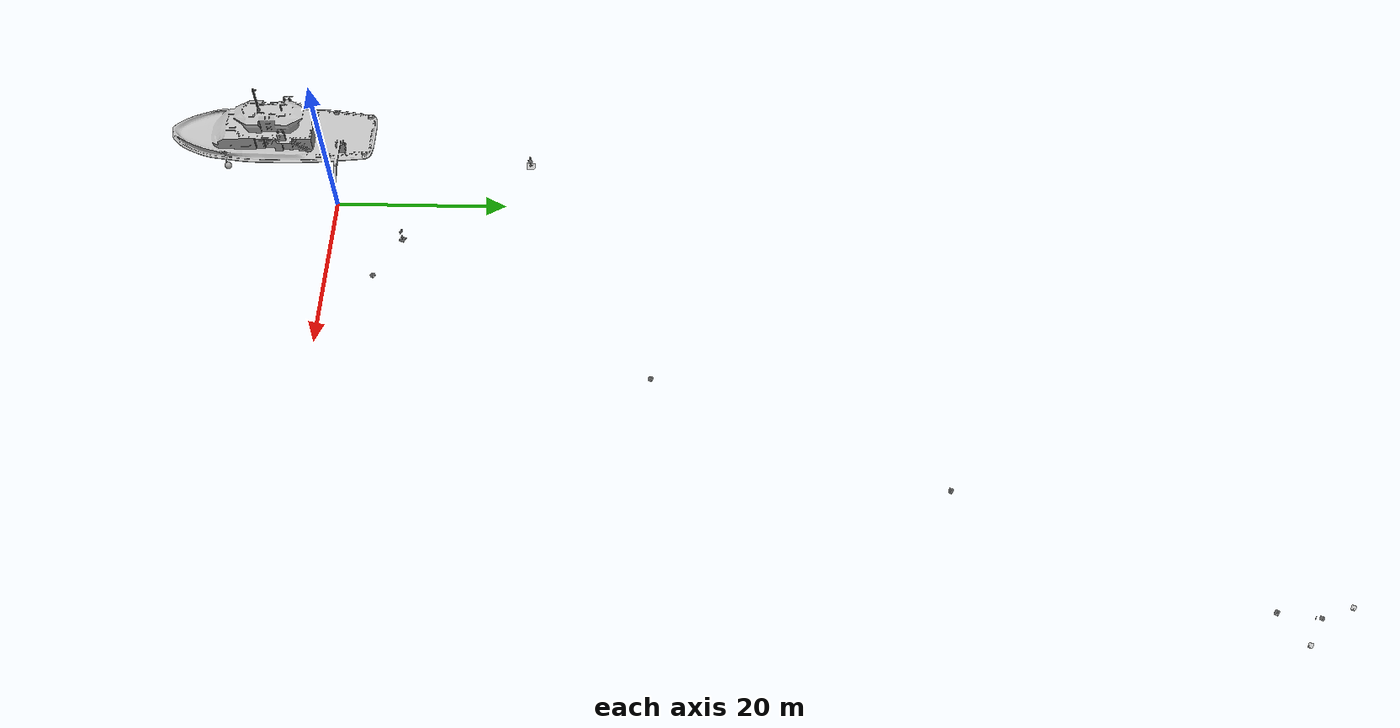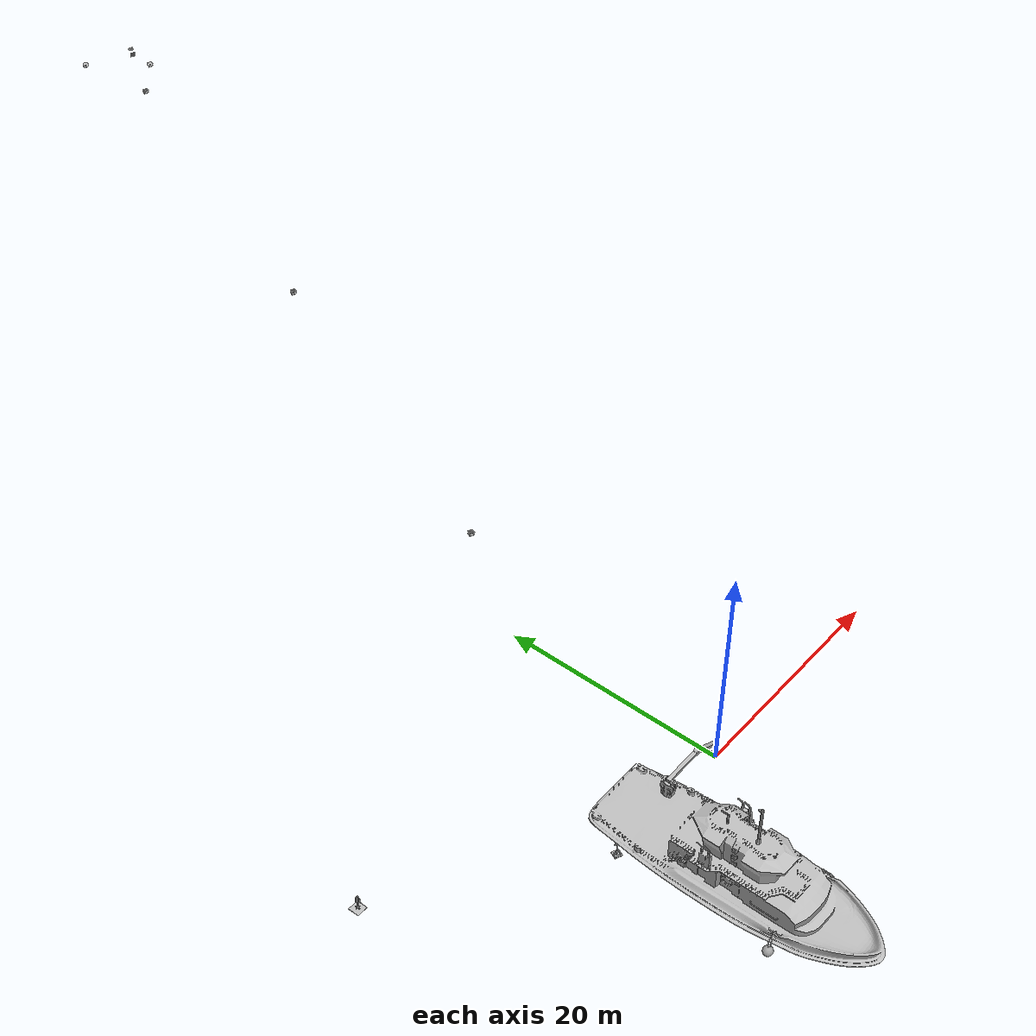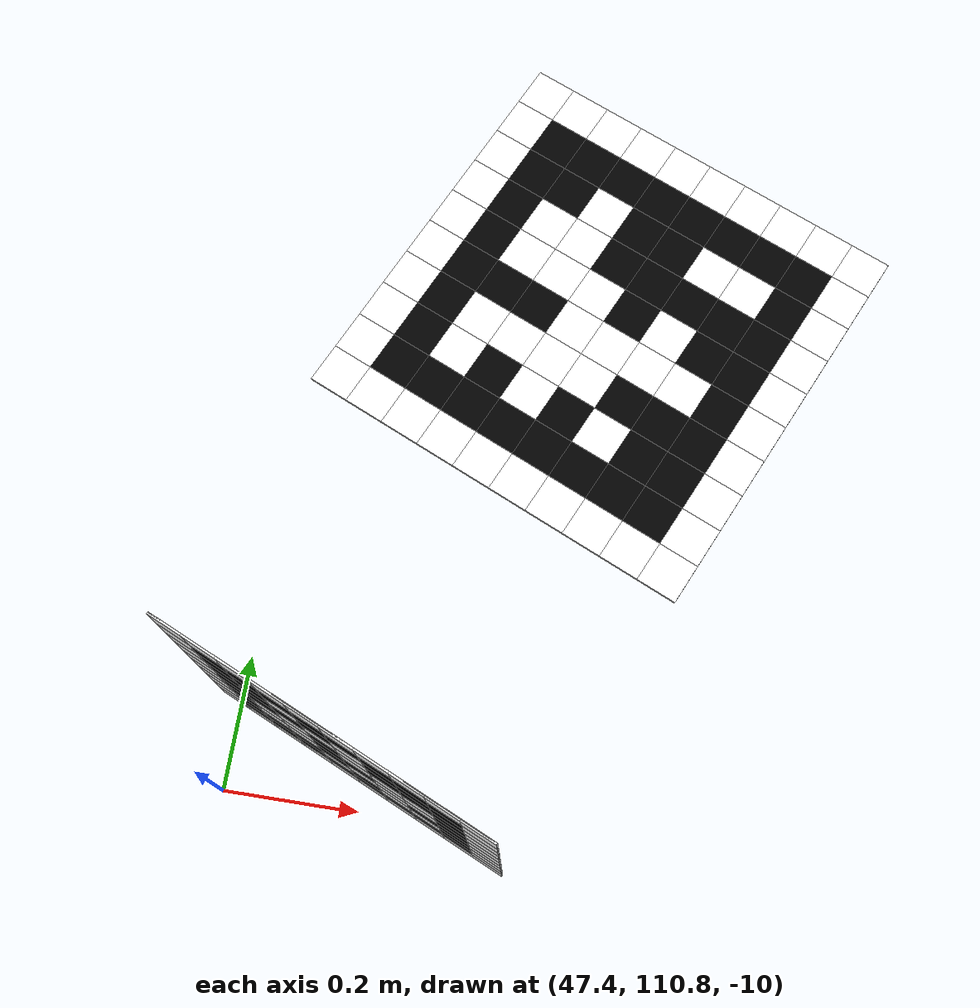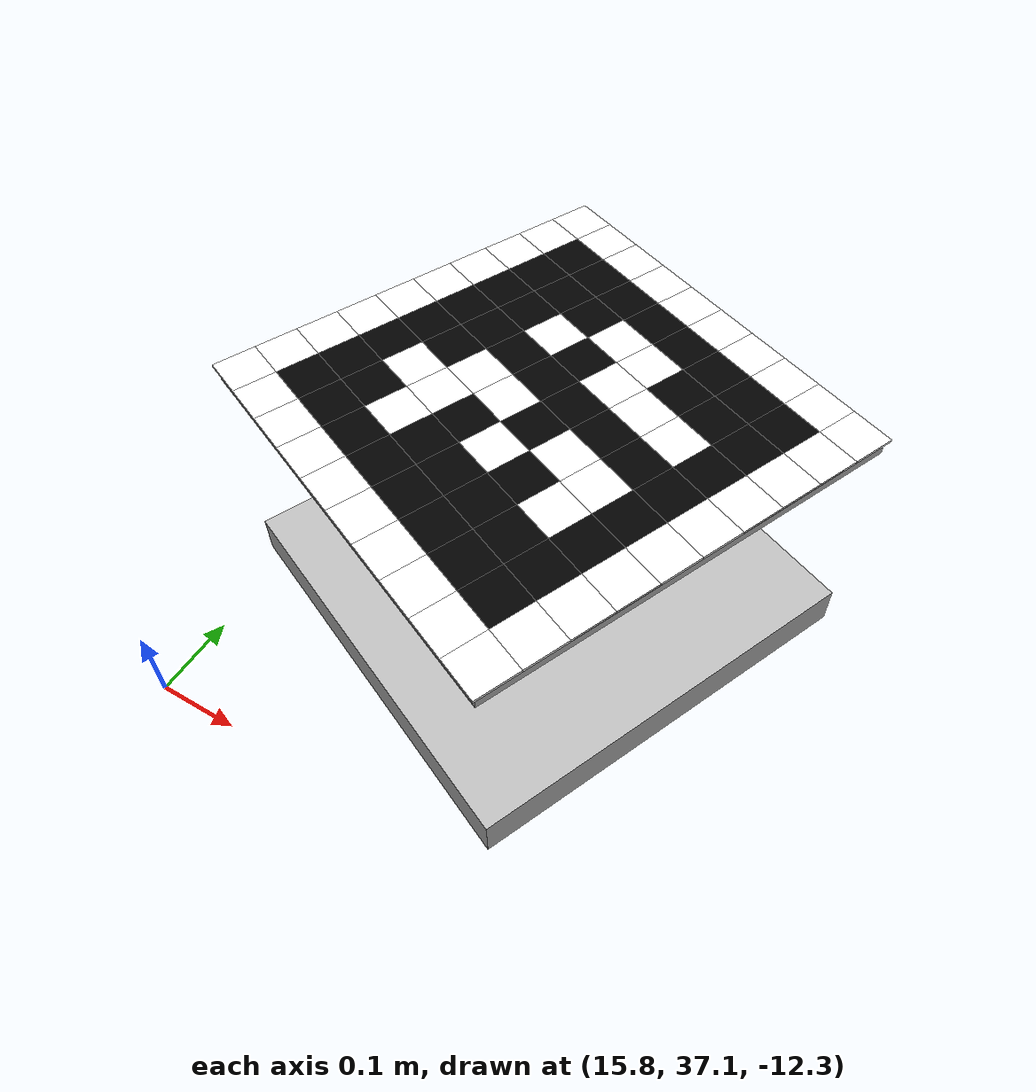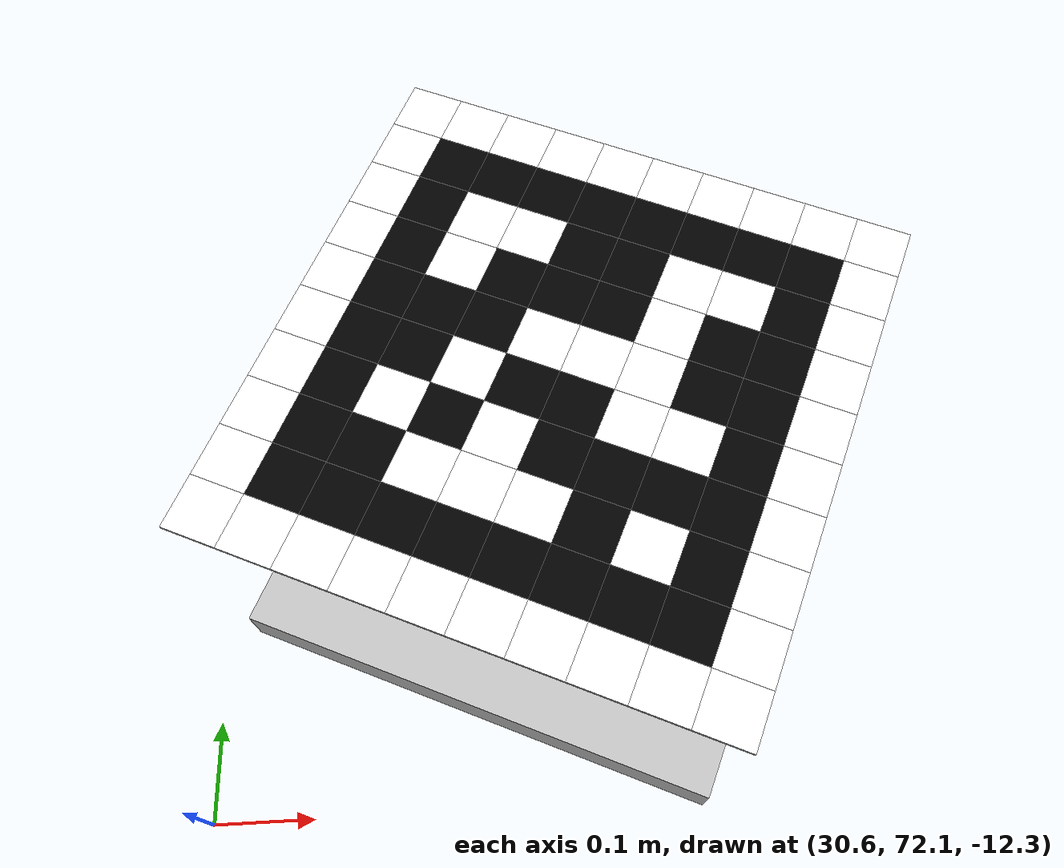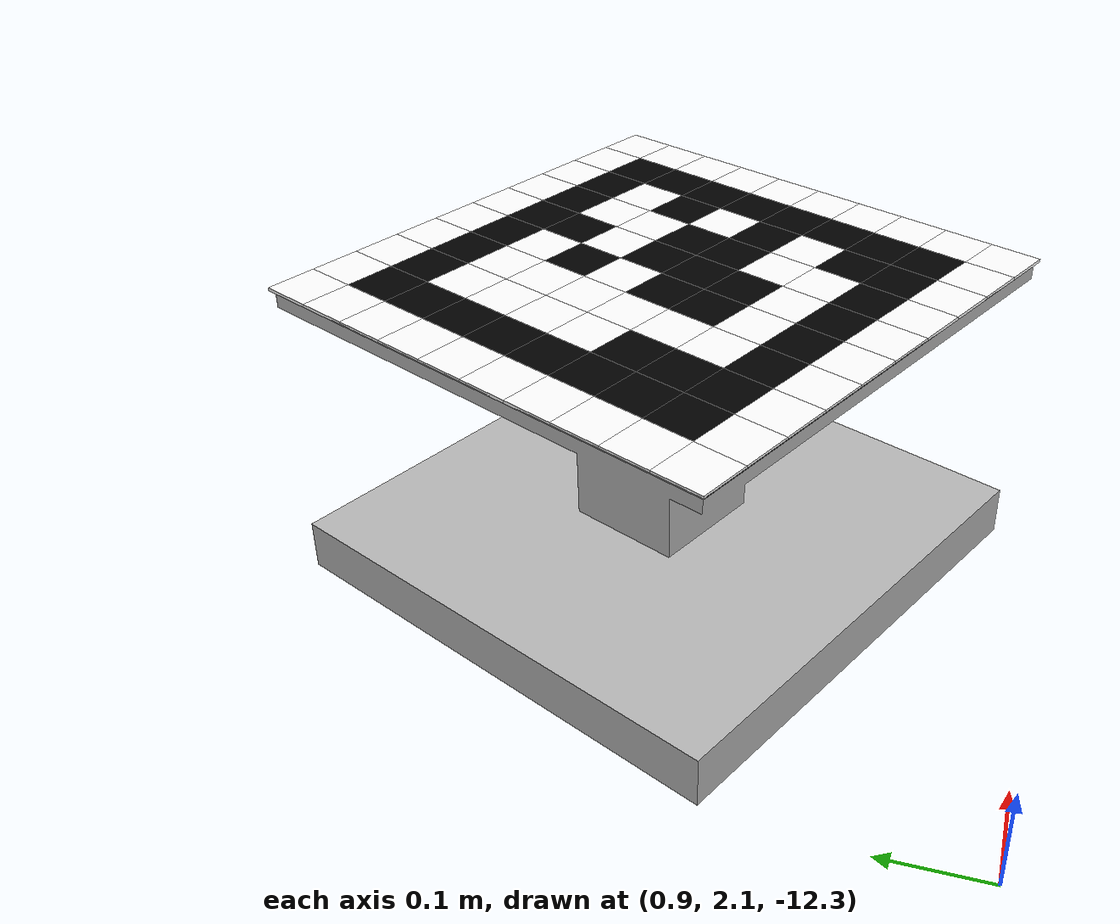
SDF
<sdf version="1.6">
 <world name="ssiv_bahia">
  <physics type="ode">
   <max_step_size>0.01</max_step_size>
   <real_time_factor>1</real_time_factor>
   <real_time_update_rate>100</real_time_update_rate>
  </physics>
  <spherical_coordinates>
   <latitude_deg>-12.9364</latitude_deg>
   <longitude_deg>-38.5127</longitude_deg>
   <heading_deg>90</heading_deg>
  </spherical_coordinates>
  <model name="nwu">
   <static>true</static>
   <link name="base"/>
   <link name="orientation"/>
   <joint name="__joint_orientation" type="fixed"><child>orientation</child><parent>base</parent></joint>
  </model>
  <model name="surface"><static>true</static></model>
  <model name="usbl"><static>true</static></model>
  <model name="beginning_of_pipe"><static>true</static><pose>0.66 2.68 -12.3 0 0 1.15</pose></model>
  <include><uri>model://vessel</uri><pose>-9 -8 0 0 0 3.14</pose></include>
  <include>
   <uri>model://apriltag_support_horizontal</uri>
   <name>apriltag_11_support</name>
   <pose>1.24 2.47 -12.3 0 0 1.15</pose>
  </include>
  <include>
   <uri>model://apriltag_support_horizontal</uri>
   <name>apriltag_12_support</name>
   <pose>16.10 37.45 -12.3 0 0 1.15</pose>
  </include>
  <include>
   <uri>model://apriltag_support_horizontal</uri>
   <name>apriltag_14_support</name>
   <pose>30.96 72.42 -12.3 0 0 1.15</pose>
  </include>
  <include>
   <uri>model://apriltag_support_horizontal</uri>
   <name>apriltag_16_support</name>
   <pose>45.83 107.40 -12.3 0 0 1.15</pose>
  </include>
  <include>
   <uri>model://apriltag_support_horizontal</uri>
   <name>apriltag_17_support</name>
   <pose>49.74 110.51 -12.3 0 0 1.15</pose>
  </include>
  <include>
   <uri>model://apriltag_support_horizontal</uri>
   <name>apriltag_7_support</name>
   <pose>45.08 115.92 -12.3 0 0 1.15</pose>
  </include>
  <include><uri>model://apriltag_11</uri><pose>1.24 2.47 -11.99 0 0 1.15</pose></include>
  <include><uri>model://apriltag_12</uri><pose>16.10 37.45 -11.99 0 0 1.15</pose></include>
  <include><uri>model://apriltag_14</uri><pose>30.96 72.42 -11.99 0 0 1.15</pose></include>
  <include><uri>model://apriltag_16</uri><pose>45.83 107.40 -11.99 0 0 1.15</pose></include>
  <include>
   <uri>model://apriltag_support</uri>
   <name>apriltag_5_support</name>
   <pose>-4.56 5.47 -12.3 0 0 2.72</pose>
  </include>
  <include>
   <uri>model://apriltag_1</uri>
   <name>apriltag_1</name>
   <pose>47.85 111.36 -9.44 0 0 1.15</pose>
  </include>
  <include><uri>model://apriltag_10</uri><pose>47.59 110.85 -9.8 1.57 1.57 -0.42</pose></include>
  <include><uri>model://datinho</uri><pose>-20.05 20 -16 0 0 -1.57</pose></include>
  <plugin name="underwater" filename="libgazebo_underwater.so">
   <model_name>flat_fish</model_name>
   <link_name>flat_fish_body</link_name>
   <drag_coefficient>5 7.5 12.5</drag_coefficient>
   <center_of_buoyancy>0 0 0.1</center_of_buoyancy>
   <fluid_velocity>0.2 0.2 0</fluid_velocity>
   <buoyancy>24</buoyancy>
  </plugin>
 </world>
</sdf>

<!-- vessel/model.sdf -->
<sdf version="1.4">
    <model name="vessel">
        <pose>0 0 0 0 0 0</pose>
        <static>true</static>
        <link name="vessel_body">
            <visual name="visual">
                <geometry>
                    <mesh>
                        <uri>model://vessel/visual.osgb</uri>
                    </mesh>
                </geometry>
            </visual>
            <collision name="collision">
                <geometry>
                    <mesh>
                        <uri>model://vessel/collision.stl</uri>
                    </mesh>
                </geometry>
            </collision>
            <inertial>
                <pose>0 0 -1 0 0 0</pose>
                <inertia>
                    <ixx>0.0</ixx>
                    <ixy>0</ixy>
                    <ixz>0.0</ixz>
                    <iyy>0.0</iyy>
                    <iyz>0</iyz>
                    <izz>0.0</izz>
                </inertia>
                <mass>1.0</mass>
            </inertial>
        </link>
    </model>
</sdf>

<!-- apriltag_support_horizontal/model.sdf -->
<sdf version="1.4">
    <model name="apriltag_support_horizontal">
        <pose>0 0 0 0 0 0</pose>
        <static>true</static>
        <link name="apriltag_support_horizontal_body">
            <visual name="visual">
                <geometry>
                    <mesh>
                        <uri>model://apriltag_support_horizontal/visual.osgb</uri>
                    </mesh>
                </geometry>
            </visual>
            <collision name="collision">
                <geometry>
                    <mesh>
                        <uri>model://apriltag_support_horizontal/collision.stl</uri>
                    </mesh>
                </geometry>
            </collision>
            <inertial>
                <pose>0 0 -1 0 0 0</pose>
                <inertia>
                    <ixx>0.0</ixx>
                    <ixy>0</ixy>
                    <ixz>0.0</ixz>
                    <iyy>0.0</iyy>
                    <iyz>0</iyz>
                    <izz>0.0</izz>
                </inertia>
                <mass>1.0</mass>
            </inertial>
        </link>
    </model>
</sdf>

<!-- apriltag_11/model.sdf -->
<sdf version="1.4">
  <model name='apriltag_11'>
  <static>true</static>
  <pose>0 0 0 0 0 0</pose>
     <link name='apriltag_body'>
      <visual name='block0'>
        <pose>-0.225 -0.225 0.001 0 0 0</pose>
          <geometry>
            <box>
            <size>0.05 0.05 0.003</size>
            </box>
          </geometry>
        <material>
          <ambient>1 1 1 1</ambient>
          <diffuse>1 1 1 1</diffuse>
          <specular>1 1 1 1</specular>
        </material>
      </visual>
      <visual name='block1'>
        <pose>-0.225 -0.175 0.001 0 0 0</pose>
          <geometry>
            <box>
            <size>0.05 0.05 0.003</size>
            </box>
          </geometry>
        <material>
          <ambient>1 1 1 1</ambient>
          <diffuse>1 1 1 1</diffuse>
          <specular>1 1 1 1</specular>
        </material>
      </visual>
      <visual name='block2'>
        <pose>-0.225 -0.125 0.001 0 0 0</pose>
          <geometry>
            <box>
            <size>0.05 0.05 0.003</size>
            </box>
          </geometry>
        <material>
          <ambient>1 1 1 1</ambient>
          <diffuse>1 1 1 1</diffuse>
          <specular>1 1 1 1</specular>
        </material>
      </visual>
      <visual name='block3'>
        <pose>-0.225 -0.075 0.001 0 0 0</pose>
          <geometry>
            <box>
            <size>0.05 0.05 0.003</size>
            </box>
          </geometry>
        <material>
          <ambient>1 1 1 1</ambient>
          <diffuse>1 1 1 1</diffuse>
          <specular>1 1 1 1</specular>
        </material>
      </visual>
      <visual name='block4'>
        <pose>-0.225 -0.025 0.001 0 0 0</pose>
          <geometry>
            <box>
            <size>0.05 0.05 0.003</size>
            </box>
          </geometry>
        <material>
          <ambient>1 1 1 1</ambient>
          <diffuse>1 1 1 1</diffuse>
          <specular>1 1 1 1</specular>
        </material>
      </visual>
      <visual name='block5'>
        <pose>-0.225 0.025 0.001 0 0 0</pose>
          <geometry>
            <box>
            <size>0.05 0.05 0.003</size>
            </box>
          </geometry>
        <material>
          <ambient>1 1 1 1</ambient>
          <diffuse>1 1 1 1</diffuse>
          <specular>1 1 1 1</specular>
        </material>
      </visual>
      <visual name='block6'>
        <pose>-0.225 0.075 0.001 0 0 0</pose>
          <geometry>
            <box>
            <size>0.05 0.05 0.003</size>
            </box>
          </geometry>
        <material>
          <ambient>1 1 1 1</ambient>
          <diffuse>1 1 1 1</diffuse>
          <specular>1 1 1 1</specular>
        </material>
      </visual>
      <visual name='block7'>
        <pose>-0.225 0.125 0.001 0 0 0</pose>
          <geometry>
            <box>
            <size>0.05 0.05 0.003</size>
            </box>
          </geometry>
        <material>
          <ambient>1 1 1 1</ambient>
          <diffuse>1 1 1 1</diffuse>
          <specular>1 1 1 1</specular>
        </material>
      </visual>
      <visual name='block8'>
        <pose>-0.225 0.175 0.001 0 0 0</pose>
          <geometry>
            <box>
            <size>0.05 0.05 0.003</size>
            </box>
          </geometry>
        <material>
          <ambient>1 1 1 1</ambient>
          <diffuse>1 1 1 1</diffuse>
          <specular>1 1 1 1</specular>
        </material>
      </visual>
      <visual name='block9'>
        <pose>-0.225 0.225 0.001 0 0 0</pose>
          <geometry>
            <box>
            <size>0.05 0.05 0.003</size>
            </box>
          </geometry>
        <material>
          <ambient>1 1 1 1</ambient>
          <diffuse>1 1 1 1</diffuse>
          <specular>1 1 1 1</specular>
        </material>
      </visual>
      <visual name='block10'>
        <pose>-0.175 -0.225 0.001 0 0 0</pose>
          <geometry>
            <box>
            <size>0.05 0.05 0.003</size>
            </box>
          </geometry>
        <material>
          <ambient>1 1 1 1</ambient>
          <diffuse>1 1 1 1</diffuse>
          <specular>1 1 1 1</specular>
        </material>
      </visual>
      <visual name='block11'>
        <pose>-0.175 -0.175 0.001 0 0 0</pose>
          <geometry>
            <box>
            <size>0.05 0.05 0.003</size>
            </box>
          </geometry>
        <material>
          <ambient>0 0 0 1</ambient>
          <diffuse>0 0 0 1</diffuse>
          <specular>0 0 0 1</specular>
        </material>
      </visual>
      <visual name='block12'>
        <pose>-0.175 -0.125 0.001 0 0 0</pose>
          <geometry>
            <box>
            <size>0.05 0.05 0.003</size>
            </box>
          </geometry>
        <material>
          <ambient>0 0 0 1</ambient>
          <diffuse>0 0 0 1</diffuse>
          <specular>0 0 0 1</specular>
        </material>
      </visual>
      <visual name='block13'>
        <pose>-0.175 -0.075 0.001 0 0 0</pose>
          <geometry>
            <box>
            <size>0.05 0.05 0.003</size>
            </box>
          </geometry>
        <material>
          <ambient>0 0 0 1</ambient>
          <diffuse>0 0 0 1</diffuse>
          <specular>0 0 0 1</specular>
        </material>
      </visual>
      <visual name='block14'>
        <pose>-0.175 -0.025 0.001 0 0 0</pose>
          <geometry>
            <box>
            <size>0.05 0.05 0.003</size>
            </box>
          </geometry>
        <material>
          <ambient>0 0 0 1</ambient>
          <diffuse>0 0 0 1</diffuse>
          <specular>0 0 0 1</specular>
        </material>
      </visual>
      <visual name='block15'>
        <pose>-0.175 0.025 0.001 0 0 0</pose>
          <geometry>
            <box>
            <size>0.05 0.05 0.003</size>
            </box>
          </geometry>
        <material>
          <ambient>0 0 0 1</ambient>
          <diffuse>0 0 0 1</diffuse>
          <specular>0 0 0 1</specular>
        </material>
      </visual>
      <visual name='block16'>
        <pose>-0.175 0.075 0.001 0 0 0</pose>
          <geometry>
            <box>
            <size>0.05 0.05 0.003</size>
            </box>
          </geometry>
        <material>
          <ambient>0 0 0 1</ambient>
          <diffuse>0 0 0 1</diffuse>
          <specular>0 0 0 1</specular>
        </material>
      </visual>
      <visual name='block17'>
        <pose>-0.175 0.125 0.001 0 0 0</pose>
          <geometry>
            <box>
            <size>0.05 0.05 0.003</size>
            </box>
          </geometry>
        <material>
          <ambient>0 0 0 1</ambient>
          <diffuse>0 0 0 1</diffuse>
          <specular>0 0 0 1</specular>
        </material>
      </visual>
      <visual name='block18'>
        <pose>-0.175 0.175 0.001 0 0 0</pose>
          <geometry>
            <box>
            <size>0.05 0.05 0.003</size>
            </box>
          </geometry>
        <material>
          <ambient>0 0 0 1</ambient>
          <diffuse>0 0 0 1</diffuse>
          <specular>0 0 0 1</specular>
        </material>
      </visual>
      <visual name='block19'>
        <pose>-0.175 0.225 0.001 0 0 0</pose>
          <geometry>
            <box>
            <size>0.05 0.05 0.003</size>
            </box>
          </geometry>
        <material>
          <ambient>1 1 1 1</ambient>
          <diffuse>1 1 1 1</diffuse>
          <specular>1 1 1 1</specular>
        </material>
      </visual>
      <visual name='block20'>
        <pose>-0.125 -0.225 0.001 0 0 0</pose>
          <geometry>
            <box>
            <size>0.05 0.05 0.003</size>
            </box>
          </geometry>
        <material>
          <ambient>1 1 1 1</ambient>
          <diffuse>1 1 1 1</diffuse>
          <specular>1 1 1 1</specular>
        </material>
      </visual>
      <visual name='block21'>
        <pose>-0.125 -0.175 0.001 0 0 0</pose>
          <geometry>
            <box>
            <size>0.05 0.05 0.003</size>
            </box>
          </geometry>
        <material>
          <ambient>0 0 0 1</ambient>
          <diffuse>0 0 0 1</diffuse>
          <specular>0 0 0 1</specular>
        </material>
      </visual>
      <visual name='block22'>
        <pose>-0.125 -0.125 0.001 0 0 0</pose>
          <geometry>
            <box>
            <size>0.05 0.05 0.003</size>
            </box>
          </geometry>
        <material>
          <ambient>0 0 0 1</ambient>
          <diffuse>0 0 0 1</diffuse>
          <specular>0 0 0 1</specular>
        </material>
      </visual>
      <visual name='block23'>
        <pose>-0.125 -0.075 0.001 0 0 0</pose>
          <geometry>
            <box>
            <size>0.05 0.05 0.003</size>
            </box>
          </geometry>
        <material>
          <ambient>1 1 1 1</ambient>
          <diffuse>1 1 1 1</diffuse>
          <specular>1 1 1 1</specular>
        </material>
      </visual>
      <visual name='block24'>
        <pose>-0.125 -0.025 0.001 0 0 0</pose>
          <geometry>
            <box>
            <size>0.05 0.05 0.003</size>
            </box>
          </geometry>
        <material>
          <ambient>1 1 1 1</ambient>
          <diffuse>1 1 1 1</diffuse>
          <specular>1 1 1 1</specular>
        </material>
      </visual>
      <visual name='block25'>
        <pose>-0.125 0.025 0.001 0 0 0</pose>
          <geometry>
            <box>
            <size>0.05 0.05 0.003</size>
            </box>
          </geometry>
        <material>
          <ambient>1 1 1 1</ambient>
          <diffuse>1 1 1 1</diffuse>
          <specular>1 1 1 1</specular>
        </material>
      </visual>
      <visual name='block26'>
        <pose>-0.125 0.075 0.001 0 0 0</pose>
          <geometry>
            <box>
            <size>0.05 0.05 0.003</size>
            </box>
          </geometry>
        <material>
          <ambient>1 1 1 1</ambient>
          <diffuse>1 1 1 1</diffuse>
          <specular>1 1 1 1</specular>
        </material>
      </visual>
      <visual name='block27'>
        <pose>-0.125 0.125 0.001 0 0 0</pose>
          <geometry>
            <box>
            <size>0.05 0.05 0.003</size>
            </box>
          </geometry>
        <material>
          <ambient>0 0 0 1</ambient>
          <diffuse>0 0 0 1</diffuse>
          <specular>0 0 0 1</specular>
        </material>
      </visual>
      <visual name='block28'>
        <pose>-0.125 0.175 0.001 0 0 0</pose>
          <geometry>
            <box>
            <size>0.05 0.05 0.003</size>
            </box>
          </geometry>
        <material>
          <ambient>0 0 0 1</ambient>
          <diffuse>0 0 0 1</diffuse>
          <specular>0 0 0 1</specular>
        </material>
      </visual>
      <visual name='block29'>
        <pose>-0.125 0.225 0.001 0 0 0</pose>
          <geometry>
            <box>
            <size>0.05 0.05 0.003</size>
            </box>
          </geometry>
        <material>
          <ambient>1 1 1 1</ambient>
          <diffuse>1 1 1 1</diffuse>
          <specular>1 1 1 1</specular>
        </material>
      </visual>
      <visual name='block30'>
        <pose>-0.075 -0.225 0.001 0 0 0</pose>
          <geometry>
            <box>
            <size>0.05 0.05 0.003</size>
            </box>
          </geometry>
        <material>
          <ambient>1 1 1 1</ambient>
          <diffuse>1 1 1 1</diffuse>
          <specular>1 1 1 1</specular>
        </material>
      </visual>
      <visual name='block31'>
        <pose>-0.075 -0.175 0.001 0 0 0</pose>
          <geometry>
            <box>
            <size>0.05 0.05 0.003</size>
            </box>
          </geometry>
        <material>
          <ambient>0 0 0 1</ambient>
          <diffuse>0 0 0 1</diffuse>
          <specular>0 0 0 1</specular>
        </material>
      </visual>
      <visual name='block32'>
        <pose>-0.075 -0.125 0.001 0 0 0</pose>
          <geometry>
            <box>
            <size>0.05 0.05 0.003</size>
            </box>
          </geometry>
        <material>
          <ambient>1 1 1 1</ambient>
          <diffuse>1 1 1 1</diffuse>
          <specular>1 1 1 1</specular>
        </material>
      </visual>
      <visual name='block33'>
        <pose>-0.075 -0.075 0.001 0 0 0</pose>
          <geometry>
            <box>
            <size>0.05 0.05 0.003</size>
            </box>
          </geometry>
        <material>
          <ambient>1 1 1 1</ambient>
          <diffuse>1 1 1 1</diffuse>
          <specular>1 1 1 1</specular>
        </material>
      </visual>
      <visual name='block34'>
        <pose>-0.075 -0.025 0.001 0 0 0</pose>
          <geometry>
            <box>
            <size>0.05 0.05 0.003</size>
            </box>
          </geometry>
        <material>
          <ambient>0 0 0 1</ambient>
          <diffuse>0 0 0 1</diffuse>
          <specular>0 0 0 1</specular>
        </material>
      </visual>
      <visual name='block35'>
        <pose>-0.075 0.025 0.001 0 0 0</pose>
          <geometry>
            <box>
            <size>0.05 0.05 0.003</size>
            </box>
          </geometry>
        <material>
          <ambient>0 0 0 1</ambient>
          <diffuse>0 0 0 1</diffuse>
          <specular>0 0 0 1</specular>
        </material>
      </visual>
      <visual name='block36'>
        <pose>-0.075 0.075 0.001 0 0 0</pose>
          <geometry>
            <box>
            <size>0.05 0.05 0.003</size>
            </box>
          </geometry>
        <material>
          <ambient>1 1 1 1</ambient>
          <diffuse>1 1 1 1</diffuse>
          <specular>1 1 1 1</specular>
        </material>
      </visual>
      <visual name='block37'>
        <pose>-0.075 0.125 0.001 0 0 0</pose>
          <geometry>
            <box>
            <size>0.05 0.05 0.003</size>
            </box>
          </geometry>
        <material>
          <ambient>0 0 0 1</ambient>
          <diffuse>0 0 0 1</diffuse>
          <specular>0 0 0 1</specular>
        </material>
      </visual>
      <visual name='block38'>
        <pose>-0.075 0.175 0.001 0 0 0</pose>
          <geometry>
            <box>
            <size>0.05 0.05 0.003</size>
            </box>
          </geometry>
        <material>
          <ambient>0 0 0 1</ambient>
          <diffuse>0 0 0 1</diffuse>
          <specular>0 0 0 1</specular>
        </material>
      </visual>
      <visual name='block39'>
        <pose>-0.075 0.225 0.001 0 0 0</pose>
          <geometry>
            <box>
            <size>0.05 0.05 0.003</size>
            </box>
          </geometry>
        <material>
          <ambient>1 1 1 1</ambient>
          <diffuse>1 1 1 1</diffuse>
          <specular>1 1 1 1</specular>
        </material>
      </visual>
      <visual name='block40'>
        <pose>-0.025 -0.225 0.001 0 0 0</pose>
          <geometry>
            <box>
            <size>0.05 0.05 0.003</size>
            </box>
          </geometry>
        <material>
          <ambient>1 1 1 1</ambient>
          <diffuse>1 1 1 1</diffuse>
          <specular>1 1 1 1</specular>
        </material>
      </visual>
      <visual name='block41'>
        <pose>-0.025 -0.175 0.001 0 0 0</pose>
          <geometry>
            <box>
            <size>0.05 0.05 0.003</size>
            </box>
          </geometry>
        <material>
          <ambient>0 0 0 1</ambient>
          <diffuse>0 0 0 1</diffuse>
          <specular>0 0 0 1</specular>
        </material>
      </visual>
      <visual name='block42'>
        <pose>-0.025 -0.125 0.001 0 0 0</pose>
          <geometry>
            <box>
            <size>0.05 0.05 0.003</size>
            </box>
          </geometry>
        <material>
          <ambient>0 0 0 1</ambient>
          <diffuse>0 0 0 1</diffuse>
          <specular>0 0 0 1</specular>
        </material>
      </visual>
      <visual name='block43'>
        <pose>-0.025 -0.075 0.001 0 0 0</pose>
          <geometry>
            <box>
            <size>0.05 0.05 0.003</size>
            </box>
          </geometry>
        <material>
          <ambient>0 0 0 1</ambient>
          <diffuse>0 0 0 1</diffuse>
          <specular>0 0 0 1</specular>
        </material>
      </visual>
      <visual name='block44'>
        <pose>-0.025 -0.025 0.001 0 0 0</pose>
          <geometry>
            <box>
            <size>0.05 0.05 0.003</size>
            </box>
          </geometry>
        <material>
          <ambient>0 0 0 1</ambient>
          <diffuse>0 0 0 1</diffuse>
          <specular>0 0 0 1</specular>
        </material>
      </visual>
      <visual name='block45'>
        <pose>-0.025 0.025 0.001 0 0 0</pose>
          <geometry>
            <box>
            <size>0.05 0.05 0.003</size>
            </box>
          </geometry>
        <material>
          <ambient>0 0 0 1</ambient>
          <diffuse>0 0 0 1</diffuse>
          <specular>0 0 0 1</specular>
        </material>
      </visual>
      <visual name='block46'>
        <pose>-0.025 0.075 0.001 0 0 0</pose>
          <geometry>
            <box>
            <size>0.05 0.05 0.003</size>
            </box>
          </geometry>
        <material>
          <ambient>1 1 1 1</ambient>
          <diffuse>1 1 1 1</diffuse>
          <specular>1 1 1 1</specular>
        </material>
      </visual>
      <visual name='block47'>
        <pose>-0.025 0.125 0.001 0 0 0</pose>
          <geometry>
            <box>
            <size>0.05 0.05 0.003</size>
            </box>
          </geometry>
        <material>
          <ambient>1 1 1 1</ambient>
          <diffuse>1 1 1 1</diffuse>
          <specular>1 1 1 1</specular>
        </material>
      </visual>
      <visual name='block48'>
        <pose>-0.025 0.175 0.001 0 0 0</pose>
          <geometry>
            <box>
            <size>0.05 0.05 0.003</size>
            </box>
          </geometry>
        <material>
          <ambient>0 0 0 1</ambient>
          <diffuse>0 0 0 1</diffuse>
          <specular>0 0 0 1</specular>
        </material>
      </visual>
      <visual name='block49'>
        <pose>-0.025 0.225 0.001 0 0 0</pose>
          <geometry>
            <box>
            <size>0.05 0.05 0.003</size>
            </box>
          </geometry>
        <material>
          <ambient>1 1 1 1</ambient>
          <diffuse>1 1 1 1</diffuse>
          <specular>1 1 1 1</specular>
        </material>
      </visual>
      <visual name='block50'>
        <pose>0.025 -0.225 0.001 0 0 0</pose>
          <geometry>
            <box>
            <size>0.05 0.05 0.003</size>
            </box>
          </geometry>
        <material>
          <ambient>1 1 1 1</ambient>
          <diffuse>1 1 1 1</diffuse>
          <specular>1 1 1 1</specular>
        </material>
      </visual>
      <visual name='block51'>
        <pose>0.025 -0.175 0.001 0 0 0</pose>
          <geometry>
            <box>
            <size>0.05 0.05 0.003</size>
            </box>
          </geometry>
        <material>
          <ambient>0 0 0 1</ambient>
          <diffuse>0 0 0 1</diffuse>
          <specular>0 0 0 1</specular>
        </material>
      </visual>
      <visual name='block52'>
        <pose>0.025 -0.125 0.001 0 0 0</pose>
          <geometry>
            <box>
            <size>0.05 0.05 0.003</size>
            </box>
          </geometry>
        <material>
          <ambient>1 1 1 1</ambient>
          <diffuse>1 1 1 1</diffuse>
          <specular>1 1 1 1</specular>
        </material>
      </visual>
      <visual name='block53'>
        <pose>0.025 -0.075 0.001 0 0 0</pose>
          <geometry>
            <box>
            <size>0.05 0.05 0.003</size>
            </box>
          </geometry>
        <material>
          <ambient>0 0 0 1</ambient>
          <diffuse>0 0 0 1</diffuse>
          <specular>0 0 0 1</specular>
        </material>
      </visual>
      <visual name='block54'>
        <pose>0.025 -0.025 0.001 0 0 0</pose>
          <geometry>
            <box>
            <size>0.05 0.05 0.003</size>
            </box>
          </geometry>
        <material>
          <ambient>0 0 0 1</ambient>
          <diffuse>0 0 0 1</diffuse>
          <specular>0 0 0 1</specular>
        </material>
      </visual>
      <visual name='block55'>
        <pose>0.025 0.025 0.001 0 0 0</pose>
          <geometry>
            <box>
            <size>0.05 0.05 0.003</size>
            </box>
          </geometry>
        <material>
          <ambient>1 1 1 1</ambient>
          <diffuse>1 1 1 1</diffuse>
          <specular>1 1 1 1</specular>
        </material>
      </visual>
      <visual name='block56'>
        <pose>0.025 0.075 0.001 0 0 0</pose>
          <geometry>
            <box>
            <size>0.05 0.05 0.003</size>
            </box>
          </geometry>
        <material>
          <ambient>1 1 1 1</ambient>
          <diffuse>1 1 1 1</diffuse>
          <specular>1 1 1 1</specular>
        </material>
      </visual>
      <visual name='block57'>
        <pose>0.025 0.125 0.001 0 0 0</pose>
          <geometry>
            <box>
            <size>0.05 0.05 0.003</size>
            </box>
          </geometry>
        <material>
          <ambient>1 1 1 1</ambient>
          <diffuse>1 1 1 1</diffuse>
          <specular>1 1 1 1</specular>
        </material>
      </visual>
      <visual name='block58'>
        <pose>0.025 0.175 0.001 0 0 0</pose>
          <geometry>
            <box>
            <size>0.05 0.05 0.003</size>
            </box>
          </geometry>
        <material>
          <ambient>0 0 0 1</ambient>
          <diffuse>0 0 0 1</diffuse>
          <specular>0 0 0 1</specular>
        </material>
      </visual>
      <visual name='block59'>
        <pose>0.025 0.225 0.001 0 0 0</pose>
          <geometry>
            <box>
            <size>0.05 0.05 0.003</size>
            </box>
          </geometry>
        <material>
          <ambient>1 1 1 1</ambient>
          <diffuse>1 1 1 1</diffuse>
          <specular>1 1 1 1</specular>
        </material>
      </visual>
      <visual name='block60'>
        <pose>0.075 -0.225 0.001 0 0 0</pose>
          <geometry>
            <box>
            <size>0.05 0.05 0.003</size>
            </box>
          </geometry>
        <material>
          <ambient>1 1 1 1</ambient>
          <diffuse>1 1 1 1</diffuse>
          <specular>1 1 1 1</specular>
        </material>
      </visual>
      <visual name='block61'>
        <pose>0.075 -0.175 0.001 0 0 0</pose>
          <geometry>
            <box>
            <size>0.05 0.05 0.003</size>
            </box>
          </geometry>
        <material>
          <ambient>0 0 0 1</ambient>
          <diffuse>0 0 0 1</diffuse>
          <specular>0 0 0 1</specular>
        </material>
      </visual>
      <visual name='block62'>
        <pose>0.075 -0.125 0.001 0 0 0</pose>
          <geometry>
            <box>
            <size>0.05 0.05 0.003</size>
            </box>
          </geometry>
        <material>
          <ambient>0 0 0 1</ambient>
          <diffuse>0 0 0 1</diffuse>
          <specular>0 0 0 1</specular>
        </material>
      </visual>
      <visual name='block63'>
        <pose>0.075 -0.075 0.001 0 0 0</pose>
          <geometry>
            <box>
            <size>0.05 0.05 0.003</size>
            </box>
          </geometry>
        <material>
          <ambient>1 1 1 1</ambient>
          <diffuse>1 1 1 1</diffuse>
          <specular>1 1 1 1</specular>
        </material>
      </visual>
      <visual name='block64'>
        <pose>0.075 -0.025 0.001 0 0 0</pose>
          <geometry>
            <box>
            <size>0.05 0.05 0.003</size>
            </box>
          </geometry>
        <material>
          <ambient>1 1 1 1</ambient>
          <diffuse>1 1 1 1</diffuse>
          <specular>1 1 1 1</specular>
        </material>
      </visual>
      <visual name='block65'>
        <pose>0.075 0.025 0.001 0 0 0</pose>
          <geometry>
            <box>
            <size>0.05 0.05 0.003</size>
            </box>
          </geometry>
        <material>
          <ambient>0 0 0 1</ambient>
          <diffuse>0 0 0 1</diffuse>
          <specular>0 0 0 1</specular>
        </material>
      </visual>
      <visual name='block66'>
        <pose>0.075 0.075 0.001 0 0 0</pose>
          <geometry>
            <box>
            <size>0.05 0.05 0.003</size>
            </box>
          </geometry>
        <material>
          <ambient>1 1 1 1</ambient>
          <diffuse>1 1 1 1</diffuse>
          <specular>1 1 1 1</specular>
        </material>
      </visual>
      <visual name='block67'>
        <pose>0.075 0.125 0.001 0 0 0</pose>
          <geometry>
            <box>
            <size>0.05 0.05 0.003</size>
            </box>
          </geometry>
        <material>
          <ambient>1 1 1 1</ambient>
          <diffuse>1 1 1 1</diffuse>
          <specular>1 1 1 1</specular>
        </material>
      </visual>
      <visual name='block68'>
        <pose>0.075 0.175 0.001 0 0 0</pose>
          <geometry>
            <box>
            <size>0.05 0.05 0.003</size>
            </box>
          </geometry>
        <material>
          <ambient>0 0 0 1</ambient>
          <diffuse>0 0 0 1</diffuse>
          <specular>0 0 0 1</specular>
        </material>
      </visual>
      <visual name='block69'>
        <pose>0.075 0.225 0.001 0 0 0</pose>
          <geometry>
            <box>
            <size>0.05 0.05 0.003</size>
            </box>
          </geometry>
        <material>
          <ambient>1 1 1 1</ambient>
          <diffuse>1 1 1 1</diffuse>
          <specular>1 1 1 1</specular>
        </material>
      </visual>
      <visual name='block70'>
        <pose>0.125 -0.225 0.001 0 0 0</pose>
          <geometry>
            <box>
            <size>0.05 0.05 0.003</size>
            </box>
          </geometry>
        <material>
          <ambient>1 1 1 1</ambient>
          <diffuse>1 1 1 1</diffuse>
          <specular>1 1 1 1</specular>
        </material>
      </visual>
      <visual name='block71'>
        <pose>0.125 -0.175 0.001 0 0 0</pose>
          <geometry>
            <box>
            <size>0.05 0.05 0.003</size>
            </box>
          </geometry>
        <material>
          <ambient>0 0 0 1</ambient>
          <diffuse>0 0 0 1</diffuse>
          <specular>0 0 0 1</specular>
        </material>
      </visual>
      <visual name='block72'>
        <pose>0.125 -0.125 0.001 0 0 0</pose>
          <geometry>
            <box>
            <size>0.05 0.05 0.003</size>
            </box>
          </geometry>
        <material>
          <ambient>1 1 1 1</ambient>
          <diffuse>1 1 1 1</diffuse>
          <specular>1 1 1 1</specular>
        </material>
      </visual>
      <visual name='block73'>
        <pose>0.125 -0.075 0.001 0 0 0</pose>
          <geometry>
            <box>
            <size>0.05 0.05 0.003</size>
            </box>
          </geometry>
        <material>
          <ambient>1 1 1 1</ambient>
          <diffuse>1 1 1 1</diffuse>
          <specular>1 1 1 1</specular>
        </material>
      </visual>
      <visual name='block74'>
        <pose>0.125 -0.025 0.001 0 0 0</pose>
          <geometry>
            <box>
            <size>0.05 0.05 0.003</size>
            </box>
          </geometry>
        <material>
          <ambient>0 0 0 1</ambient>
          <diffuse>0 0 0 1</diffuse>
          <specular>0 0 0 1</specular>
        </material>
      </visual>
      <visual name='block75'>
        <pose>0.125 0.025 0.001 0 0 0</pose>
          <geometry>
            <box>
            <size>0.05 0.05 0.003</size>
            </box>
          </geometry>
        <material>
          <ambient>1 1 1 1</ambient>
          <diffuse>1 1 1 1</diffuse>
          <specular>1 1 1 1</specular>
        </material>
      </visual>
      <visual name='block76'>
        <pose>0.125 0.075 0.001 0 0 0</pose>
          <geometry>
            <box>
            <size>0.05 0.05 0.003</size>
            </box>
          </geometry>
        <material>
          <ambient>1 1 1 1</ambient>
          <diffuse>1 1 1 1</diffuse>
          <specular>1 1 1 1</specular>
        </material>
      </visual>
      <visual name='block77'>
        <pose>0.125 0.125 0.001 0 0 0</pose>
          <geometry>
            <box>
            <size>0.05 0.05 0.003</size>
            </box>
          </geometry>
        <material>
          <ambient>1 1 1 1</ambient>
          <diffuse>1 1 1 1</diffuse>
          <specular>1 1 1 1</specular>
        </material>
      </visual>
      <visual name='block78'>
        <pose>0.125 0.175 0.001 0 0 0</pose>
          <geometry>
            <box>
            <size>0.05 0.05 0.003</size>
            </box>
          </geometry>
        <material>
          <ambient>0 0 0 1</ambient>
          <diffuse>0 0 0 1</diffuse>
          <specular>0 0 0 1</specular>
        </material>
      </visual>
      <visual name='block79'>
        <pose>0.125 0.225 0.001 0 0 0</pose>
          <geometry>
            <box>
            <size>0.05 0.05 0.003</size>
            </box>
          </geometry>
        <material>
          <ambient>1 1 1 1</ambient>
          <diffuse>1 1 1 1</diffuse>
          <specular>1 1 1 1</specular>
        </material>
      </visual>
      <visual name='block80'>
        <pose>0.175 -0.225 0.001 0 0 0</pose>
          <geometry>
            <box>
            <size>0.05 0.05 0.003</size>
            </box>
          </geometry>
        <material>
          <ambient>1 1 1 1</ambient>
          <diffuse>1 1 1 1</diffuse>
          <specular>1 1 1 1</specular>
        </material>
      </visual>
      <visual name='block81'>
        <pose>0.175 -0.175 0.001 0 0 0</pose>
          <geometry>
            <box>
            <size>0.05 0.05 0.003</size>
            </box>
          </geometry>
        <material>
          <ambient>0 0 0 1</ambient>
          <diffuse>0 0 0 1</diffuse>
          <specular>0 0 0 1</specular>
        </material>
      </visual>
      <visual name='block82'>
        <pose>0.175 -0.125 0.001 0 0 0</pose>
          <geometry>
            <box>
            <size>0.05 0.05 0.003</size>
            </box>
          </geometry>
        <material>
          <ambient>0 0 0 1</ambient>
          <diffuse>0 0 0 1</diffuse>
          <specular>0 0 0 1</specular>
        </material>
      </visual>
      <visual name='block83'>
        <pose>0.175 -0.075 0.001 0 0 0</pose>
          <geometry>
            <box>
            <size>0.05 0.05 0.003</size>
            </box>
          </geometry>
        <material>
          <ambient>0 0 0 1</ambient>
          <diffuse>0 0 0 1</diffuse>
          <specular>0 0 0 1</specular>
        </material>
      </visual>
      <visual name='block84'>
        <pose>0.175 -0.025 0.001 0 0 0</pose>
          <geometry>
            <box>
            <size>0.05 0.05 0.003</size>
            </box>
          </geometry>
        <material>
          <ambient>0 0 0 1</ambient>
          <diffuse>0 0 0 1</diffuse>
          <specular>0 0 0 1</specular>
        </material>
      </visual>
      <visual name='block85'>
        <pose>0.175 0.025 0.001 0 0 0</pose>
          <geometry>
            <box>
            <size>0.05 0.05 0.003</size>
            </box>
          </geometry>
        <material>
          <ambient>0 0 0 1</ambient>
          <diffuse>0 0 0 1</diffuse>
          <specular>0 0 0 1</specular>
        </material>
      </visual>
      <visual name='block86'>
        <pose>0.175 0.075 0.001 0 0 0</pose>
          <geometry>
            <box>
            <size>0.05 0.05 0.003</size>
            </box>
          </geometry>
        <material>
          <ambient>0 0 0 1</ambient>
          <diffuse>0 0 0 1</diffuse>
          <specular>0 0 0 1</specular>
        </material>
      </visual>
      <visual name='block87'>
        <pose>0.175 0.125 0.001 0 0 0</pose>
          <geometry>
            <box>
            <size>0.05 0.05 0.003</size>
            </box>
          </geometry>
        <material>
          <ambient>0 0 0 1</ambient>
          <diffuse>0 0 0 1</diffuse>
          <specular>0 0 0 1</specular>
        </material>
      </visual>
      <visual name='block88'>
        <pose>0.175 0.175 0.001 0 0 0</pose>
          <geometry>
            <box>
            <size>0.05 0.05 0.003</size>
            </box>
          </geometry>
        <material>
          <ambient>0 0 0 1</ambient>
          <diffuse>0 0 0 1</diffuse>
          <specular>0 0 0 1</specular>
        </material>
      </visual>
      <visual name='block89'>
        <pose>0.175 0.225 0.001 0 0 0</pose>
          <geometry>
            <box>
            <size>0.05 0.05 0.003</size>
            </box>
          </geometry>
        <material>
          <ambient>1 1 1 1</ambient>
          <diffuse>1 1 1 1</diffuse>
          <specular>1 1 1 1</specular>
        </material>
      </visual>
      <visual name='block90'>
        <pose>0.225 -0.225 0.001 0 0 0</pose>
          <geometry>
            <box>
            <size>0.05 0.05 0.003</size>
            </box>
          </geometry>
        <material>
          <ambient>1 1 1 1</ambient>
          <diffuse>1 1 1 1</diffuse>
          <specular>1 1 1 1</specular>
        </material>
      </visual>
      <visual name='block91'>
        <pose>0.225 -0.175 0.001 0 0 0</pose>
          <geometry>
            <box>
            <size>0.05 0.05 0.003</size>
            </box>
          </geometry>
        <material>
          <ambient>1 1 1 1</ambient>
          <diffuse>1 1 1 1</diffuse>
          <specular>1 1 1 1</specular>
        </material>
      </visual>
      <visual name='block92'>
        <pose>0.225 -0.125 0.001 0 0 0</pose>
          <geometry>
            <box>
            <size>0.05 0.05 0.003</size>
            </box>
          </geometry>
        <material>
          <ambient>1 1 1 1</ambient>
          <diffuse>1 1 1 1</diffuse>
          <specular>1 1 1 1</specular>
        </material>
      </visual>
      <visual name='block93'>
        <pose>0.225 -0.075 0.001 0 0 0</pose>
          <geometry>
            <box>
            <size>0.05 0.05 0.003</size>
            </box>
          </geometry>
        <material>
          <ambient>1 1 1 1</ambient>
          <diffuse>1 1 1 1</diffuse>
          <specular>1 1 1 1</specular>
        </material>
      </visual>
      <visual name='block94'>
        <pose>0.225 -0.025 0.001 0 0 0</pose>
          <geometry>
            <box>
            <size>0.05 0.05 0.003</size>
            </box>
          </geometry>
        <material>
          <ambient>1 1 1 1</ambient>
          <diffuse>1 1 1 1</diffuse>
          <specular>1 1 1 1</specular>
        </material>
      </visual>
      <visual name='block95'>
        <pose>0.225 0.025 0.001 0 0 0</pose>
          <geometry>
            <box>
            <size>0.05 0.05 0.003</size>
            </box>
          </geometry>
        <material>
          <ambient>1 1 1 1</ambient>
          <diffuse>1 1 1 1</diffuse>
          <specular>1 1 1 1</specular>
        </material>
      </visual>
      <visual name='block96'>
        <pose>0.225 0.075 0.001 0 0 0</pose>
          <geometry>
            <box>
            <size>0.05 0.05 0.003</size>
            </box>
          </geometry>
        <material>
          <ambient>1 1 1 1</ambient>
          <diffuse>1 1 1 1</diffuse>
          <specular>1 1 1 1</specular>
        </material>
      </visual>
      <visual name='block97'>
        <pose>0.225 0.125 0.001 0 0 0</pose>
          <geometry>
            <box>
            <size>0.05 0.05 0.003</size>
            </box>
          </geometry>
        <material>
          <ambient>1 1 1 1</ambient>
          <diffuse>1 1 1 1</diffuse>
          <specular>1 1 1 1</specular>
        </material>
      </visual>
      <visual name='block98'>
        <pose>0.225 0.175 0.001 0 0 0</pose>
          <geometry>
            <box>
            <size>0.05 0.05 0.003</size>
            </box>
          </geometry>
        <material>
          <ambient>1 1 1 1</ambient>
          <diffuse>1 1 1 1</diffuse>
          <specular>1 1 1 1</specular>
        </material>
      </visual>
      <visual name='block99'>
        <pose>0.225 0.225 0.001 0 0 0</pose>
          <geometry>
            <box>
            <size>0.05 0.05 0.003</size>
            </box>
          </geometry>
        <material>
          <ambient>1 1 1 1</ambient>
          <diffuse>1 1 1 1</diffuse>
          <specular>1 1 1 1</specular>
        </material>
      </visual>
      <visual name='thin_layer'>
        <pose>0 0 0 0 0 0</pose>
          <geometry>
            <box>
            <size>0.5 0.5 0.001</size>
            </box>
          </geometry>
        <material>
          <ambient>0 0 0 1</ambient>
          <diffuse>0 0 0 1</diffuse>
          <specular>0 0 0 1</specular>
        </material>
      </visual>
    </link>
  </model>
</sdf>

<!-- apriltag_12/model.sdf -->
<sdf version="1.4">
  <model name='apriltag_12'>
  <static>true</static>
  <pose>0 0 0 0 0 0</pose>
     <link name='apriltag_body'>
      <visual name='block0'>
        <pose>-0.225 -0.225 0.001 0 0 0</pose>
          <geometry>
            <box>
            <size>0.05 0.05 0.003</size>
            </box>
          </geometry>
        <material>
          <ambient>1 1 1 1</ambient>
          <diffuse>1 1 1 1</diffuse>
          <specular>1 1 1 1</specular>
        </material>
      </visual>
      <visual name='block1'>
        <pose>-0.225 -0.175 0.001 0 0 0</pose>
          <geometry>
            <box>
            <size>0.05 0.05 0.003</size>
            </box>
          </geometry>
        <material>
          <ambient>1 1 1 1</ambient>
          <diffuse>1 1 1 1</diffuse>
          <specular>1 1 1 1</specular>
        </material>
      </visual>
      <visual name='block2'>
        <pose>-0.225 -0.125 0.001 0 0 0</pose>
          <geometry>
            <box>
            <size>0.05 0.05 0.003</size>
            </box>
          </geometry>
        <material>
          <ambient>1 1 1 1</ambient>
          <diffuse>1 1 1 1</diffuse>
          <specular>1 1 1 1</specular>
        </material>
      </visual>
      <visual name='block3'>
        <pose>-0.225 -0.075 0.001 0 0 0</pose>
          <geometry>
            <box>
            <size>0.05 0.05 0.003</size>
            </box>
          </geometry>
        <material>
          <ambient>1 1 1 1</ambient>
          <diffuse>1 1 1 1</diffuse>
          <specular>1 1 1 1</specular>
        </material>
      </visual>
      <visual name='block4'>
        <pose>-0.225 -0.025 0.001 0 0 0</pose>
          <geometry>
            <box>
            <size>0.05 0.05 0.003</size>
            </box>
          </geometry>
        <material>
          <ambient>1 1 1 1</ambient>
          <diffuse>1 1 1 1</diffuse>
          <specular>1 1 1 1</specular>
        </material>
      </visual>
      <visual name='block5'>
        <pose>-0.225 0.025 0.001 0 0 0</pose>
          <geometry>
            <box>
            <size>0.05 0.05 0.003</size>
            </box>
          </geometry>
        <material>
          <ambient>1 1 1 1</ambient>
          <diffuse>1 1 1 1</diffuse>
          <specular>1 1 1 1</specular>
        </material>
      </visual>
      <visual name='block6'>
        <pose>-0.225 0.075 0.001 0 0 0</pose>
          <geometry>
            <box>
            <size>0.05 0.05 0.003</size>
            </box>
          </geometry>
        <material>
          <ambient>1 1 1 1</ambient>
          <diffuse>1 1 1 1</diffuse>
          <specular>1 1 1 1</specular>
        </material>
      </visual>
      <visual name='block7'>
        <pose>-0.225 0.125 0.001 0 0 0</pose>
          <geometry>
            <box>
            <size>0.05 0.05 0.003</size>
            </box>
          </geometry>
        <material>
          <ambient>1 1 1 1</ambient>
          <diffuse>1 1 1 1</diffuse>
          <specular>1 1 1 1</specular>
        </material>
      </visual>
      <visual name='block8'>
        <pose>-0.225 0.175 0.001 0 0 0</pose>
          <geometry>
            <box>
            <size>0.05 0.05 0.003</size>
            </box>
          </geometry>
        <material>
          <ambient>1 1 1 1</ambient>
          <diffuse>1 1 1 1</diffuse>
          <specular>1 1 1 1</specular>
        </material>
      </visual>
      <visual name='block9'>
        <pose>-0.225 0.225 0.001 0 0 0</pose>
          <geometry>
            <box>
            <size>0.05 0.05 0.003</size>
            </box>
          </geometry>
        <material>
          <ambient>1 1 1 1</ambient>
          <diffuse>1 1 1 1</diffuse>
          <specular>1 1 1 1</specular>
        </material>
      </visual>
      <visual name='block10'>
        <pose>-0.175 -0.225 0.001 0 0 0</pose>
          <geometry>
            <box>
            <size>0.05 0.05 0.003</size>
            </box>
          </geometry>
        <material>
          <ambient>1 1 1 1</ambient>
          <diffuse>1 1 1 1</diffuse>
          <specular>1 1 1 1</specular>
        </material>
      </visual>
      <visual name='block11'>
        <pose>-0.175 -0.175 0.001 0 0 0</pose>
          <geometry>
            <box>
            <size>0.05 0.05 0.003</size>
            </box>
          </geometry>
        <material>
          <ambient>0 0 0 1</ambient>
          <diffuse>0 0 0 1</diffuse>
          <specular>0 0 0 1</specular>
        </material>
      </visual>
      <visual name='block12'>
        <pose>-0.175 -0.125 0.001 0 0 0</pose>
          <geometry>
            <box>
            <size>0.05 0.05 0.003</size>
            </box>
          </geometry>
        <material>
          <ambient>0 0 0 1</ambient>
          <diffuse>0 0 0 1</diffuse>
          <specular>0 0 0 1</specular>
        </material>
      </visual>
      <visual name='block13'>
        <pose>-0.175 -0.075 0.001 0 0 0</pose>
          <geometry>
            <box>
            <size>0.05 0.05 0.003</size>
            </box>
          </geometry>
        <material>
          <ambient>0 0 0 1</ambient>
          <diffuse>0 0 0 1</diffuse>
          <specular>0 0 0 1</specular>
        </material>
      </visual>
      <visual name='block14'>
        <pose>-0.175 -0.025 0.001 0 0 0</pose>
          <geometry>
            <box>
            <size>0.05 0.05 0.003</size>
            </box>
          </geometry>
        <material>
          <ambient>0 0 0 1</ambient>
          <diffuse>0 0 0 1</diffuse>
          <specular>0 0 0 1</specular>
        </material>
      </visual>
      <visual name='block15'>
        <pose>-0.175 0.025 0.001 0 0 0</pose>
          <geometry>
            <box>
            <size>0.05 0.05 0.003</size>
            </box>
          </geometry>
        <material>
          <ambient>0 0 0 1</ambient>
          <diffuse>0 0 0 1</diffuse>
          <specular>0 0 0 1</specular>
        </material>
      </visual>
      <visual name='block16'>
        <pose>-0.175 0.075 0.001 0 0 0</pose>
          <geometry>
            <box>
            <size>0.05 0.05 0.003</size>
            </box>
          </geometry>
        <material>
          <ambient>0 0 0 1</ambient>
          <diffuse>0 0 0 1</diffuse>
          <specular>0 0 0 1</specular>
        </material>
      </visual>
      <visual name='block17'>
        <pose>-0.175 0.125 0.001 0 0 0</pose>
          <geometry>
            <box>
            <size>0.05 0.05 0.003</size>
            </box>
          </geometry>
        <material>
          <ambient>0 0 0 1</ambient>
          <diffuse>0 0 0 1</diffuse>
          <specular>0 0 0 1</specular>
        </material>
      </visual>
      <visual name='block18'>
        <pose>-0.175 0.175 0.001 0 0 0</pose>
          <geometry>
            <box>
            <size>0.05 0.05 0.003</size>
            </box>
          </geometry>
        <material>
          <ambient>0 0 0 1</ambient>
          <diffuse>0 0 0 1</diffuse>
          <specular>0 0 0 1</specular>
        </material>
      </visual>
      <visual name='block19'>
        <pose>-0.175 0.225 0.001 0 0 0</pose>
          <geometry>
            <box>
            <size>0.05 0.05 0.003</size>
            </box>
          </geometry>
        <material>
          <ambient>1 1 1 1</ambient>
          <diffuse>1 1 1 1</diffuse>
          <specular>1 1 1 1</specular>
        </material>
      </visual>
      <visual name='block20'>
        <pose>-0.125 -0.225 0.001 0 0 0</pose>
          <geometry>
            <box>
            <size>0.05 0.05 0.003</size>
            </box>
          </geometry>
        <material>
          <ambient>1 1 1 1</ambient>
          <diffuse>1 1 1 1</diffuse>
          <specular>1 1 1 1</specular>
        </material>
      </visual>
      <visual name='block21'>
        <pose>-0.125 -0.175 0.001 0 0 0</pose>
          <geometry>
            <box>
            <size>0.05 0.05 0.003</size>
            </box>
          </geometry>
        <material>
          <ambient>0 0 0 1</ambient>
          <diffuse>0 0 0 1</diffuse>
          <specular>0 0 0 1</specular>
        </material>
      </visual>
      <visual name='block22'>
        <pose>-0.125 -0.125 0.001 0 0 0</pose>
          <geometry>
            <box>
            <size>0.05 0.05 0.003</size>
            </box>
          </geometry>
        <material>
          <ambient>0 0 0 1</ambient>
          <diffuse>0 0 0 1</diffuse>
          <specular>0 0 0 1</specular>
        </material>
      </visual>
      <visual name='block23'>
        <pose>-0.125 -0.075 0.001 0 0 0</pose>
          <geometry>
            <box>
            <size>0.05 0.05 0.003</size>
            </box>
          </geometry>
        <material>
          <ambient>0 0 0 1</ambient>
          <diffuse>0 0 0 1</diffuse>
          <specular>0 0 0 1</specular>
        </material>
      </visual>
      <visual name='block24'>
        <pose>-0.125 -0.025 0.001 0 0 0</pose>
          <geometry>
            <box>
            <size>0.05 0.05 0.003</size>
            </box>
          </geometry>
        <material>
          <ambient>0 0 0 1</ambient>
          <diffuse>0 0 0 1</diffuse>
          <specular>0 0 0 1</specular>
        </material>
      </visual>
      <visual name='block25'>
        <pose>-0.125 0.025 0.001 0 0 0</pose>
          <geometry>
            <box>
            <size>0.05 0.05 0.003</size>
            </box>
          </geometry>
        <material>
          <ambient>0 0 0 1</ambient>
          <diffuse>0 0 0 1</diffuse>
          <specular>0 0 0 1</specular>
        </material>
      </visual>
      <visual name='block26'>
        <pose>-0.125 0.075 0.001 0 0 0</pose>
          <geometry>
            <box>
            <size>0.05 0.05 0.003</size>
            </box>
          </geometry>
        <material>
          <ambient>1 1 1 1</ambient>
          <diffuse>1 1 1 1</diffuse>
          <specular>1 1 1 1</specular>
        </material>
      </visual>
      <visual name='block27'>
        <pose>-0.125 0.125 0.001 0 0 0</pose>
          <geometry>
            <box>
            <size>0.05 0.05 0.003</size>
            </box>
          </geometry>
        <material>
          <ambient>0 0 0 1</ambient>
          <diffuse>0 0 0 1</diffuse>
          <specular>0 0 0 1</specular>
        </material>
      </visual>
      <visual name='block28'>
        <pose>-0.125 0.175 0.001 0 0 0</pose>
          <geometry>
            <box>
            <size>0.05 0.05 0.003</size>
            </box>
          </geometry>
        <material>
          <ambient>0 0 0 1</ambient>
          <diffuse>0 0 0 1</diffuse>
          <specular>0 0 0 1</specular>
        </material>
      </visual>
      <visual name='block29'>
        <pose>-0.125 0.225 0.001 0 0 0</pose>
          <geometry>
            <box>
            <size>0.05 0.05 0.003</size>
            </box>
          </geometry>
        <material>
          <ambient>1 1 1 1</ambient>
          <diffuse>1 1 1 1</diffuse>
          <specular>1 1 1 1</specular>
        </material>
      </visual>
      <visual name='block30'>
        <pose>-0.075 -0.225 0.001 0 0 0</pose>
          <geometry>
            <box>
            <size>0.05 0.05 0.003</size>
            </box>
          </geometry>
        <material>
          <ambient>1 1 1 1</ambient>
          <diffuse>1 1 1 1</diffuse>
          <specular>1 1 1 1</specular>
        </material>
      </visual>
      <visual name='block31'>
        <pose>-0.075 -0.175 0.001 0 0 0</pose>
          <geometry>
            <box>
            <size>0.05 0.05 0.003</size>
            </box>
          </geometry>
        <material>
          <ambient>0 0 0 1</ambient>
          <diffuse>0 0 0 1</diffuse>
          <specular>0 0 0 1</specular>
        </material>
      </visual>
      <visual name='block32'>
        <pose>-0.075 -0.125 0.001 0 0 0</pose>
          <geometry>
            <box>
            <size>0.05 0.05 0.003</size>
            </box>
          </geometry>
        <material>
          <ambient>1 1 1 1</ambient>
          <diffuse>1 1 1 1</diffuse>
          <specular>1 1 1 1</specular>
        </material>
      </visual>
      <visual name='block33'>
        <pose>-0.075 -0.075 0.001 0 0 0</pose>
          <geometry>
            <box>
            <size>0.05 0.05 0.003</size>
            </box>
          </geometry>
        <material>
          <ambient>0 0 0 1</ambient>
          <diffuse>0 0 0 1</diffuse>
          <specular>0 0 0 1</specular>
        </material>
      </visual>
      <visual name='block34'>
        <pose>-0.075 -0.025 0.001 0 0 0</pose>
          <geometry>
            <box>
            <size>0.05 0.05 0.003</size>
            </box>
          </geometry>
        <material>
          <ambient>1 1 1 1</ambient>
          <diffuse>1 1 1 1</diffuse>
          <specular>1 1 1 1</specular>
        </material>
      </visual>
      <visual name='block35'>
        <pose>-0.075 0.025 0.001 0 0 0</pose>
          <geometry>
            <box>
            <size>0.05 0.05 0.003</size>
            </box>
          </geometry>
        <material>
          <ambient>0 0 0 1</ambient>
          <diffuse>0 0 0 1</diffuse>
          <specular>0 0 0 1</specular>
        </material>
      </visual>
      <visual name='block36'>
        <pose>-0.075 0.075 0.001 0 0 0</pose>
          <geometry>
            <box>
            <size>0.05 0.05 0.003</size>
            </box>
          </geometry>
        <material>
          <ambient>1 1 1 1</ambient>
          <diffuse>1 1 1 1</diffuse>
          <specular>1 1 1 1</specular>
        </material>
      </visual>
      <visual name='block37'>
        <pose>-0.075 0.125 0.001 0 0 0</pose>
          <geometry>
            <box>
            <size>0.05 0.05 0.003</size>
            </box>
          </geometry>
        <material>
          <ambient>1 1 1 1</ambient>
          <diffuse>1 1 1 1</diffuse>
          <specular>1 1 1 1</specular>
        </material>
      </visual>
      <visual name='block38'>
        <pose>-0.075 0.175 0.001 0 0 0</pose>
          <geometry>
            <box>
            <size>0.05 0.05 0.003</size>
            </box>
          </geometry>
        <material>
          <ambient>0 0 0 1</ambient>
          <diffuse>0 0 0 1</diffuse>
          <specular>0 0 0 1</specular>
        </material>
      </visual>
      <visual name='block39'>
        <pose>-0.075 0.225 0.001 0 0 0</pose>
          <geometry>
            <box>
            <size>0.05 0.05 0.003</size>
            </box>
          </geometry>
        <material>
          <ambient>1 1 1 1</ambient>
          <diffuse>1 1 1 1</diffuse>
          <specular>1 1 1 1</specular>
        </material>
      </visual>
      <visual name='block40'>
        <pose>-0.025 -0.225 0.001 0 0 0</pose>
          <geometry>
            <box>
            <size>0.05 0.05 0.003</size>
            </box>
          </geometry>
        <material>
          <ambient>1 1 1 1</ambient>
          <diffuse>1 1 1 1</diffuse>
          <specular>1 1 1 1</specular>
        </material>
      </visual>
      <visual name='block41'>
        <pose>-0.025 -0.175 0.001 0 0 0</pose>
          <geometry>
            <box>
            <size>0.05 0.05 0.003</size>
            </box>
          </geometry>
        <material>
          <ambient>0 0 0 1</ambient>
          <diffuse>0 0 0 1</diffuse>
          <specular>0 0 0 1</specular>
        </material>
      </visual>
      <visual name='block42'>
        <pose>-0.025 -0.125 0.001 0 0 0</pose>
          <geometry>
            <box>
            <size>0.05 0.05 0.003</size>
            </box>
          </geometry>
        <material>
          <ambient>1 1 1 1</ambient>
          <diffuse>1 1 1 1</diffuse>
          <specular>1 1 1 1</specular>
        </material>
      </visual>
      <visual name='block43'>
        <pose>-0.025 -0.075 0.001 0 0 0</pose>
          <geometry>
            <box>
            <size>0.05 0.05 0.003</size>
            </box>
          </geometry>
        <material>
          <ambient>1 1 1 1</ambient>
          <diffuse>1 1 1 1</diffuse>
          <specular>1 1 1 1</specular>
        </material>
      </visual>
      <visual name='block44'>
        <pose>-0.025 -0.025 0.001 0 0 0</pose>
          <geometry>
            <box>
            <size>0.05 0.05 0.003</size>
            </box>
          </geometry>
        <material>
          <ambient>0 0 0 1</ambient>
          <diffuse>0 0 0 1</diffuse>
          <specular>0 0 0 1</specular>
        </material>
      </visual>
      <visual name='block45'>
        <pose>-0.025 0.025 0.001 0 0 0</pose>
          <geometry>
            <box>
            <size>0.05 0.05 0.003</size>
            </box>
          </geometry>
        <material>
          <ambient>1 1 1 1</ambient>
          <diffuse>1 1 1 1</diffuse>
          <specular>1 1 1 1</specular>
        </material>
      </visual>
      <visual name='block46'>
        <pose>-0.025 0.075 0.001 0 0 0</pose>
          <geometry>
            <box>
            <size>0.05 0.05 0.003</size>
            </box>
          </geometry>
        <material>
          <ambient>1 1 1 1</ambient>
          <diffuse>1 1 1 1</diffuse>
          <specular>1 1 1 1</specular>
        </material>
      </visual>
      <visual name='block47'>
        <pose>-0.025 0.125 0.001 0 0 0</pose>
          <geometry>
            <box>
            <size>0.05 0.05 0.003</size>
            </box>
          </geometry>
        <material>
          <ambient>0 0 0 1</ambient>
          <diffuse>0 0 0 1</diffuse>
          <specular>0 0 0 1</specular>
        </material>
      </visual>
      <visual name='block48'>
        <pose>-0.025 0.175 0.001 0 0 0</pose>
          <geometry>
            <box>
            <size>0.05 0.05 0.003</size>
            </box>
          </geometry>
        <material>
          <ambient>0 0 0 1</ambient>
          <diffuse>0 0 0 1</diffuse>
          <specular>0 0 0 1</specular>
        </material>
      </visual>
      <visual name='block49'>
        <pose>-0.025 0.225 0.001 0 0 0</pose>
          <geometry>
            <box>
            <size>0.05 0.05 0.003</size>
            </box>
          </geometry>
        <material>
          <ambient>1 1 1 1</ambient>
          <diffuse>1 1 1 1</diffuse>
          <specular>1 1 1 1</specular>
        </material>
      </visual>
      <visual name='block50'>
        <pose>0.025 -0.225 0.001 0 0 0</pose>
          <geometry>
            <box>
            <size>0.05 0.05 0.003</size>
            </box>
          </geometry>
        <material>
          <ambient>1 1 1 1</ambient>
          <diffuse>1 1 1 1</diffuse>
          <specular>1 1 1 1</specular>
        </material>
      </visual>
      <visual name='block51'>
        <pose>0.025 -0.175 0.001 0 0 0</pose>
          <geometry>
            <box>
            <size>0.05 0.05 0.003</size>
            </box>
          </geometry>
        <material>
          <ambient>0 0 0 1</ambient>
          <diffuse>0 0 0 1</diffuse>
          <specular>0 0 0 1</specular>
        </material>
      </visual>
      <visual name='block52'>
        <pose>0.025 -0.125 0.001 0 0 0</pose>
          <geometry>
            <box>
            <size>0.05 0.05 0.003</size>
            </box>
          </geometry>
        <material>
          <ambient>0 0 0 1</ambient>
          <diffuse>0 0 0 1</diffuse>
          <specular>0 0 0 1</specular>
        </material>
      </visual>
      <visual name='block53'>
        <pose>0.025 -0.075 0.001 0 0 0</pose>
          <geometry>
            <box>
            <size>0.05 0.05 0.003</size>
            </box>
          </geometry>
        <material>
          <ambient>0 0 0 1</ambient>
          <diffuse>0 0 0 1</diffuse>
          <specular>0 0 0 1</specular>
        </material>
      </visual>
      <visual name='block54'>
        <pose>0.025 -0.025 0.001 0 0 0</pose>
          <geometry>
            <box>
            <size>0.05 0.05 0.003</size>
            </box>
          </geometry>
        <material>
          <ambient>0 0 0 1</ambient>
          <diffuse>0 0 0 1</diffuse>
          <specular>0 0 0 1</specular>
        </material>
      </visual>
      <visual name='block55'>
        <pose>0.025 0.025 0.001 0 0 0</pose>
          <geometry>
            <box>
            <size>0.05 0.05 0.003</size>
            </box>
          </geometry>
        <material>
          <ambient>0 0 0 1</ambient>
          <diffuse>0 0 0 1</diffuse>
          <specular>0 0 0 1</specular>
        </material>
      </visual>
      <visual name='block56'>
        <pose>0.025 0.075 0.001 0 0 0</pose>
          <geometry>
            <box>
            <size>0.05 0.05 0.003</size>
            </box>
          </geometry>
        <material>
          <ambient>0 0 0 1</ambient>
          <diffuse>0 0 0 1</diffuse>
          <specular>0 0 0 1</specular>
        </material>
      </visual>
      <visual name='block57'>
        <pose>0.025 0.125 0.001 0 0 0</pose>
          <geometry>
            <box>
            <size>0.05 0.05 0.003</size>
            </box>
          </geometry>
        <material>
          <ambient>0 0 0 1</ambient>
          <diffuse>0 0 0 1</diffuse>
          <specular>0 0 0 1</specular>
        </material>
      </visual>
      <visual name='block58'>
        <pose>0.025 0.175 0.001 0 0 0</pose>
          <geometry>
            <box>
            <size>0.05 0.05 0.003</size>
            </box>
          </geometry>
        <material>
          <ambient>0 0 0 1</ambient>
          <diffuse>0 0 0 1</diffuse>
          <specular>0 0 0 1</specular>
        </material>
      </visual>
      <visual name='block59'>
        <pose>0.025 0.225 0.001 0 0 0</pose>
          <geometry>
            <box>
            <size>0.05 0.05 0.003</size>
            </box>
          </geometry>
        <material>
          <ambient>1 1 1 1</ambient>
          <diffuse>1 1 1 1</diffuse>
          <specular>1 1 1 1</specular>
        </material>
      </visual>
      <visual name='block60'>
        <pose>0.075 -0.225 0.001 0 0 0</pose>
          <geometry>
            <box>
            <size>0.05 0.05 0.003</size>
            </box>
          </geometry>
        <material>
          <ambient>1 1 1 1</ambient>
          <diffuse>1 1 1 1</diffuse>
          <specular>1 1 1 1</specular>
        </material>
      </visual>
      <visual name='block61'>
        <pose>0.075 -0.175 0.001 0 0 0</pose>
          <geometry>
            <box>
            <size>0.05 0.05 0.003</size>
            </box>
          </geometry>
        <material>
          <ambient>0 0 0 1</ambient>
          <diffuse>0 0 0 1</diffuse>
          <specular>0 0 0 1</specular>
        </material>
      </visual>
      <visual name='block62'>
        <pose>0.075 -0.125 0.001 0 0 0</pose>
          <geometry>
            <box>
            <size>0.05 0.05 0.003</size>
            </box>
          </geometry>
        <material>
          <ambient>1 1 1 1</ambient>
          <diffuse>1 1 1 1</diffuse>
          <specular>1 1 1 1</specular>
        </material>
      </visual>
      <visual name='block63'>
        <pose>0.075 -0.075 0.001 0 0 0</pose>
          <geometry>
            <box>
            <size>0.05 0.05 0.003</size>
            </box>
          </geometry>
        <material>
          <ambient>1 1 1 1</ambient>
          <diffuse>1 1 1 1</diffuse>
          <specular>1 1 1 1</specular>
        </material>
      </visual>
      <visual name='block64'>
        <pose>0.075 -0.025 0.001 0 0 0</pose>
          <geometry>
            <box>
            <size>0.05 0.05 0.003</size>
            </box>
          </geometry>
        <material>
          <ambient>1 1 1 1</ambient>
          <diffuse>1 1 1 1</diffuse>
          <specular>1 1 1 1</specular>
        </material>
      </visual>
      <visual name='block65'>
        <pose>0.075 0.025 0.001 0 0 0</pose>
          <geometry>
            <box>
            <size>0.05 0.05 0.003</size>
            </box>
          </geometry>
        <material>
          <ambient>0 0 0 1</ambient>
          <diffuse>0 0 0 1</diffuse>
          <specular>0 0 0 1</specular>
        </material>
      </visual>
      <visual name='block66'>
        <pose>0.075 0.075 0.001 0 0 0</pose>
          <geometry>
            <box>
            <size>0.05 0.05 0.003</size>
            </box>
          </geometry>
        <material>
          <ambient>1 1 1 1</ambient>
          <diffuse>1 1 1 1</diffuse>
          <specular>1 1 1 1</specular>
        </material>
      </visual>
      <visual name='block67'>
        <pose>0.075 0.125 0.001 0 0 0</pose>
          <geometry>
            <box>
            <size>0.05 0.05 0.003</size>
            </box>
          </geometry>
        <material>
          <ambient>0 0 0 1</ambient>
          <diffuse>0 0 0 1</diffuse>
          <specular>0 0 0 1</specular>
        </material>
      </visual>
      <visual name='block68'>
        <pose>0.075 0.175 0.001 0 0 0</pose>
          <geometry>
            <box>
            <size>0.05 0.05 0.003</size>
            </box>
          </geometry>
        <material>
          <ambient>0 0 0 1</ambient>
          <diffuse>0 0 0 1</diffuse>
          <specular>0 0 0 1</specular>
        </material>
      </visual>
      <visual name='block69'>
        <pose>0.075 0.225 0.001 0 0 0</pose>
          <geometry>
            <box>
            <size>0.05 0.05 0.003</size>
            </box>
          </geometry>
        <material>
          <ambient>1 1 1 1</ambient>
          <diffuse>1 1 1 1</diffuse>
          <specular>1 1 1 1</specular>
        </material>
      </visual>
      <visual name='block70'>
        <pose>0.125 -0.225 0.001 0 0 0</pose>
          <geometry>
            <box>
            <size>0.05 0.05 0.003</size>
            </box>
          </geometry>
        <material>
          <ambient>1 1 1 1</ambient>
          <diffuse>1 1 1 1</diffuse>
          <specular>1 1 1 1</specular>
        </material>
      </visual>
      <visual name='block71'>
        <pose>0.125 -0.175 0.001 0 0 0</pose>
          <geometry>
            <box>
            <size>0.05 0.05 0.003</size>
            </box>
          </geometry>
        <material>
          <ambient>0 0 0 1</ambient>
          <diffuse>0 0 0 1</diffuse>
          <specular>0 0 0 1</specular>
        </material>
      </visual>
      <visual name='block72'>
        <pose>0.125 -0.125 0.001 0 0 0</pose>
          <geometry>
            <box>
            <size>0.05 0.05 0.003</size>
            </box>
          </geometry>
        <material>
          <ambient>0 0 0 1</ambient>
          <diffuse>0 0 0 1</diffuse>
          <specular>0 0 0 1</specular>
        </material>
      </visual>
      <visual name='block73'>
        <pose>0.125 -0.075 0.001 0 0 0</pose>
          <geometry>
            <box>
            <size>0.05 0.05 0.003</size>
            </box>
          </geometry>
        <material>
          <ambient>0 0 0 1</ambient>
          <diffuse>0 0 0 1</diffuse>
          <specular>0 0 0 1</specular>
        </material>
      </visual>
      <visual name='block74'>
        <pose>0.125 -0.025 0.001 0 0 0</pose>
          <geometry>
            <box>
            <size>0.05 0.05 0.003</size>
            </box>
          </geometry>
        <material>
          <ambient>1 1 1 1</ambient>
          <diffuse>1 1 1 1</diffuse>
          <specular>1 1 1 1</specular>
        </material>
      </visual>
      <visual name='block75'>
        <pose>0.125 0.025 0.001 0 0 0</pose>
          <geometry>
            <box>
            <size>0.05 0.05 0.003</size>
            </box>
          </geometry>
        <material>
          <ambient>1 1 1 1</ambient>
          <diffuse>1 1 1 1</diffuse>
          <specular>1 1 1 1</specular>
        </material>
      </visual>
      <visual name='block76'>
        <pose>0.125 0.075 0.001 0 0 0</pose>
          <geometry>
            <box>
            <size>0.05 0.05 0.003</size>
            </box>
          </geometry>
        <material>
          <ambient>0 0 0 1</ambient>
          <diffuse>0 0 0 1</diffuse>
          <specular>0 0 0 1</specular>
        </material>
      </visual>
      <visual name='block77'>
        <pose>0.125 0.125 0.001 0 0 0</pose>
          <geometry>
            <box>
            <size>0.05 0.05 0.003</size>
            </box>
          </geometry>
        <material>
          <ambient>0 0 0 1</ambient>
          <diffuse>0 0 0 1</diffuse>
          <specular>0 0 0 1</specular>
        </material>
      </visual>
      <visual name='block78'>
        <pose>0.125 0.175 0.001 0 0 0</pose>
          <geometry>
            <box>
            <size>0.05 0.05 0.003</size>
            </box>
          </geometry>
        <material>
          <ambient>0 0 0 1</ambient>
          <diffuse>0 0 0 1</diffuse>
          <specular>0 0 0 1</specular>
        </material>
      </visual>
      <visual name='block79'>
        <pose>0.125 0.225 0.001 0 0 0</pose>
          <geometry>
            <box>
            <size>0.05 0.05 0.003</size>
            </box>
          </geometry>
        <material>
          <ambient>1 1 1 1</ambient>
          <diffuse>1 1 1 1</diffuse>
          <specular>1 1 1 1</specular>
        </material>
      </visual>
      <visual name='block80'>
        <pose>0.175 -0.225 0.001 0 0 0</pose>
          <geometry>
            <box>
            <size>0.05 0.05 0.003</size>
            </box>
          </geometry>
        <material>
          <ambient>1 1 1 1</ambient>
          <diffuse>1 1 1 1</diffuse>
          <specular>1 1 1 1</specular>
        </material>
      </visual>
      <visual name='block81'>
        <pose>0.175 -0.175 0.001 0 0 0</pose>
          <geometry>
            <box>
            <size>0.05 0.05 0.003</size>
            </box>
          </geometry>
        <material>
          <ambient>0 0 0 1</ambient>
          <diffuse>0 0 0 1</diffuse>
          <specular>0 0 0 1</specular>
        </material>
      </visual>
      <visual name='block82'>
        <pose>0.175 -0.125 0.001 0 0 0</pose>
          <geometry>
            <box>
            <size>0.05 0.05 0.003</size>
            </box>
          </geometry>
        <material>
          <ambient>0 0 0 1</ambient>
          <diffuse>0 0 0 1</diffuse>
          <specular>0 0 0 1</specular>
        </material>
      </visual>
      <visual name='block83'>
        <pose>0.175 -0.075 0.001 0 0 0</pose>
          <geometry>
            <box>
            <size>0.05 0.05 0.003</size>
            </box>
          </geometry>
        <material>
          <ambient>0 0 0 1</ambient>
          <diffuse>0 0 0 1</diffuse>
          <specular>0 0 0 1</specular>
        </material>
      </visual>
      <visual name='block84'>
        <pose>0.175 -0.025 0.001 0 0 0</pose>
          <geometry>
            <box>
            <size>0.05 0.05 0.003</size>
            </box>
          </geometry>
        <material>
          <ambient>0 0 0 1</ambient>
          <diffuse>0 0 0 1</diffuse>
          <specular>0 0 0 1</specular>
        </material>
      </visual>
      <visual name='block85'>
        <pose>0.175 0.025 0.001 0 0 0</pose>
          <geometry>
            <box>
            <size>0.05 0.05 0.003</size>
            </box>
          </geometry>
        <material>
          <ambient>0 0 0 1</ambient>
          <diffuse>0 0 0 1</diffuse>
          <specular>0 0 0 1</specular>
        </material>
      </visual>
      <visual name='block86'>
        <pose>0.175 0.075 0.001 0 0 0</pose>
          <geometry>
            <box>
            <size>0.05 0.05 0.003</size>
            </box>
          </geometry>
        <material>
          <ambient>0 0 0 1</ambient>
          <diffuse>0 0 0 1</diffuse>
          <specular>0 0 0 1</specular>
        </material>
      </visual>
      <visual name='block87'>
        <pose>0.175 0.125 0.001 0 0 0</pose>
          <geometry>
            <box>
            <size>0.05 0.05 0.003</size>
            </box>
          </geometry>
        <material>
          <ambient>0 0 0 1</ambient>
          <diffuse>0 0 0 1</diffuse>
          <specular>0 0 0 1</specular>
        </material>
      </visual>
      <visual name='block88'>
        <pose>0.175 0.175 0.001 0 0 0</pose>
          <geometry>
            <box>
            <size>0.05 0.05 0.003</size>
            </box>
          </geometry>
        <material>
          <ambient>0 0 0 1</ambient>
          <diffuse>0 0 0 1</diffuse>
          <specular>0 0 0 1</specular>
        </material>
      </visual>
      <visual name='block89'>
        <pose>0.175 0.225 0.001 0 0 0</pose>
          <geometry>
            <box>
            <size>0.05 0.05 0.003</size>
            </box>
          </geometry>
        <material>
          <ambient>1 1 1 1</ambient>
          <diffuse>1 1 1 1</diffuse>
          <specular>1 1 1 1</specular>
        </material>
      </visual>
      <visual name='block90'>
        <pose>0.225 -0.225 0.001 0 0 0</pose>
          <geometry>
            <box>
            <size>0.05 0.05 0.003</size>
            </box>
          </geometry>
        <material>
          <ambient>1 1 1 1</ambient>
          <diffuse>1 1 1 1</diffuse>
          <specular>1 1 1 1</specular>
        </material>
      </visual>
      <visual name='block91'>
        <pose>0.225 -0.175 0.001 0 0 0</pose>
          <geometry>
            <box>
            <size>0.05 0.05 0.003</size>
            </box>
          </geometry>
        <material>
          <ambient>1 1 1 1</ambient>
          <diffuse>1 1 1 1</diffuse>
          <specular>1 1 1 1</specular>
        </material>
      </visual>
      <visual name='block92'>
        <pose>0.225 -0.125 0.001 0 0 0</pose>
          <geometry>
            <box>
            <size>0.05 0.05 0.003</size>
            </box>
          </geometry>
        <material>
          <ambient>1 1 1 1</ambient>
          <diffuse>1 1 1 1</diffuse>
          <specular>1 1 1 1</specular>
        </material>
      </visual>
      <visual name='block93'>
        <pose>0.225 -0.075 0.001 0 0 0</pose>
          <geometry>
            <box>
            <size>0.05 0.05 0.003</size>
            </box>
          </geometry>
        <material>
          <ambient>1 1 1 1</ambient>
          <diffuse>1 1 1 1</diffuse>
          <specular>1 1 1 1</specular>
        </material>
      </visual>
      <visual name='block94'>
        <pose>0.225 -0.025 0.001 0 0 0</pose>
          <geometry>
            <box>
            <size>0.05 0.05 0.003</size>
            </box>
          </geometry>
        <material>
          <ambient>1 1 1 1</ambient>
          <diffuse>1 1 1 1</diffuse>
          <specular>1 1 1 1</specular>
        </material>
      </visual>
      <visual name='block95'>
        <pose>0.225 0.025 0.001 0 0 0</pose>
          <geometry>
            <box>
            <size>0.05 0.05 0.003</size>
            </box>
          </geometry>
        <material>
          <ambient>1 1 1 1</ambient>
          <diffuse>1 1 1 1</diffuse>
          <specular>1 1 1 1</specular>
        </material>
      </visual>
      <visual name='block96'>
        <pose>0.225 0.075 0.001 0 0 0</pose>
          <geometry>
            <box>
            <size>0.05 0.05 0.003</size>
            </box>
          </geometry>
        <material>
          <ambient>1 1 1 1</ambient>
          <diffuse>1 1 1 1</diffuse>
          <specular>1 1 1 1</specular>
        </material>
      </visual>
      <visual name='block97'>
        <pose>0.225 0.125 0.001 0 0 0</pose>
          <geometry>
            <box>
            <size>0.05 0.05 0.003</size>
            </box>
          </geometry>
        <material>
          <ambient>1 1 1 1</ambient>
          <diffuse>1 1 1 1</diffuse>
          <specular>1 1 1 1</specular>
        </material>
      </visual>
      <visual name='block98'>
        <pose>0.225 0.175 0.001 0 0 0</pose>
          <geometry>
            <box>
            <size>0.05 0.05 0.003</size>
            </box>
          </geometry>
        <material>
          <ambient>1 1 1 1</ambient>
          <diffuse>1 1 1 1</diffuse>
          <specular>1 1 1 1</specular>
        </material>
      </visual>
      <visual name='block99'>
        <pose>0.225 0.225 0.001 0 0 0</pose>
          <geometry>
            <box>
            <size>0.05 0.05 0.003</size>
            </box>
          </geometry>
        <material>
          <ambient>1 1 1 1</ambient>
          <diffuse>1 1 1 1</diffuse>
          <specular>1 1 1 1</specular>
        </material>
      </visual>
      <visual name='thin_layer'>
        <pose>0 0 0 0 0 0</pose>
          <geometry>
            <box>
            <size>0.5 0.5 0.001</size>
            </box>
          </geometry>
        <material>
          <ambient>0 0 0 1</ambient>
          <diffuse>0 0 0 1</diffuse>
          <specular>0 0 0 1</specular>
        </material>
      </visual>
    </link>
  </model>
</sdf>

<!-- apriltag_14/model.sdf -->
<sdf version="1.4">
  <model name='apriltag_14'>
  <static>true</static>
  <pose>0 0 0 0 0 0</pose>
     <link name='apriltag_body'>
      <visual name='block0'>
        <pose>-0.225 -0.225 0.001 0 0 0</pose>
          <geometry>
            <box>
            <size>0.05 0.05 0.003</size>
            </box>
          </geometry>
        <material>
          <ambient>1 1 1 1</ambient>
          <diffuse>1 1 1 1</diffuse>
          <specular>1 1 1 1</specular>
        </material>
      </visual>
      <visual name='block1'>
        <pose>-0.225 -0.175 0.001 0 0 0</pose>
          <geometry>
            <box>
            <size>0.05 0.05 0.003</size>
            </box>
          </geometry>
        <material>
          <ambient>1 1 1 1</ambient>
          <diffuse>1 1 1 1</diffuse>
          <specular>1 1 1 1</specular>
        </material>
      </visual>
      <visual name='block2'>
        <pose>-0.225 -0.125 0.001 0 0 0</pose>
          <geometry>
            <box>
            <size>0.05 0.05 0.003</size>
            </box>
          </geometry>
        <material>
          <ambient>1 1 1 1</ambient>
          <diffuse>1 1 1 1</diffuse>
          <specular>1 1 1 1</specular>
        </material>
      </visual>
      <visual name='block3'>
        <pose>-0.225 -0.075 0.001 0 0 0</pose>
          <geometry>
            <box>
            <size>0.05 0.05 0.003</size>
            </box>
          </geometry>
        <material>
          <ambient>1 1 1 1</ambient>
          <diffuse>1 1 1 1</diffuse>
          <specular>1 1 1 1</specular>
        </material>
      </visual>
      <visual name='block4'>
        <pose>-0.225 -0.025 0.001 0 0 0</pose>
          <geometry>
            <box>
            <size>0.05 0.05 0.003</size>
            </box>
          </geometry>
        <material>
          <ambient>1 1 1 1</ambient>
          <diffuse>1 1 1 1</diffuse>
          <specular>1 1 1 1</specular>
        </material>
      </visual>
      <visual name='block5'>
        <pose>-0.225 0.025 0.001 0 0 0</pose>
          <geometry>
            <box>
            <size>0.05 0.05 0.003</size>
            </box>
          </geometry>
        <material>
          <ambient>1 1 1 1</ambient>
          <diffuse>1 1 1 1</diffuse>
          <specular>1 1 1 1</specular>
        </material>
      </visual>
      <visual name='block6'>
        <pose>-0.225 0.075 0.001 0 0 0</pose>
          <geometry>
            <box>
            <size>0.05 0.05 0.003</size>
            </box>
          </geometry>
        <material>
          <ambient>1 1 1 1</ambient>
          <diffuse>1 1 1 1</diffuse>
          <specular>1 1 1 1</specular>
        </material>
      </visual>
      <visual name='block7'>
        <pose>-0.225 0.125 0.001 0 0 0</pose>
          <geometry>
            <box>
            <size>0.05 0.05 0.003</size>
            </box>
          </geometry>
        <material>
          <ambient>1 1 1 1</ambient>
          <diffuse>1 1 1 1</diffuse>
          <specular>1 1 1 1</specular>
        </material>
      </visual>
      <visual name='block8'>
        <pose>-0.225 0.175 0.001 0 0 0</pose>
          <geometry>
            <box>
            <size>0.05 0.05 0.003</size>
            </box>
          </geometry>
        <material>
          <ambient>1 1 1 1</ambient>
          <diffuse>1 1 1 1</diffuse>
          <specular>1 1 1 1</specular>
        </material>
      </visual>
      <visual name='block9'>
        <pose>-0.225 0.225 0.001 0 0 0</pose>
          <geometry>
            <box>
            <size>0.05 0.05 0.003</size>
            </box>
          </geometry>
        <material>
          <ambient>1 1 1 1</ambient>
          <diffuse>1 1 1 1</diffuse>
          <specular>1 1 1 1</specular>
        </material>
      </visual>
      <visual name='block10'>
        <pose>-0.175 -0.225 0.001 0 0 0</pose>
          <geometry>
            <box>
            <size>0.05 0.05 0.003</size>
            </box>
          </geometry>
        <material>
          <ambient>1 1 1 1</ambient>
          <diffuse>1 1 1 1</diffuse>
          <specular>1 1 1 1</specular>
        </material>
      </visual>
      <visual name='block11'>
        <pose>-0.175 -0.175 0.001 0 0 0</pose>
          <geometry>
            <box>
            <size>0.05 0.05 0.003</size>
            </box>
          </geometry>
        <material>
          <ambient>0 0 0 1</ambient>
          <diffuse>0 0 0 1</diffuse>
          <specular>0 0 0 1</specular>
        </material>
      </visual>
      <visual name='block12'>
        <pose>-0.175 -0.125 0.001 0 0 0</pose>
          <geometry>
            <box>
            <size>0.05 0.05 0.003</size>
            </box>
          </geometry>
        <material>
          <ambient>0 0 0 1</ambient>
          <diffuse>0 0 0 1</diffuse>
          <specular>0 0 0 1</specular>
        </material>
      </visual>
      <visual name='block13'>
        <pose>-0.175 -0.075 0.001 0 0 0</pose>
          <geometry>
            <box>
            <size>0.05 0.05 0.003</size>
            </box>
          </geometry>
        <material>
          <ambient>0 0 0 1</ambient>
          <diffuse>0 0 0 1</diffuse>
          <specular>0 0 0 1</specular>
        </material>
      </visual>
      <visual name='block14'>
        <pose>-0.175 -0.025 0.001 0 0 0</pose>
          <geometry>
            <box>
            <size>0.05 0.05 0.003</size>
            </box>
          </geometry>
        <material>
          <ambient>0 0 0 1</ambient>
          <diffuse>0 0 0 1</diffuse>
          <specular>0 0 0 1</specular>
        </material>
      </visual>
      <visual name='block15'>
        <pose>-0.175 0.025 0.001 0 0 0</pose>
          <geometry>
            <box>
            <size>0.05 0.05 0.003</size>
            </box>
          </geometry>
        <material>
          <ambient>0 0 0 1</ambient>
          <diffuse>0 0 0 1</diffuse>
          <specular>0 0 0 1</specular>
        </material>
      </visual>
      <visual name='block16'>
        <pose>-0.175 0.075 0.001 0 0 0</pose>
          <geometry>
            <box>
            <size>0.05 0.05 0.003</size>
            </box>
          </geometry>
        <material>
          <ambient>0 0 0 1</ambient>
          <diffuse>0 0 0 1</diffuse>
          <specular>0 0 0 1</specular>
        </material>
      </visual>
      <visual name='block17'>
        <pose>-0.175 0.125 0.001 0 0 0</pose>
          <geometry>
            <box>
            <size>0.05 0.05 0.003</size>
            </box>
          </geometry>
        <material>
          <ambient>0 0 0 1</ambient>
          <diffuse>0 0 0 1</diffuse>
          <specular>0 0 0 1</specular>
        </material>
      </visual>
      <visual name='block18'>
        <pose>-0.175 0.175 0.001 0 0 0</pose>
          <geometry>
            <box>
            <size>0.05 0.05 0.003</size>
            </box>
          </geometry>
        <material>
          <ambient>0 0 0 1</ambient>
          <diffuse>0 0 0 1</diffuse>
          <specular>0 0 0 1</specular>
        </material>
      </visual>
      <visual name='block19'>
        <pose>-0.175 0.225 0.001 0 0 0</pose>
          <geometry>
            <box>
            <size>0.05 0.05 0.003</size>
            </box>
          </geometry>
        <material>
          <ambient>1 1 1 1</ambient>
          <diffuse>1 1 1 1</diffuse>
          <specular>1 1 1 1</specular>
        </material>
      </visual>
      <visual name='block20'>
        <pose>-0.125 -0.225 0.001 0 0 0</pose>
          <geometry>
            <box>
            <size>0.05 0.05 0.003</size>
            </box>
          </geometry>
        <material>
          <ambient>1 1 1 1</ambient>
          <diffuse>1 1 1 1</diffuse>
          <specular>1 1 1 1</specular>
        </material>
      </visual>
      <visual name='block21'>
        <pose>-0.125 -0.175 0.001 0 0 0</pose>
          <geometry>
            <box>
            <size>0.05 0.05 0.003</size>
            </box>
          </geometry>
        <material>
          <ambient>0 0 0 1</ambient>
          <diffuse>0 0 0 1</diffuse>
          <specular>0 0 0 1</specular>
        </material>
      </visual>
      <visual name='block22'>
        <pose>-0.125 -0.125 0.001 0 0 0</pose>
          <geometry>
            <box>
            <size>0.05 0.05 0.003</size>
            </box>
          </geometry>
        <material>
          <ambient>1 1 1 1</ambient>
          <diffuse>1 1 1 1</diffuse>
          <specular>1 1 1 1</specular>
        </material>
      </visual>
      <visual name='block23'>
        <pose>-0.125 -0.075 0.001 0 0 0</pose>
          <geometry>
            <box>
            <size>0.05 0.05 0.003</size>
            </box>
          </geometry>
        <material>
          <ambient>0 0 0 1</ambient>
          <diffuse>0 0 0 1</diffuse>
          <specular>0 0 0 1</specular>
        </material>
      </visual>
      <visual name='block24'>
        <pose>-0.125 -0.025 0.001 0 0 0</pose>
          <geometry>
            <box>
            <size>0.05 0.05 0.003</size>
            </box>
          </geometry>
        <material>
          <ambient>1 1 1 1</ambient>
          <diffuse>1 1 1 1</diffuse>
          <specular>1 1 1 1</specular>
        </material>
      </visual>
      <visual name='block25'>
        <pose>-0.125 0.025 0.001 0 0 0</pose>
          <geometry>
            <box>
            <size>0.05 0.05 0.003</size>
            </box>
          </geometry>
        <material>
          <ambient>1 1 1 1</ambient>
          <diffuse>1 1 1 1</diffuse>
          <specular>1 1 1 1</specular>
        </material>
      </visual>
      <visual name='block26'>
        <pose>-0.125 0.075 0.001 0 0 0</pose>
          <geometry>
            <box>
            <size>0.05 0.05 0.003</size>
            </box>
          </geometry>
        <material>
          <ambient>1 1 1 1</ambient>
          <diffuse>1 1 1 1</diffuse>
          <specular>1 1 1 1</specular>
        </material>
      </visual>
      <visual name='block27'>
        <pose>-0.125 0.125 0.001 0 0 0</pose>
          <geometry>
            <box>
            <size>0.05 0.05 0.003</size>
            </box>
          </geometry>
        <material>
          <ambient>0 0 0 1</ambient>
          <diffuse>0 0 0 1</diffuse>
          <specular>0 0 0 1</specular>
        </material>
      </visual>
      <visual name='block28'>
        <pose>-0.125 0.175 0.001 0 0 0</pose>
          <geometry>
            <box>
            <size>0.05 0.05 0.003</size>
            </box>
          </geometry>
        <material>
          <ambient>0 0 0 1</ambient>
          <diffuse>0 0 0 1</diffuse>
          <specular>0 0 0 1</specular>
        </material>
      </visual>
      <visual name='block29'>
        <pose>-0.125 0.225 0.001 0 0 0</pose>
          <geometry>
            <box>
            <size>0.05 0.05 0.003</size>
            </box>
          </geometry>
        <material>
          <ambient>1 1 1 1</ambient>
          <diffuse>1 1 1 1</diffuse>
          <specular>1 1 1 1</specular>
        </material>
      </visual>
      <visual name='block30'>
        <pose>-0.075 -0.225 0.001 0 0 0</pose>
          <geometry>
            <box>
            <size>0.05 0.05 0.003</size>
            </box>
          </geometry>
        <material>
          <ambient>1 1 1 1</ambient>
          <diffuse>1 1 1 1</diffuse>
          <specular>1 1 1 1</specular>
        </material>
      </visual>
      <visual name='block31'>
        <pose>-0.075 -0.175 0.001 0 0 0</pose>
          <geometry>
            <box>
            <size>0.05 0.05 0.003</size>
            </box>
          </geometry>
        <material>
          <ambient>0 0 0 1</ambient>
          <diffuse>0 0 0 1</diffuse>
          <specular>0 0 0 1</specular>
        </material>
      </visual>
      <visual name='block32'>
        <pose>-0.075 -0.125 0.001 0 0 0</pose>
          <geometry>
            <box>
            <size>0.05 0.05 0.003</size>
            </box>
          </geometry>
        <material>
          <ambient>0 0 0 1</ambient>
          <diffuse>0 0 0 1</diffuse>
          <specular>0 0 0 1</specular>
        </material>
      </visual>
      <visual name='block33'>
        <pose>-0.075 -0.075 0.001 0 0 0</pose>
          <geometry>
            <box>
            <size>0.05 0.05 0.003</size>
            </box>
          </geometry>
        <material>
          <ambient>0 0 0 1</ambient>
          <diffuse>0 0 0 1</diffuse>
          <specular>0 0 0 1</specular>
        </material>
      </visual>
      <visual name='block34'>
        <pose>-0.075 -0.025 0.001 0 0 0</pose>
          <geometry>
            <box>
            <size>0.05 0.05 0.003</size>
            </box>
          </geometry>
        <material>
          <ambient>0 0 0 1</ambient>
          <diffuse>0 0 0 1</diffuse>
          <specular>0 0 0 1</specular>
        </material>
      </visual>
      <visual name='block35'>
        <pose>-0.075 0.025 0.001 0 0 0</pose>
          <geometry>
            <box>
            <size>0.05 0.05 0.003</size>
            </box>
          </geometry>
        <material>
          <ambient>1 1 1 1</ambient>
          <diffuse>1 1 1 1</diffuse>
          <specular>1 1 1 1</specular>
        </material>
      </visual>
      <visual name='block36'>
        <pose>-0.075 0.075 0.001 0 0 0</pose>
          <geometry>
            <box>
            <size>0.05 0.05 0.003</size>
            </box>
          </geometry>
        <material>
          <ambient>0 0 0 1</ambient>
          <diffuse>0 0 0 1</diffuse>
          <specular>0 0 0 1</specular>
        </material>
      </visual>
      <visual name='block37'>
        <pose>-0.075 0.125 0.001 0 0 0</pose>
          <geometry>
            <box>
            <size>0.05 0.05 0.003</size>
            </box>
          </geometry>
        <material>
          <ambient>1 1 1 1</ambient>
          <diffuse>1 1 1 1</diffuse>
          <specular>1 1 1 1</specular>
        </material>
      </visual>
      <visual name='block38'>
        <pose>-0.075 0.175 0.001 0 0 0</pose>
          <geometry>
            <box>
            <size>0.05 0.05 0.003</size>
            </box>
          </geometry>
        <material>
          <ambient>0 0 0 1</ambient>
          <diffuse>0 0 0 1</diffuse>
          <specular>0 0 0 1</specular>
        </material>
      </visual>
      <visual name='block39'>
        <pose>-0.075 0.225 0.001 0 0 0</pose>
          <geometry>
            <box>
            <size>0.05 0.05 0.003</size>
            </box>
          </geometry>
        <material>
          <ambient>1 1 1 1</ambient>
          <diffuse>1 1 1 1</diffuse>
          <specular>1 1 1 1</specular>
        </material>
      </visual>
      <visual name='block40'>
        <pose>-0.025 -0.225 0.001 0 0 0</pose>
          <geometry>
            <box>
            <size>0.05 0.05 0.003</size>
            </box>
          </geometry>
        <material>
          <ambient>1 1 1 1</ambient>
          <diffuse>1 1 1 1</diffuse>
          <specular>1 1 1 1</specular>
        </material>
      </visual>
      <visual name='block41'>
        <pose>-0.025 -0.175 0.001 0 0 0</pose>
          <geometry>
            <box>
            <size>0.05 0.05 0.003</size>
            </box>
          </geometry>
        <material>
          <ambient>0 0 0 1</ambient>
          <diffuse>0 0 0 1</diffuse>
          <specular>0 0 0 1</specular>
        </material>
      </visual>
      <visual name='block42'>
        <pose>-0.025 -0.125 0.001 0 0 0</pose>
          <geometry>
            <box>
            <size>0.05 0.05 0.003</size>
            </box>
          </geometry>
        <material>
          <ambient>1 1 1 1</ambient>
          <diffuse>1 1 1 1</diffuse>
          <specular>1 1 1 1</specular>
        </material>
      </visual>
      <visual name='block43'>
        <pose>-0.025 -0.075 0.001 0 0 0</pose>
          <geometry>
            <box>
            <size>0.05 0.05 0.003</size>
            </box>
          </geometry>
        <material>
          <ambient>1 1 1 1</ambient>
          <diffuse>1 1 1 1</diffuse>
          <specular>1 1 1 1</specular>
        </material>
      </visual>
      <visual name='block44'>
        <pose>-0.025 -0.025 0.001 0 0 0</pose>
          <geometry>
            <box>
            <size>0.05 0.05 0.003</size>
            </box>
          </geometry>
        <material>
          <ambient>0 0 0 1</ambient>
          <diffuse>0 0 0 1</diffuse>
          <specular>0 0 0 1</specular>
        </material>
      </visual>
      <visual name='block45'>
        <pose>-0.025 0.025 0.001 0 0 0</pose>
          <geometry>
            <box>
            <size>0.05 0.05 0.003</size>
            </box>
          </geometry>
        <material>
          <ambient>0 0 0 1</ambient>
          <diffuse>0 0 0 1</diffuse>
          <specular>0 0 0 1</specular>
        </material>
      </visual>
      <visual name='block46'>
        <pose>-0.025 0.075 0.001 0 0 0</pose>
          <geometry>
            <box>
            <size>0.05 0.05 0.003</size>
            </box>
          </geometry>
        <material>
          <ambient>1 1 1 1</ambient>
          <diffuse>1 1 1 1</diffuse>
          <specular>1 1 1 1</specular>
        </material>
      </visual>
      <visual name='block47'>
        <pose>-0.025 0.125 0.001 0 0 0</pose>
          <geometry>
            <box>
            <size>0.05 0.05 0.003</size>
            </box>
          </geometry>
        <material>
          <ambient>0 0 0 1</ambient>
          <diffuse>0 0 0 1</diffuse>
          <specular>0 0 0 1</specular>
        </material>
      </visual>
      <visual name='block48'>
        <pose>-0.025 0.175 0.001 0 0 0</pose>
          <geometry>
            <box>
            <size>0.05 0.05 0.003</size>
            </box>
          </geometry>
        <material>
          <ambient>0 0 0 1</ambient>
          <diffuse>0 0 0 1</diffuse>
          <specular>0 0 0 1</specular>
        </material>
      </visual>
      <visual name='block49'>
        <pose>-0.025 0.225 0.001 0 0 0</pose>
          <geometry>
            <box>
            <size>0.05 0.05 0.003</size>
            </box>
          </geometry>
        <material>
          <ambient>1 1 1 1</ambient>
          <diffuse>1 1 1 1</diffuse>
          <specular>1 1 1 1</specular>
        </material>
      </visual>
      <visual name='block50'>
        <pose>0.025 -0.225 0.001 0 0 0</pose>
          <geometry>
            <box>
            <size>0.05 0.05 0.003</size>
            </box>
          </geometry>
        <material>
          <ambient>1 1 1 1</ambient>
          <diffuse>1 1 1 1</diffuse>
          <specular>1 1 1 1</specular>
        </material>
      </visual>
      <visual name='block51'>
        <pose>0.025 -0.175 0.001 0 0 0</pose>
          <geometry>
            <box>
            <size>0.05 0.05 0.003</size>
            </box>
          </geometry>
        <material>
          <ambient>0 0 0 1</ambient>
          <diffuse>0 0 0 1</diffuse>
          <specular>0 0 0 1</specular>
        </material>
      </visual>
      <visual name='block52'>
        <pose>0.025 -0.125 0.001 0 0 0</pose>
          <geometry>
            <box>
            <size>0.05 0.05 0.003</size>
            </box>
          </geometry>
        <material>
          <ambient>0 0 0 1</ambient>
          <diffuse>0 0 0 1</diffuse>
          <specular>0 0 0 1</specular>
        </material>
      </visual>
      <visual name='block53'>
        <pose>0.025 -0.075 0.001 0 0 0</pose>
          <geometry>
            <box>
            <size>0.05 0.05 0.003</size>
            </box>
          </geometry>
        <material>
          <ambient>1 1 1 1</ambient>
          <diffuse>1 1 1 1</diffuse>
          <specular>1 1 1 1</specular>
        </material>
      </visual>
      <visual name='block54'>
        <pose>0.025 -0.025 0.001 0 0 0</pose>
          <geometry>
            <box>
            <size>0.05 0.05 0.003</size>
            </box>
          </geometry>
        <material>
          <ambient>1 1 1 1</ambient>
          <diffuse>1 1 1 1</diffuse>
          <specular>1 1 1 1</specular>
        </material>
      </visual>
      <visual name='block55'>
        <pose>0.025 0.025 0.001 0 0 0</pose>
          <geometry>
            <box>
            <size>0.05 0.05 0.003</size>
            </box>
          </geometry>
        <material>
          <ambient>1 1 1 1</ambient>
          <diffuse>1 1 1 1</diffuse>
          <specular>1 1 1 1</specular>
        </material>
      </visual>
      <visual name='block56'>
        <pose>0.025 0.075 0.001 0 0 0</pose>
          <geometry>
            <box>
            <size>0.05 0.05 0.003</size>
            </box>
          </geometry>
        <material>
          <ambient>0 0 0 1</ambient>
          <diffuse>0 0 0 1</diffuse>
          <specular>0 0 0 1</specular>
        </material>
      </visual>
      <visual name='block57'>
        <pose>0.025 0.125 0.001 0 0 0</pose>
          <geometry>
            <box>
            <size>0.05 0.05 0.003</size>
            </box>
          </geometry>
        <material>
          <ambient>0 0 0 1</ambient>
          <diffuse>0 0 0 1</diffuse>
          <specular>0 0 0 1</specular>
        </material>
      </visual>
      <visual name='block58'>
        <pose>0.025 0.175 0.001 0 0 0</pose>
          <geometry>
            <box>
            <size>0.05 0.05 0.003</size>
            </box>
          </geometry>
        <material>
          <ambient>0 0 0 1</ambient>
          <diffuse>0 0 0 1</diffuse>
          <specular>0 0 0 1</specular>
        </material>
      </visual>
      <visual name='block59'>
        <pose>0.025 0.225 0.001 0 0 0</pose>
          <geometry>
            <box>
            <size>0.05 0.05 0.003</size>
            </box>
          </geometry>
        <material>
          <ambient>1 1 1 1</ambient>
          <diffuse>1 1 1 1</diffuse>
          <specular>1 1 1 1</specular>
        </material>
      </visual>
      <visual name='block60'>
        <pose>0.075 -0.225 0.001 0 0 0</pose>
          <geometry>
            <box>
            <size>0.05 0.05 0.003</size>
            </box>
          </geometry>
        <material>
          <ambient>1 1 1 1</ambient>
          <diffuse>1 1 1 1</diffuse>
          <specular>1 1 1 1</specular>
        </material>
      </visual>
      <visual name='block61'>
        <pose>0.075 -0.175 0.001 0 0 0</pose>
          <geometry>
            <box>
            <size>0.05 0.05 0.003</size>
            </box>
          </geometry>
        <material>
          <ambient>0 0 0 1</ambient>
          <diffuse>0 0 0 1</diffuse>
          <specular>0 0 0 1</specular>
        </material>
      </visual>
      <visual name='block62'>
        <pose>0.075 -0.125 0.001 0 0 0</pose>
          <geometry>
            <box>
            <size>0.05 0.05 0.003</size>
            </box>
          </geometry>
        <material>
          <ambient>0 0 0 1</ambient>
          <diffuse>0 0 0 1</diffuse>
          <specular>0 0 0 1</specular>
        </material>
      </visual>
      <visual name='block63'>
        <pose>0.075 -0.075 0.001 0 0 0</pose>
          <geometry>
            <box>
            <size>0.05 0.05 0.003</size>
            </box>
          </geometry>
        <material>
          <ambient>1 1 1 1</ambient>
          <diffuse>1 1 1 1</diffuse>
          <specular>1 1 1 1</specular>
        </material>
      </visual>
      <visual name='block64'>
        <pose>0.075 -0.025 0.001 0 0 0</pose>
          <geometry>
            <box>
            <size>0.05 0.05 0.003</size>
            </box>
          </geometry>
        <material>
          <ambient>0 0 0 1</ambient>
          <diffuse>0 0 0 1</diffuse>
          <specular>0 0 0 1</specular>
        </material>
      </visual>
      <visual name='block65'>
        <pose>0.075 0.025 0.001 0 0 0</pose>
          <geometry>
            <box>
            <size>0.05 0.05 0.003</size>
            </box>
          </geometry>
        <material>
          <ambient>0 0 0 1</ambient>
          <diffuse>0 0 0 1</diffuse>
          <specular>0 0 0 1</specular>
        </material>
      </visual>
      <visual name='block66'>
        <pose>0.075 0.075 0.001 0 0 0</pose>
          <geometry>
            <box>
            <size>0.05 0.05 0.003</size>
            </box>
          </geometry>
        <material>
          <ambient>0 0 0 1</ambient>
          <diffuse>0 0 0 1</diffuse>
          <specular>0 0 0 1</specular>
        </material>
      </visual>
      <visual name='block67'>
        <pose>0.075 0.125 0.001 0 0 0</pose>
          <geometry>
            <box>
            <size>0.05 0.05 0.003</size>
            </box>
          </geometry>
        <material>
          <ambient>1 1 1 1</ambient>
          <diffuse>1 1 1 1</diffuse>
          <specular>1 1 1 1</specular>
        </material>
      </visual>
      <visual name='block68'>
        <pose>0.075 0.175 0.001 0 0 0</pose>
          <geometry>
            <box>
            <size>0.05 0.05 0.003</size>
            </box>
          </geometry>
        <material>
          <ambient>0 0 0 1</ambient>
          <diffuse>0 0 0 1</diffuse>
          <specular>0 0 0 1</specular>
        </material>
      </visual>
      <visual name='block69'>
        <pose>0.075 0.225 0.001 0 0 0</pose>
          <geometry>
            <box>
            <size>0.05 0.05 0.003</size>
            </box>
          </geometry>
        <material>
          <ambient>1 1 1 1</ambient>
          <diffuse>1 1 1 1</diffuse>
          <specular>1 1 1 1</specular>
        </material>
      </visual>
      <visual name='block70'>
        <pose>0.125 -0.225 0.001 0 0 0</pose>
          <geometry>
            <box>
            <size>0.05 0.05 0.003</size>
            </box>
          </geometry>
        <material>
          <ambient>1 1 1 1</ambient>
          <diffuse>1 1 1 1</diffuse>
          <specular>1 1 1 1</specular>
        </material>
      </visual>
      <visual name='block71'>
        <pose>0.125 -0.175 0.001 0 0 0</pose>
          <geometry>
            <box>
            <size>0.05 0.05 0.003</size>
            </box>
          </geometry>
        <material>
          <ambient>0 0 0 1</ambient>
          <diffuse>0 0 0 1</diffuse>
          <specular>0 0 0 1</specular>
        </material>
      </visual>
      <visual name='block72'>
        <pose>0.125 -0.125 0.001 0 0 0</pose>
          <geometry>
            <box>
            <size>0.05 0.05 0.003</size>
            </box>
          </geometry>
        <material>
          <ambient>1 1 1 1</ambient>
          <diffuse>1 1 1 1</diffuse>
          <specular>1 1 1 1</specular>
        </material>
      </visual>
      <visual name='block73'>
        <pose>0.125 -0.075 0.001 0 0 0</pose>
          <geometry>
            <box>
            <size>0.05 0.05 0.003</size>
            </box>
          </geometry>
        <material>
          <ambient>1 1 1 1</ambient>
          <diffuse>1 1 1 1</diffuse>
          <specular>1 1 1 1</specular>
        </material>
      </visual>
      <visual name='block74'>
        <pose>0.125 -0.025 0.001 0 0 0</pose>
          <geometry>
            <box>
            <size>0.05 0.05 0.003</size>
            </box>
          </geometry>
        <material>
          <ambient>0 0 0 1</ambient>
          <diffuse>0 0 0 1</diffuse>
          <specular>0 0 0 1</specular>
        </material>
      </visual>
      <visual name='block75'>
        <pose>0.125 0.025 0.001 0 0 0</pose>
          <geometry>
            <box>
            <size>0.05 0.05 0.003</size>
            </box>
          </geometry>
        <material>
          <ambient>0 0 0 1</ambient>
          <diffuse>0 0 0 1</diffuse>
          <specular>0 0 0 1</specular>
        </material>
      </visual>
      <visual name='block76'>
        <pose>0.125 0.075 0.001 0 0 0</pose>
          <geometry>
            <box>
            <size>0.05 0.05 0.003</size>
            </box>
          </geometry>
        <material>
          <ambient>1 1 1 1</ambient>
          <diffuse>1 1 1 1</diffuse>
          <specular>1 1 1 1</specular>
        </material>
      </visual>
      <visual name='block77'>
        <pose>0.125 0.125 0.001 0 0 0</pose>
          <geometry>
            <box>
            <size>0.05 0.05 0.003</size>
            </box>
          </geometry>
        <material>
          <ambient>1 1 1 1</ambient>
          <diffuse>1 1 1 1</diffuse>
          <specular>1 1 1 1</specular>
        </material>
      </visual>
      <visual name='block78'>
        <pose>0.125 0.175 0.001 0 0 0</pose>
          <geometry>
            <box>
            <size>0.05 0.05 0.003</size>
            </box>
          </geometry>
        <material>
          <ambient>0 0 0 1</ambient>
          <diffuse>0 0 0 1</diffuse>
          <specular>0 0 0 1</specular>
        </material>
      </visual>
      <visual name='block79'>
        <pose>0.125 0.225 0.001 0 0 0</pose>
          <geometry>
            <box>
            <size>0.05 0.05 0.003</size>
            </box>
          </geometry>
        <material>
          <ambient>1 1 1 1</ambient>
          <diffuse>1 1 1 1</diffuse>
          <specular>1 1 1 1</specular>
        </material>
      </visual>
      <visual name='block80'>
        <pose>0.175 -0.225 0.001 0 0 0</pose>
          <geometry>
            <box>
            <size>0.05 0.05 0.003</size>
            </box>
          </geometry>
        <material>
          <ambient>1 1 1 1</ambient>
          <diffuse>1 1 1 1</diffuse>
          <specular>1 1 1 1</specular>
        </material>
      </visual>
      <visual name='block81'>
        <pose>0.175 -0.175 0.001 0 0 0</pose>
          <geometry>
            <box>
            <size>0.05 0.05 0.003</size>
            </box>
          </geometry>
        <material>
          <ambient>0 0 0 1</ambient>
          <diffuse>0 0 0 1</diffuse>
          <specular>0 0 0 1</specular>
        </material>
      </visual>
      <visual name='block82'>
        <pose>0.175 -0.125 0.001 0 0 0</pose>
          <geometry>
            <box>
            <size>0.05 0.05 0.003</size>
            </box>
          </geometry>
        <material>
          <ambient>0 0 0 1</ambient>
          <diffuse>0 0 0 1</diffuse>
          <specular>0 0 0 1</specular>
        </material>
      </visual>
      <visual name='block83'>
        <pose>0.175 -0.075 0.001 0 0 0</pose>
          <geometry>
            <box>
            <size>0.05 0.05 0.003</size>
            </box>
          </geometry>
        <material>
          <ambient>0 0 0 1</ambient>
          <diffuse>0 0 0 1</diffuse>
          <specular>0 0 0 1</specular>
        </material>
      </visual>
      <visual name='block84'>
        <pose>0.175 -0.025 0.001 0 0 0</pose>
          <geometry>
            <box>
            <size>0.05 0.05 0.003</size>
            </box>
          </geometry>
        <material>
          <ambient>0 0 0 1</ambient>
          <diffuse>0 0 0 1</diffuse>
          <specular>0 0 0 1</specular>
        </material>
      </visual>
      <visual name='block85'>
        <pose>0.175 0.025 0.001 0 0 0</pose>
          <geometry>
            <box>
            <size>0.05 0.05 0.003</size>
            </box>
          </geometry>
        <material>
          <ambient>0 0 0 1</ambient>
          <diffuse>0 0 0 1</diffuse>
          <specular>0 0 0 1</specular>
        </material>
      </visual>
      <visual name='block86'>
        <pose>0.175 0.075 0.001 0 0 0</pose>
          <geometry>
            <box>
            <size>0.05 0.05 0.003</size>
            </box>
          </geometry>
        <material>
          <ambient>0 0 0 1</ambient>
          <diffuse>0 0 0 1</diffuse>
          <specular>0 0 0 1</specular>
        </material>
      </visual>
      <visual name='block87'>
        <pose>0.175 0.125 0.001 0 0 0</pose>
          <geometry>
            <box>
            <size>0.05 0.05 0.003</size>
            </box>
          </geometry>
        <material>
          <ambient>0 0 0 1</ambient>
          <diffuse>0 0 0 1</diffuse>
          <specular>0 0 0 1</specular>
        </material>
      </visual>
      <visual name='block88'>
        <pose>0.175 0.175 0.001 0 0 0</pose>
          <geometry>
            <box>
            <size>0.05 0.05 0.003</size>
            </box>
          </geometry>
        <material>
          <ambient>0 0 0 1</ambient>
          <diffuse>0 0 0 1</diffuse>
          <specular>0 0 0 1</specular>
        </material>
      </visual>
      <visual name='block89'>
        <pose>0.175 0.225 0.001 0 0 0</pose>
          <geometry>
            <box>
            <size>0.05 0.05 0.003</size>
            </box>
          </geometry>
        <material>
          <ambient>1 1 1 1</ambient>
          <diffuse>1 1 1 1</diffuse>
          <specular>1 1 1 1</specular>
        </material>
      </visual>
      <visual name='block90'>
        <pose>0.225 -0.225 0.001 0 0 0</pose>
          <geometry>
            <box>
            <size>0.05 0.05 0.003</size>
            </box>
          </geometry>
        <material>
          <ambient>1 1 1 1</ambient>
          <diffuse>1 1 1 1</diffuse>
          <specular>1 1 1 1</specular>
        </material>
      </visual>
      <visual name='block91'>
        <pose>0.225 -0.175 0.001 0 0 0</pose>
          <geometry>
            <box>
            <size>0.05 0.05 0.003</size>
            </box>
          </geometry>
        <material>
          <ambient>1 1 1 1</ambient>
          <diffuse>1 1 1 1</diffuse>
          <specular>1 1 1 1</specular>
        </material>
      </visual>
      <visual name='block92'>
        <pose>0.225 -0.125 0.001 0 0 0</pose>
          <geometry>
            <box>
            <size>0.05 0.05 0.003</size>
            </box>
          </geometry>
        <material>
          <ambient>1 1 1 1</ambient>
          <diffuse>1 1 1 1</diffuse>
          <specular>1 1 1 1</specular>
        </material>
      </visual>
      <visual name='block93'>
        <pose>0.225 -0.075 0.001 0 0 0</pose>
          <geometry>
            <box>
            <size>0.05 0.05 0.003</size>
            </box>
          </geometry>
        <material>
          <ambient>1 1 1 1</ambient>
          <diffuse>1 1 1 1</diffuse>
          <specular>1 1 1 1</specular>
        </material>
      </visual>
      <visual name='block94'>
        <pose>0.225 -0.025 0.001 0 0 0</pose>
          <geometry>
            <box>
            <size>0.05 0.05 0.003</size>
            </box>
          </geometry>
        <material>
          <ambient>1 1 1 1</ambient>
          <diffuse>1 1 1 1</diffuse>
          <specular>1 1 1 1</specular>
        </material>
      </visual>
      <visual name='block95'>
        <pose>0.225 0.025 0.001 0 0 0</pose>
          <geometry>
            <box>
            <size>0.05 0.05 0.003</size>
            </box>
          </geometry>
        <material>
          <ambient>1 1 1 1</ambient>
          <diffuse>1 1 1 1</diffuse>
          <specular>1 1 1 1</specular>
        </material>
      </visual>
      <visual name='block96'>
        <pose>0.225 0.075 0.001 0 0 0</pose>
          <geometry>
            <box>
            <size>0.05 0.05 0.003</size>
            </box>
          </geometry>
        <material>
          <ambient>1 1 1 1</ambient>
          <diffuse>1 1 1 1</diffuse>
          <specular>1 1 1 1</specular>
        </material>
      </visual>
      <visual name='block97'>
        <pose>0.225 0.125 0.001 0 0 0</pose>
          <geometry>
            <box>
            <size>0.05 0.05 0.003</size>
            </box>
          </geometry>
        <material>
          <ambient>1 1 1 1</ambient>
          <diffuse>1 1 1 1</diffuse>
          <specular>1 1 1 1</specular>
        </material>
      </visual>
      <visual name='block98'>
        <pose>0.225 0.175 0.001 0 0 0</pose>
          <geometry>
            <box>
            <size>0.05 0.05 0.003</size>
            </box>
          </geometry>
        <material>
          <ambient>1 1 1 1</ambient>
          <diffuse>1 1 1 1</diffuse>
          <specular>1 1 1 1</specular>
        </material>
      </visual>
      <visual name='block99'>
        <pose>0.225 0.225 0.001 0 0 0</pose>
          <geometry>
            <box>
            <size>0.05 0.05 0.003</size>
            </box>
          </geometry>
        <material>
          <ambient>1 1 1 1</ambient>
          <diffuse>1 1 1 1</diffuse>
          <specular>1 1 1 1</specular>
        </material>
      </visual>
      <visual name='thin_layer'>
        <pose>0 0 0 0 0 0</pose>
          <geometry>
            <box>
            <size>0.5 0.5 0.001</size>
            </box>
          </geometry>
        <material>
          <ambient>0 0 0 1</ambient>
          <diffuse>0 0 0 1</diffuse>
          <specular>0 0 0 1</specular>
        </material>
      </visual>
    </link>
  </model>
</sdf>

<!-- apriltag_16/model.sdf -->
<sdf version="1.4">
  <model name='apriltag_16'>
  <static>true</static>
  <pose>0 0 0 0 0 0</pose>
     <link name='apriltag_body'>
      <visual name='block0'>
        <pose>-0.225 -0.225 0.001 0 0 0</pose>
          <geometry>
            <box>
            <size>0.05 0.05 0.003</size>
            </box>
          </geometry>
        <material>
          <ambient>1 1 1 1</ambient>
          <diffuse>1 1 1 1</diffuse>
          <specular>1 1 1 1</specular>
        </material>
      </visual>
      <visual name='block1'>
        <pose>-0.225 -0.175 0.001 0 0 0</pose>
          <geometry>
            <box>
            <size>0.05 0.05 0.003</size>
            </box>
          </geometry>
        <material>
          <ambient>1 1 1 1</ambient>
          <diffuse>1 1 1 1</diffuse>
          <specular>1 1 1 1</specular>
        </material>
      </visual>
      <visual name='block2'>
        <pose>-0.225 -0.125 0.001 0 0 0</pose>
          <geometry>
            <box>
            <size>0.05 0.05 0.003</size>
            </box>
          </geometry>
        <material>
          <ambient>1 1 1 1</ambient>
          <diffuse>1 1 1 1</diffuse>
          <specular>1 1 1 1</specular>
        </material>
      </visual>
      <visual name='block3'>
        <pose>-0.225 -0.075 0.001 0 0 0</pose>
          <geometry>
            <box>
            <size>0.05 0.05 0.003</size>
            </box>
          </geometry>
        <material>
          <ambient>1 1 1 1</ambient>
          <diffuse>1 1 1 1</diffuse>
          <specular>1 1 1 1</specular>
        </material>
      </visual>
      <visual name='block4'>
        <pose>-0.225 -0.025 0.001 0 0 0</pose>
          <geometry>
            <box>
            <size>0.05 0.05 0.003</size>
            </box>
          </geometry>
        <material>
          <ambient>1 1 1 1</ambient>
          <diffuse>1 1 1 1</diffuse>
          <specular>1 1 1 1</specular>
        </material>
      </visual>
      <visual name='block5'>
        <pose>-0.225 0.025 0.001 0 0 0</pose>
          <geometry>
            <box>
            <size>0.05 0.05 0.003</size>
            </box>
          </geometry>
        <material>
          <ambient>1 1 1 1</ambient>
          <diffuse>1 1 1 1</diffuse>
          <specular>1 1 1 1</specular>
        </material>
      </visual>
      <visual name='block6'>
        <pose>-0.225 0.075 0.001 0 0 0</pose>
          <geometry>
            <box>
            <size>0.05 0.05 0.003</size>
            </box>
          </geometry>
        <material>
          <ambient>1 1 1 1</ambient>
          <diffuse>1 1 1 1</diffuse>
          <specular>1 1 1 1</specular>
        </material>
      </visual>
      <visual name='block7'>
        <pose>-0.225 0.125 0.001 0 0 0</pose>
          <geometry>
            <box>
            <size>0.05 0.05 0.003</size>
            </box>
          </geometry>
        <material>
          <ambient>1 1 1 1</ambient>
          <diffuse>1 1 1 1</diffuse>
          <specular>1 1 1 1</specular>
        </material>
      </visual>
      <visual name='block8'>
        <pose>-0.225 0.175 0.001 0 0 0</pose>
          <geometry>
            <box>
            <size>0.05 0.05 0.003</size>
            </box>
          </geometry>
        <material>
          <ambient>1 1 1 1</ambient>
          <diffuse>1 1 1 1</diffuse>
          <specular>1 1 1 1</specular>
        </material>
      </visual>
      <visual name='block9'>
        <pose>-0.225 0.225 0.001 0 0 0</pose>
          <geometry>
            <box>
            <size>0.05 0.05 0.003</size>
            </box>
          </geometry>
        <material>
          <ambient>1 1 1 1</ambient>
          <diffuse>1 1 1 1</diffuse>
          <specular>1 1 1 1</specular>
        </material>
      </visual>
      <visual name='block10'>
        <pose>-0.175 -0.225 0.001 0 0 0</pose>
          <geometry>
            <box>
            <size>0.05 0.05 0.003</size>
            </box>
          </geometry>
        <material>
          <ambient>1 1 1 1</ambient>
          <diffuse>1 1 1 1</diffuse>
          <specular>1 1 1 1</specular>
        </material>
      </visual>
      <visual name='block11'>
        <pose>-0.175 -0.175 0.001 0 0 0</pose>
          <geometry>
            <box>
            <size>0.05 0.05 0.003</size>
            </box>
          </geometry>
        <material>
          <ambient>0 0 0 1</ambient>
          <diffuse>0 0 0 1</diffuse>
          <specular>0 0 0 1</specular>
        </material>
      </visual>
      <visual name='block12'>
        <pose>-0.175 -0.125 0.001 0 0 0</pose>
          <geometry>
            <box>
            <size>0.05 0.05 0.003</size>
            </box>
          </geometry>
        <material>
          <ambient>0 0 0 1</ambient>
          <diffuse>0 0 0 1</diffuse>
          <specular>0 0 0 1</specular>
        </material>
      </visual>
      <visual name='block13'>
        <pose>-0.175 -0.075 0.001 0 0 0</pose>
          <geometry>
            <box>
            <size>0.05 0.05 0.003</size>
            </box>
          </geometry>
        <material>
          <ambient>0 0 0 1</ambient>
          <diffuse>0 0 0 1</diffuse>
          <specular>0 0 0 1</specular>
        </material>
      </visual>
      <visual name='block14'>
        <pose>-0.175 -0.025 0.001 0 0 0</pose>
          <geometry>
            <box>
            <size>0.05 0.05 0.003</size>
            </box>
          </geometry>
        <material>
          <ambient>0 0 0 1</ambient>
          <diffuse>0 0 0 1</diffuse>
          <specular>0 0 0 1</specular>
        </material>
      </visual>
      <visual name='block15'>
        <pose>-0.175 0.025 0.001 0 0 0</pose>
          <geometry>
            <box>
            <size>0.05 0.05 0.003</size>
            </box>
          </geometry>
        <material>
          <ambient>0 0 0 1</ambient>
          <diffuse>0 0 0 1</diffuse>
          <specular>0 0 0 1</specular>
        </material>
      </visual>
      <visual name='block16'>
        <pose>-0.175 0.075 0.001 0 0 0</pose>
          <geometry>
            <box>
            <size>0.05 0.05 0.003</size>
            </box>
          </geometry>
        <material>
          <ambient>0 0 0 1</ambient>
          <diffuse>0 0 0 1</diffuse>
          <specular>0 0 0 1</specular>
        </material>
      </visual>
      <visual name='block17'>
        <pose>-0.175 0.125 0.001 0 0 0</pose>
          <geometry>
            <box>
            <size>0.05 0.05 0.003</size>
            </box>
          </geometry>
        <material>
          <ambient>0 0 0 1</ambient>
          <diffuse>0 0 0 1</diffuse>
          <specular>0 0 0 1</specular>
        </material>
      </visual>
      <visual name='block18'>
        <pose>-0.175 0.175 0.001 0 0 0</pose>
          <geometry>
            <box>
            <size>0.05 0.05 0.003</size>
            </box>
          </geometry>
        <material>
          <ambient>0 0 0 1</ambient>
          <diffuse>0 0 0 1</diffuse>
          <specular>0 0 0 1</specular>
        </material>
      </visual>
      <visual name='block19'>
        <pose>-0.175 0.225 0.001 0 0 0</pose>
          <geometry>
            <box>
            <size>0.05 0.05 0.003</size>
            </box>
          </geometry>
        <material>
          <ambient>1 1 1 1</ambient>
          <diffuse>1 1 1 1</diffuse>
          <specular>1 1 1 1</specular>
        </material>
      </visual>
      <visual name='block20'>
        <pose>-0.125 -0.225 0.001 0 0 0</pose>
          <geometry>
            <box>
            <size>0.05 0.05 0.003</size>
            </box>
          </geometry>
        <material>
          <ambient>1 1 1 1</ambient>
          <diffuse>1 1 1 1</diffuse>
          <specular>1 1 1 1</specular>
        </material>
      </visual>
      <visual name='block21'>
        <pose>-0.125 -0.175 0.001 0 0 0</pose>
          <geometry>
            <box>
            <size>0.05 0.05 0.003</size>
            </box>
          </geometry>
        <material>
          <ambient>0 0 0 1</ambient>
          <diffuse>0 0 0 1</diffuse>
          <specular>0 0 0 1</specular>
        </material>
      </visual>
      <visual name='block22'>
        <pose>-0.125 -0.125 0.001 0 0 0</pose>
          <geometry>
            <box>
            <size>0.05 0.05 0.003</size>
            </box>
          </geometry>
        <material>
          <ambient>1 1 1 1</ambient>
          <diffuse>1 1 1 1</diffuse>
          <specular>1 1 1 1</specular>
        </material>
      </visual>
      <visual name='block23'>
        <pose>-0.125 -0.075 0.001 0 0 0</pose>
          <geometry>
            <box>
            <size>0.05 0.05 0.003</size>
            </box>
          </geometry>
        <material>
          <ambient>0 0 0 1</ambient>
          <diffuse>0 0 0 1</diffuse>
          <specular>0 0 0 1</specular>
        </material>
      </visual>
      <visual name='block24'>
        <pose>-0.125 -0.025 0.001 0 0 0</pose>
          <geometry>
            <box>
            <size>0.05 0.05 0.003</size>
            </box>
          </geometry>
        <material>
          <ambient>1 1 1 1</ambient>
          <diffuse>1 1 1 1</diffuse>
          <specular>1 1 1 1</specular>
        </material>
      </visual>
      <visual name='block25'>
        <pose>-0.125 0.025 0.001 0 0 0</pose>
          <geometry>
            <box>
            <size>0.05 0.05 0.003</size>
            </box>
          </geometry>
        <material>
          <ambient>0 0 0 1</ambient>
          <diffuse>0 0 0 1</diffuse>
          <specular>0 0 0 1</specular>
        </material>
      </visual>
      <visual name='block26'>
        <pose>-0.125 0.075 0.001 0 0 0</pose>
          <geometry>
            <box>
            <size>0.05 0.05 0.003</size>
            </box>
          </geometry>
        <material>
          <ambient>0 0 0 1</ambient>
          <diffuse>0 0 0 1</diffuse>
          <specular>0 0 0 1</specular>
        </material>
      </visual>
      <visual name='block27'>
        <pose>-0.125 0.125 0.001 0 0 0</pose>
          <geometry>
            <box>
            <size>0.05 0.05 0.003</size>
            </box>
          </geometry>
        <material>
          <ambient>0 0 0 1</ambient>
          <diffuse>0 0 0 1</diffuse>
          <specular>0 0 0 1</specular>
        </material>
      </visual>
      <visual name='block28'>
        <pose>-0.125 0.175 0.001 0 0 0</pose>
          <geometry>
            <box>
            <size>0.05 0.05 0.003</size>
            </box>
          </geometry>
        <material>
          <ambient>0 0 0 1</ambient>
          <diffuse>0 0 0 1</diffuse>
          <specular>0 0 0 1</specular>
        </material>
      </visual>
      <visual name='block29'>
        <pose>-0.125 0.225 0.001 0 0 0</pose>
          <geometry>
            <box>
            <size>0.05 0.05 0.003</size>
            </box>
          </geometry>
        <material>
          <ambient>1 1 1 1</ambient>
          <diffuse>1 1 1 1</diffuse>
          <specular>1 1 1 1</specular>
        </material>
      </visual>
      <visual name='block30'>
        <pose>-0.075 -0.225 0.001 0 0 0</pose>
          <geometry>
            <box>
            <size>0.05 0.05 0.003</size>
            </box>
          </geometry>
        <material>
          <ambient>1 1 1 1</ambient>
          <diffuse>1 1 1 1</diffuse>
          <specular>1 1 1 1</specular>
        </material>
      </visual>
      <visual name='block31'>
        <pose>-0.075 -0.175 0.001 0 0 0</pose>
          <geometry>
            <box>
            <size>0.05 0.05 0.003</size>
            </box>
          </geometry>
        <material>
          <ambient>0 0 0 1</ambient>
          <diffuse>0 0 0 1</diffuse>
          <specular>0 0 0 1</specular>
        </material>
      </visual>
      <visual name='block32'>
        <pose>-0.075 -0.125 0.001 0 0 0</pose>
          <geometry>
            <box>
            <size>0.05 0.05 0.003</size>
            </box>
          </geometry>
        <material>
          <ambient>1 1 1 1</ambient>
          <diffuse>1 1 1 1</diffuse>
          <specular>1 1 1 1</specular>
        </material>
      </visual>
      <visual name='block33'>
        <pose>-0.075 -0.075 0.001 0 0 0</pose>
          <geometry>
            <box>
            <size>0.05 0.05 0.003</size>
            </box>
          </geometry>
        <material>
          <ambient>1 1 1 1</ambient>
          <diffuse>1 1 1 1</diffuse>
          <specular>1 1 1 1</specular>
        </material>
      </visual>
      <visual name='block34'>
        <pose>-0.075 -0.025 0.001 0 0 0</pose>
          <geometry>
            <box>
            <size>0.05 0.05 0.003</size>
            </box>
          </geometry>
        <material>
          <ambient>1 1 1 1</ambient>
          <diffuse>1 1 1 1</diffuse>
          <specular>1 1 1 1</specular>
        </material>
      </visual>
      <visual name='block35'>
        <pose>-0.075 0.025 0.001 0 0 0</pose>
          <geometry>
            <box>
            <size>0.05 0.05 0.003</size>
            </box>
          </geometry>
        <material>
          <ambient>1 1 1 1</ambient>
          <diffuse>1 1 1 1</diffuse>
          <specular>1 1 1 1</specular>
        </material>
      </visual>
      <visual name='block36'>
        <pose>-0.075 0.075 0.001 0 0 0</pose>
          <geometry>
            <box>
            <size>0.05 0.05 0.003</size>
            </box>
          </geometry>
        <material>
          <ambient>1 1 1 1</ambient>
          <diffuse>1 1 1 1</diffuse>
          <specular>1 1 1 1</specular>
        </material>
      </visual>
      <visual name='block37'>
        <pose>-0.075 0.125 0.001 0 0 0</pose>
          <geometry>
            <box>
            <size>0.05 0.05 0.003</size>
            </box>
          </geometry>
        <material>
          <ambient>1 1 1 1</ambient>
          <diffuse>1 1 1 1</diffuse>
          <specular>1 1 1 1</specular>
        </material>
      </visual>
      <visual name='block38'>
        <pose>-0.075 0.175 0.001 0 0 0</pose>
          <geometry>
            <box>
            <size>0.05 0.05 0.003</size>
            </box>
          </geometry>
        <material>
          <ambient>0 0 0 1</ambient>
          <diffuse>0 0 0 1</diffuse>
          <specular>0 0 0 1</specular>
        </material>
      </visual>
      <visual name='block39'>
        <pose>-0.075 0.225 0.001 0 0 0</pose>
          <geometry>
            <box>
            <size>0.05 0.05 0.003</size>
            </box>
          </geometry>
        <material>
          <ambient>1 1 1 1</ambient>
          <diffuse>1 1 1 1</diffuse>
          <specular>1 1 1 1</specular>
        </material>
      </visual>
      <visual name='block40'>
        <pose>-0.025 -0.225 0.001 0 0 0</pose>
          <geometry>
            <box>
            <size>0.05 0.05 0.003</size>
            </box>
          </geometry>
        <material>
          <ambient>1 1 1 1</ambient>
          <diffuse>1 1 1 1</diffuse>
          <specular>1 1 1 1</specular>
        </material>
      </visual>
      <visual name='block41'>
        <pose>-0.025 -0.175 0.001 0 0 0</pose>
          <geometry>
            <box>
            <size>0.05 0.05 0.003</size>
            </box>
          </geometry>
        <material>
          <ambient>0 0 0 1</ambient>
          <diffuse>0 0 0 1</diffuse>
          <specular>0 0 0 1</specular>
        </material>
      </visual>
      <visual name='block42'>
        <pose>-0.025 -0.125 0.001 0 0 0</pose>
          <geometry>
            <box>
            <size>0.05 0.05 0.003</size>
            </box>
          </geometry>
        <material>
          <ambient>1 1 1 1</ambient>
          <diffuse>1 1 1 1</diffuse>
          <specular>1 1 1 1</specular>
        </material>
      </visual>
      <visual name='block43'>
        <pose>-0.025 -0.075 0.001 0 0 0</pose>
          <geometry>
            <box>
            <size>0.05 0.05 0.003</size>
            </box>
          </geometry>
        <material>
          <ambient>0 0 0 1</ambient>
          <diffuse>0 0 0 1</diffuse>
          <specular>0 0 0 1</specular>
        </material>
      </visual>
      <visual name='block44'>
        <pose>-0.025 -0.025 0.001 0 0 0</pose>
          <geometry>
            <box>
            <size>0.05 0.05 0.003</size>
            </box>
          </geometry>
        <material>
          <ambient>0 0 0 1</ambient>
          <diffuse>0 0 0 1</diffuse>
          <specular>0 0 0 1</specular>
        </material>
      </visual>
      <visual name='block45'>
        <pose>-0.025 0.025 0.001 0 0 0</pose>
          <geometry>
            <box>
            <size>0.05 0.05 0.003</size>
            </box>
          </geometry>
        <material>
          <ambient>1 1 1 1</ambient>
          <diffuse>1 1 1 1</diffuse>
          <specular>1 1 1 1</specular>
        </material>
      </visual>
      <visual name='block46'>
        <pose>-0.025 0.075 0.001 0 0 0</pose>
          <geometry>
            <box>
            <size>0.05 0.05 0.003</size>
            </box>
          </geometry>
        <material>
          <ambient>1 1 1 1</ambient>
          <diffuse>1 1 1 1</diffuse>
          <specular>1 1 1 1</specular>
        </material>
      </visual>
      <visual name='block47'>
        <pose>-0.025 0.125 0.001 0 0 0</pose>
          <geometry>
            <box>
            <size>0.05 0.05 0.003</size>
            </box>
          </geometry>
        <material>
          <ambient>0 0 0 1</ambient>
          <diffuse>0 0 0 1</diffuse>
          <specular>0 0 0 1</specular>
        </material>
      </visual>
      <visual name='block48'>
        <pose>-0.025 0.175 0.001 0 0 0</pose>
          <geometry>
            <box>
            <size>0.05 0.05 0.003</size>
            </box>
          </geometry>
        <material>
          <ambient>0 0 0 1</ambient>
          <diffuse>0 0 0 1</diffuse>
          <specular>0 0 0 1</specular>
        </material>
      </visual>
      <visual name='block49'>
        <pose>-0.025 0.225 0.001 0 0 0</pose>
          <geometry>
            <box>
            <size>0.05 0.05 0.003</size>
            </box>
          </geometry>
        <material>
          <ambient>1 1 1 1</ambient>
          <diffuse>1 1 1 1</diffuse>
          <specular>1 1 1 1</specular>
        </material>
      </visual>
      <visual name='block50'>
        <pose>0.025 -0.225 0.001 0 0 0</pose>
          <geometry>
            <box>
            <size>0.05 0.05 0.003</size>
            </box>
          </geometry>
        <material>
          <ambient>1 1 1 1</ambient>
          <diffuse>1 1 1 1</diffuse>
          <specular>1 1 1 1</specular>
        </material>
      </visual>
      <visual name='block51'>
        <pose>0.025 -0.175 0.001 0 0 0</pose>
          <geometry>
            <box>
            <size>0.05 0.05 0.003</size>
            </box>
          </geometry>
        <material>
          <ambient>0 0 0 1</ambient>
          <diffuse>0 0 0 1</diffuse>
          <specular>0 0 0 1</specular>
        </material>
      </visual>
      <visual name='block52'>
        <pose>0.025 -0.125 0.001 0 0 0</pose>
          <geometry>
            <box>
            <size>0.05 0.05 0.003</size>
            </box>
          </geometry>
        <material>
          <ambient>0 0 0 1</ambient>
          <diffuse>0 0 0 1</diffuse>
          <specular>0 0 0 1</specular>
        </material>
      </visual>
      <visual name='block53'>
        <pose>0.025 -0.075 0.001 0 0 0</pose>
          <geometry>
            <box>
            <size>0.05 0.05 0.003</size>
            </box>
          </geometry>
        <material>
          <ambient>1 1 1 1</ambient>
          <diffuse>1 1 1 1</diffuse>
          <specular>1 1 1 1</specular>
        </material>
      </visual>
      <visual name='block54'>
        <pose>0.025 -0.025 0.001 0 0 0</pose>
          <geometry>
            <box>
            <size>0.05 0.05 0.003</size>
            </box>
          </geometry>
        <material>
          <ambient>1 1 1 1</ambient>
          <diffuse>1 1 1 1</diffuse>
          <specular>1 1 1 1</specular>
        </material>
      </visual>
      <visual name='block55'>
        <pose>0.025 0.025 0.001 0 0 0</pose>
          <geometry>
            <box>
            <size>0.05 0.05 0.003</size>
            </box>
          </geometry>
        <material>
          <ambient>1 1 1 1</ambient>
          <diffuse>1 1 1 1</diffuse>
          <specular>1 1 1 1</specular>
        </material>
      </visual>
      <visual name='block56'>
        <pose>0.025 0.075 0.001 0 0 0</pose>
          <geometry>
            <box>
            <size>0.05 0.05 0.003</size>
            </box>
          </geometry>
        <material>
          <ambient>0 0 0 1</ambient>
          <diffuse>0 0 0 1</diffuse>
          <specular>0 0 0 1</specular>
        </material>
      </visual>
      <visual name='block57'>
        <pose>0.025 0.125 0.001 0 0 0</pose>
          <geometry>
            <box>
            <size>0.05 0.05 0.003</size>
            </box>
          </geometry>
        <material>
          <ambient>1 1 1 1</ambient>
          <diffuse>1 1 1 1</diffuse>
          <specular>1 1 1 1</specular>
        </material>
      </visual>
      <visual name='block58'>
        <pose>0.025 0.175 0.001 0 0 0</pose>
          <geometry>
            <box>
            <size>0.05 0.05 0.003</size>
            </box>
          </geometry>
        <material>
          <ambient>0 0 0 1</ambient>
          <diffuse>0 0 0 1</diffuse>
          <specular>0 0 0 1</specular>
        </material>
      </visual>
      <visual name='block59'>
        <pose>0.025 0.225 0.001 0 0 0</pose>
          <geometry>
            <box>
            <size>0.05 0.05 0.003</size>
            </box>
          </geometry>
        <material>
          <ambient>1 1 1 1</ambient>
          <diffuse>1 1 1 1</diffuse>
          <specular>1 1 1 1</specular>
        </material>
      </visual>
      <visual name='block60'>
        <pose>0.075 -0.225 0.001 0 0 0</pose>
          <geometry>
            <box>
            <size>0.05 0.05 0.003</size>
            </box>
          </geometry>
        <material>
          <ambient>1 1 1 1</ambient>
          <diffuse>1 1 1 1</diffuse>
          <specular>1 1 1 1</specular>
        </material>
      </visual>
      <visual name='block61'>
        <pose>0.075 -0.175 0.001 0 0 0</pose>
          <geometry>
            <box>
            <size>0.05 0.05 0.003</size>
            </box>
          </geometry>
        <material>
          <ambient>0 0 0 1</ambient>
          <diffuse>0 0 0 1</diffuse>
          <specular>0 0 0 1</specular>
        </material>
      </visual>
      <visual name='block62'>
        <pose>0.075 -0.125 0.001 0 0 0</pose>
          <geometry>
            <box>
            <size>0.05 0.05 0.003</size>
            </box>
          </geometry>
        <material>
          <ambient>0 0 0 1</ambient>
          <diffuse>0 0 0 1</diffuse>
          <specular>0 0 0 1</specular>
        </material>
      </visual>
      <visual name='block63'>
        <pose>0.075 -0.075 0.001 0 0 0</pose>
          <geometry>
            <box>
            <size>0.05 0.05 0.003</size>
            </box>
          </geometry>
        <material>
          <ambient>0 0 0 1</ambient>
          <diffuse>0 0 0 1</diffuse>
          <specular>0 0 0 1</specular>
        </material>
      </visual>
      <visual name='block64'>
        <pose>0.075 -0.025 0.001 0 0 0</pose>
          <geometry>
            <box>
            <size>0.05 0.05 0.003</size>
            </box>
          </geometry>
        <material>
          <ambient>0 0 0 1</ambient>
          <diffuse>0 0 0 1</diffuse>
          <specular>0 0 0 1</specular>
        </material>
      </visual>
      <visual name='block65'>
        <pose>0.075 0.025 0.001 0 0 0</pose>
          <geometry>
            <box>
            <size>0.05 0.05 0.003</size>
            </box>
          </geometry>
        <material>
          <ambient>1 1 1 1</ambient>
          <diffuse>1 1 1 1</diffuse>
          <specular>1 1 1 1</specular>
        </material>
      </visual>
      <visual name='block66'>
        <pose>0.075 0.075 0.001 0 0 0</pose>
          <geometry>
            <box>
            <size>0.05 0.05 0.003</size>
            </box>
          </geometry>
        <material>
          <ambient>0 0 0 1</ambient>
          <diffuse>0 0 0 1</diffuse>
          <specular>0 0 0 1</specular>
        </material>
      </visual>
      <visual name='block67'>
        <pose>0.075 0.125 0.001 0 0 0</pose>
          <geometry>
            <box>
            <size>0.05 0.05 0.003</size>
            </box>
          </geometry>
        <material>
          <ambient>1 1 1 1</ambient>
          <diffuse>1 1 1 1</diffuse>
          <specular>1 1 1 1</specular>
        </material>
      </visual>
      <visual name='block68'>
        <pose>0.075 0.175 0.001 0 0 0</pose>
          <geometry>
            <box>
            <size>0.05 0.05 0.003</size>
            </box>
          </geometry>
        <material>
          <ambient>0 0 0 1</ambient>
          <diffuse>0 0 0 1</diffuse>
          <specular>0 0 0 1</specular>
        </material>
      </visual>
      <visual name='block69'>
        <pose>0.075 0.225 0.001 0 0 0</pose>
          <geometry>
            <box>
            <size>0.05 0.05 0.003</size>
            </box>
          </geometry>
        <material>
          <ambient>1 1 1 1</ambient>
          <diffuse>1 1 1 1</diffuse>
          <specular>1 1 1 1</specular>
        </material>
      </visual>
      <visual name='block70'>
        <pose>0.125 -0.225 0.001 0 0 0</pose>
          <geometry>
            <box>
            <size>0.05 0.05 0.003</size>
            </box>
          </geometry>
        <material>
          <ambient>1 1 1 1</ambient>
          <diffuse>1 1 1 1</diffuse>
          <specular>1 1 1 1</specular>
        </material>
      </visual>
      <visual name='block71'>
        <pose>0.125 -0.175 0.001 0 0 0</pose>
          <geometry>
            <box>
            <size>0.05 0.05 0.003</size>
            </box>
          </geometry>
        <material>
          <ambient>0 0 0 1</ambient>
          <diffuse>0 0 0 1</diffuse>
          <specular>0 0 0 1</specular>
        </material>
      </visual>
      <visual name='block72'>
        <pose>0.125 -0.125 0.001 0 0 0</pose>
          <geometry>
            <box>
            <size>0.05 0.05 0.003</size>
            </box>
          </geometry>
        <material>
          <ambient>0 0 0 1</ambient>
          <diffuse>0 0 0 1</diffuse>
          <specular>0 0 0 1</specular>
        </material>
      </visual>
      <visual name='block73'>
        <pose>0.125 -0.075 0.001 0 0 0</pose>
          <geometry>
            <box>
            <size>0.05 0.05 0.003</size>
            </box>
          </geometry>
        <material>
          <ambient>0 0 0 1</ambient>
          <diffuse>0 0 0 1</diffuse>
          <specular>0 0 0 1</specular>
        </material>
      </visual>
      <visual name='block74'>
        <pose>0.125 -0.025 0.001 0 0 0</pose>
          <geometry>
            <box>
            <size>0.05 0.05 0.003</size>
            </box>
          </geometry>
        <material>
          <ambient>1 1 1 1</ambient>
          <diffuse>1 1 1 1</diffuse>
          <specular>1 1 1 1</specular>
        </material>
      </visual>
      <visual name='block75'>
        <pose>0.125 0.025 0.001 0 0 0</pose>
          <geometry>
            <box>
            <size>0.05 0.05 0.003</size>
            </box>
          </geometry>
        <material>
          <ambient>1 1 1 1</ambient>
          <diffuse>1 1 1 1</diffuse>
          <specular>1 1 1 1</specular>
        </material>
      </visual>
      <visual name='block76'>
        <pose>0.125 0.075 0.001 0 0 0</pose>
          <geometry>
            <box>
            <size>0.05 0.05 0.003</size>
            </box>
          </geometry>
        <material>
          <ambient>1 1 1 1</ambient>
          <diffuse>1 1 1 1</diffuse>
          <specular>1 1 1 1</specular>
        </material>
      </visual>
      <visual name='block77'>
        <pose>0.125 0.125 0.001 0 0 0</pose>
          <geometry>
            <box>
            <size>0.05 0.05 0.003</size>
            </box>
          </geometry>
        <material>
          <ambient>0 0 0 1</ambient>
          <diffuse>0 0 0 1</diffuse>
          <specular>0 0 0 1</specular>
        </material>
      </visual>
      <visual name='block78'>
        <pose>0.125 0.175 0.001 0 0 0</pose>
          <geometry>
            <box>
            <size>0.05 0.05 0.003</size>
            </box>
          </geometry>
        <material>
          <ambient>0 0 0 1</ambient>
          <diffuse>0 0 0 1</diffuse>
          <specular>0 0 0 1</specular>
        </material>
      </visual>
      <visual name='block79'>
        <pose>0.125 0.225 0.001 0 0 0</pose>
          <geometry>
            <box>
            <size>0.05 0.05 0.003</size>
            </box>
          </geometry>
        <material>
          <ambient>1 1 1 1</ambient>
          <diffuse>1 1 1 1</diffuse>
          <specular>1 1 1 1</specular>
        </material>
      </visual>
      <visual name='block80'>
        <pose>0.175 -0.225 0.001 0 0 0</pose>
          <geometry>
            <box>
            <size>0.05 0.05 0.003</size>
            </box>
          </geometry>
        <material>
          <ambient>1 1 1 1</ambient>
          <diffuse>1 1 1 1</diffuse>
          <specular>1 1 1 1</specular>
        </material>
      </visual>
      <visual name='block81'>
        <pose>0.175 -0.175 0.001 0 0 0</pose>
          <geometry>
            <box>
            <size>0.05 0.05 0.003</size>
            </box>
          </geometry>
        <material>
          <ambient>0 0 0 1</ambient>
          <diffuse>0 0 0 1</diffuse>
          <specular>0 0 0 1</specular>
        </material>
      </visual>
      <visual name='block82'>
        <pose>0.175 -0.125 0.001 0 0 0</pose>
          <geometry>
            <box>
            <size>0.05 0.05 0.003</size>
            </box>
          </geometry>
        <material>
          <ambient>0 0 0 1</ambient>
          <diffuse>0 0 0 1</diffuse>
          <specular>0 0 0 1</specular>
        </material>
      </visual>
      <visual name='block83'>
        <pose>0.175 -0.075 0.001 0 0 0</pose>
          <geometry>
            <box>
            <size>0.05 0.05 0.003</size>
            </box>
          </geometry>
        <material>
          <ambient>0 0 0 1</ambient>
          <diffuse>0 0 0 1</diffuse>
          <specular>0 0 0 1</specular>
        </material>
      </visual>
      <visual name='block84'>
        <pose>0.175 -0.025 0.001 0 0 0</pose>
          <geometry>
            <box>
            <size>0.05 0.05 0.003</size>
            </box>
          </geometry>
        <material>
          <ambient>0 0 0 1</ambient>
          <diffuse>0 0 0 1</diffuse>
          <specular>0 0 0 1</specular>
        </material>
      </visual>
      <visual name='block85'>
        <pose>0.175 0.025 0.001 0 0 0</pose>
          <geometry>
            <box>
            <size>0.05 0.05 0.003</size>
            </box>
          </geometry>
        <material>
          <ambient>0 0 0 1</ambient>
          <diffuse>0 0 0 1</diffuse>
          <specular>0 0 0 1</specular>
        </material>
      </visual>
      <visual name='block86'>
        <pose>0.175 0.075 0.001 0 0 0</pose>
          <geometry>
            <box>
            <size>0.05 0.05 0.003</size>
            </box>
          </geometry>
        <material>
          <ambient>0 0 0 1</ambient>
          <diffuse>0 0 0 1</diffuse>
          <specular>0 0 0 1</specular>
        </material>
      </visual>
      <visual name='block87'>
        <pose>0.175 0.125 0.001 0 0 0</pose>
          <geometry>
            <box>
            <size>0.05 0.05 0.003</size>
            </box>
          </geometry>
        <material>
          <ambient>0 0 0 1</ambient>
          <diffuse>0 0 0 1</diffuse>
          <specular>0 0 0 1</specular>
        </material>
      </visual>
      <visual name='block88'>
        <pose>0.175 0.175 0.001 0 0 0</pose>
          <geometry>
            <box>
            <size>0.05 0.05 0.003</size>
            </box>
          </geometry>
        <material>
          <ambient>0 0 0 1</ambient>
          <diffuse>0 0 0 1</diffuse>
          <specular>0 0 0 1</specular>
        </material>
      </visual>
      <visual name='block89'>
        <pose>0.175 0.225 0.001 0 0 0</pose>
          <geometry>
            <box>
            <size>0.05 0.05 0.003</size>
            </box>
          </geometry>
        <material>
          <ambient>1 1 1 1</ambient>
          <diffuse>1 1 1 1</diffuse>
          <specular>1 1 1 1</specular>
        </material>
      </visual>
      <visual name='block90'>
        <pose>0.225 -0.225 0.001 0 0 0</pose>
          <geometry>
            <box>
            <size>0.05 0.05 0.003</size>
            </box>
          </geometry>
        <material>
          <ambient>1 1 1 1</ambient>
          <diffuse>1 1 1 1</diffuse>
          <specular>1 1 1 1</specular>
        </material>
      </visual>
      <visual name='block91'>
        <pose>0.225 -0.175 0.001 0 0 0</pose>
          <geometry>
            <box>
            <size>0.05 0.05 0.003</size>
            </box>
          </geometry>
        <material>
          <ambient>1 1 1 1</ambient>
          <diffuse>1 1 1 1</diffuse>
          <specular>1 1 1 1</specular>
        </material>
      </visual>
      <visual name='block92'>
        <pose>0.225 -0.125 0.001 0 0 0</pose>
          <geometry>
            <box>
            <size>0.05 0.05 0.003</size>
            </box>
          </geometry>
        <material>
          <ambient>1 1 1 1</ambient>
          <diffuse>1 1 1 1</diffuse>
          <specular>1 1 1 1</specular>
        </material>
      </visual>
      <visual name='block93'>
        <pose>0.225 -0.075 0.001 0 0 0</pose>
          <geometry>
            <box>
            <size>0.05 0.05 0.003</size>
            </box>
          </geometry>
        <material>
          <ambient>1 1 1 1</ambient>
          <diffuse>1 1 1 1</diffuse>
          <specular>1 1 1 1</specular>
        </material>
      </visual>
      <visual name='block94'>
        <pose>0.225 -0.025 0.001 0 0 0</pose>
          <geometry>
            <box>
            <size>0.05 0.05 0.003</size>
            </box>
          </geometry>
        <material>
          <ambient>1 1 1 1</ambient>
          <diffuse>1 1 1 1</diffuse>
          <specular>1 1 1 1</specular>
        </material>
      </visual>
      <visual name='block95'>
        <pose>0.225 0.025 0.001 0 0 0</pose>
          <geometry>
            <box>
            <size>0.05 0.05 0.003</size>
            </box>
          </geometry>
        <material>
          <ambient>1 1 1 1</ambient>
          <diffuse>1 1 1 1</diffuse>
          <specular>1 1 1 1</specular>
        </material>
      </visual>
      <visual name='block96'>
        <pose>0.225 0.075 0.001 0 0 0</pose>
          <geometry>
            <box>
            <size>0.05 0.05 0.003</size>
            </box>
          </geometry>
        <material>
          <ambient>1 1 1 1</ambient>
          <diffuse>1 1 1 1</diffuse>
          <specular>1 1 1 1</specular>
        </material>
      </visual>
      <visual name='block97'>
        <pose>0.225 0.125 0.001 0 0 0</pose>
          <geometry>
            <box>
            <size>0.05 0.05 0.003</size>
            </box>
          </geometry>
        <material>
          <ambient>1 1 1 1</ambient>
          <diffuse>1 1 1 1</diffuse>
          <specular>1 1 1 1</specular>
        </material>
      </visual>
      <visual name='block98'>
        <pose>0.225 0.175 0.001 0 0 0</pose>
          <geometry>
            <box>
            <size>0.05 0.05 0.003</size>
            </box>
          </geometry>
        <material>
          <ambient>1 1 1 1</ambient>
          <diffuse>1 1 1 1</diffuse>
          <specular>1 1 1 1</specular>
        </material>
      </visual>
      <visual name='block99'>
        <pose>0.225 0.225 0.001 0 0 0</pose>
          <geometry>
            <box>
            <size>0.05 0.05 0.003</size>
            </box>
          </geometry>
        <material>
          <ambient>1 1 1 1</ambient>
          <diffuse>1 1 1 1</diffuse>
          <specular>1 1 1 1</specular>
        </material>
      </visual>
      <visual name='thin_layer'>
        <pose>0 0 0 0 0 0</pose>
          <geometry>
            <box>
            <size>0.5 0.5 0.001</size>
            </box>
          </geometry>
        <material>
          <ambient>0 0 0 1</ambient>
          <diffuse>0 0 0 1</diffuse>
          <specular>0 0 0 1</specular>
        </material>
      </visual>
    </link>
  </model>
</sdf>

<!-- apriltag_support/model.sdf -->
<sdf version="1.4">
    <model name="apriltag_support">
        <pose>0 0 0 0 0 0</pose>
        <static>true</static>
        <link name="apriltag_support_body">
            <visual name="visual">
                <geometry>
                    <mesh>
                        <uri>model://apriltag_support/visual.osgb</uri>
                    </mesh>
                </geometry>
            </visual>
            <collision name="collision">
                <geometry>
                    <mesh>
                        <uri>model://apriltag_support/collision.stl</uri>
                    </mesh>
                </geometry>
            </collision>
            <inertial>
                <pose>0 0 -1 0 0 0</pose>
                <inertia>
                    <ixx>0.0</ixx>
                    <ixy>0</ixy>
                    <ixz>0.0</ixz>
                    <iyy>0.0</iyy>
                    <iyz>0</iyz>
                    <izz>0.0</izz>
                </inertia>
                <mass>1.0</mass>
            </inertial>
        </link>
    </model>
</sdf>

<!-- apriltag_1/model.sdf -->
<sdf version="1.4">
  <model name='apriltag_1'>
  <static>true</static>
  <pose>0 0 0 0 0 0</pose>
     <link name='apriltag_body'>
      <visual name='block0'>
        <pose>-0.225 -0.225 0.001 0 0 0</pose>
          <geometry>
            <box>
            <size>0.05 0.05 0.003</size>
            </box>
          </geometry>
        <material>
          <ambient>1 1 1 1</ambient>
          <diffuse>1 1 1 1</diffuse>
          <specular>1 1 1 1</specular>
        </material>
      </visual>
      <visual name='block1'>
        <pose>-0.225 -0.175 0.001 0 0 0</pose>
          <geometry>
            <box>
            <size>0.05 0.05 0.003</size>
            </box>
          </geometry>
        <material>
          <ambient>1 1 1 1</ambient>
          <diffuse>1 1 1 1</diffuse>
          <specular>1 1 1 1</specular>
        </material>
      </visual>
      <visual name='block2'>
        <pose>-0.225 -0.125 0.001 0 0 0</pose>
          <geometry>
            <box>
            <size>0.05 0.05 0.003</size>
            </box>
          </geometry>
        <material>
          <ambient>1 1 1 1</ambient>
          <diffuse>1 1 1 1</diffuse>
          <specular>1 1 1 1</specular>
        </material>
      </visual>
      <visual name='block3'>
        <pose>-0.225 -0.075 0.001 0 0 0</pose>
          <geometry>
            <box>
            <size>0.05 0.05 0.003</size>
            </box>
          </geometry>
        <material>
          <ambient>1 1 1 1</ambient>
          <diffuse>1 1 1 1</diffuse>
          <specular>1 1 1 1</specular>
        </material>
      </visual>
      <visual name='block4'>
        <pose>-0.225 -0.025 0.001 0 0 0</pose>
          <geometry>
            <box>
            <size>0.05 0.05 0.003</size>
            </box>
          </geometry>
        <material>
          <ambient>1 1 1 1</ambient>
          <diffuse>1 1 1 1</diffuse>
          <specular>1 1 1 1</specular>
        </material>
      </visual>
      <visual name='block5'>
        <pose>-0.225 0.025 0.001 0 0 0</pose>
          <geometry>
            <box>
            <size>0.05 0.05 0.003</size>
            </box>
          </geometry>
        <material>
          <ambient>1 1 1 1</ambient>
          <diffuse>1 1 1 1</diffuse>
          <specular>1 1 1 1</specular>
        </material>
      </visual>
      <visual name='block6'>
        <pose>-0.225 0.075 0.001 0 0 0</pose>
          <geometry>
            <box>
            <size>0.05 0.05 0.003</size>
            </box>
          </geometry>
        <material>
          <ambient>1 1 1 1</ambient>
          <diffuse>1 1 1 1</diffuse>
          <specular>1 1 1 1</specular>
        </material>
      </visual>
      <visual name='block7'>
        <pose>-0.225 0.125 0.001 0 0 0</pose>
          <geometry>
            <box>
            <size>0.05 0.05 0.003</size>
            </box>
          </geometry>
        <material>
          <ambient>1 1 1 1</ambient>
          <diffuse>1 1 1 1</diffuse>
          <specular>1 1 1 1</specular>
        </material>
      </visual>
      <visual name='block8'>
        <pose>-0.225 0.175 0.001 0 0 0</pose>
          <geometry>
            <box>
            <size>0.05 0.05 0.003</size>
            </box>
          </geometry>
        <material>
          <ambient>1 1 1 1</ambient>
          <diffuse>1 1 1 1</diffuse>
          <specular>1 1 1 1</specular>
        </material>
      </visual>
      <visual name='block9'>
        <pose>-0.225 0.225 0.001 0 0 0</pose>
          <geometry>
            <box>
            <size>0.05 0.05 0.003</size>
            </box>
          </geometry>
        <material>
          <ambient>1 1 1 1</ambient>
          <diffuse>1 1 1 1</diffuse>
          <specular>1 1 1 1</specular>
        </material>
      </visual>
      <visual name='block10'>
        <pose>-0.175 -0.225 0.001 0 0 0</pose>
          <geometry>
            <box>
            <size>0.05 0.05 0.003</size>
            </box>
          </geometry>
        <material>
          <ambient>1 1 1 1</ambient>
          <diffuse>1 1 1 1</diffuse>
          <specular>1 1 1 1</specular>
        </material>
      </visual>
      <visual name='block11'>
        <pose>-0.175 -0.175 0.001 0 0 0</pose>
          <geometry>
            <box>
            <size>0.05 0.05 0.003</size>
            </box>
          </geometry>
        <material>
          <ambient>0 0 0 1</ambient>
          <diffuse>0 0 0 1</diffuse>
          <specular>0 0 0 1</specular>
        </material>
      </visual>
      <visual name='block12'>
        <pose>-0.175 -0.125 0.001 0 0 0</pose>
          <geometry>
            <box>
            <size>0.05 0.05 0.003</size>
            </box>
          </geometry>
        <material>
          <ambient>0 0 0 1</ambient>
          <diffuse>0 0 0 1</diffuse>
          <specular>0 0 0 1</specular>
        </material>
      </visual>
      <visual name='block13'>
        <pose>-0.175 -0.075 0.001 0 0 0</pose>
          <geometry>
            <box>
            <size>0.05 0.05 0.003</size>
            </box>
          </geometry>
        <material>
          <ambient>0 0 0 1</ambient>
          <diffuse>0 0 0 1</diffuse>
          <specular>0 0 0 1</specular>
        </material>
      </visual>
      <visual name='block14'>
        <pose>-0.175 -0.025 0.001 0 0 0</pose>
          <geometry>
            <box>
            <size>0.05 0.05 0.003</size>
            </box>
          </geometry>
        <material>
          <ambient>0 0 0 1</ambient>
          <diffuse>0 0 0 1</diffuse>
          <specular>0 0 0 1</specular>
        </material>
      </visual>
      <visual name='block15'>
        <pose>-0.175 0.025 0.001 0 0 0</pose>
          <geometry>
            <box>
            <size>0.05 0.05 0.003</size>
            </box>
          </geometry>
        <material>
          <ambient>0 0 0 1</ambient>
          <diffuse>0 0 0 1</diffuse>
          <specular>0 0 0 1</specular>
        </material>
      </visual>
      <visual name='block16'>
        <pose>-0.175 0.075 0.001 0 0 0</pose>
          <geometry>
            <box>
            <size>0.05 0.05 0.003</size>
            </box>
          </geometry>
        <material>
          <ambient>0 0 0 1</ambient>
          <diffuse>0 0 0 1</diffuse>
          <specular>0 0 0 1</specular>
        </material>
      </visual>
      <visual name='block17'>
        <pose>-0.175 0.125 0.001 0 0 0</pose>
          <geometry>
            <box>
            <size>0.05 0.05 0.003</size>
            </box>
          </geometry>
        <material>
          <ambient>0 0 0 1</ambient>
          <diffuse>0 0 0 1</diffuse>
          <specular>0 0 0 1</specular>
        </material>
      </visual>
      <visual name='block18'>
        <pose>-0.175 0.175 0.001 0 0 0</pose>
          <geometry>
            <box>
            <size>0.05 0.05 0.003</size>
            </box>
          </geometry>
        <material>
          <ambient>0 0 0 1</ambient>
          <diffuse>0 0 0 1</diffuse>
          <specular>0 0 0 1</specular>
        </material>
      </visual>
      <visual name='block19'>
        <pose>-0.175 0.225 0.001 0 0 0</pose>
          <geometry>
            <box>
            <size>0.05 0.05 0.003</size>
            </box>
          </geometry>
        <material>
          <ambient>1 1 1 1</ambient>
          <diffuse>1 1 1 1</diffuse>
          <specular>1 1 1 1</specular>
        </material>
      </visual>
      <visual name='block20'>
        <pose>-0.125 -0.225 0.001 0 0 0</pose>
          <geometry>
            <box>
            <size>0.05 0.05 0.003</size>
            </box>
          </geometry>
        <material>
          <ambient>1 1 1 1</ambient>
          <diffuse>1 1 1 1</diffuse>
          <specular>1 1 1 1</specular>
        </material>
      </visual>
      <visual name='block21'>
        <pose>-0.125 -0.175 0.001 0 0 0</pose>
          <geometry>
            <box>
            <size>0.05 0.05 0.003</size>
            </box>
          </geometry>
        <material>
          <ambient>0 0 0 1</ambient>
          <diffuse>0 0 0 1</diffuse>
          <specular>0 0 0 1</specular>
        </material>
      </visual>
      <visual name='block22'>
        <pose>-0.125 -0.125 0.001 0 0 0</pose>
          <geometry>
            <box>
            <size>0.05 0.05 0.003</size>
            </box>
          </geometry>
        <material>
          <ambient>0 0 0 1</ambient>
          <diffuse>0 0 0 1</diffuse>
          <specular>0 0 0 1</specular>
        </material>
      </visual>
      <visual name='block23'>
        <pose>-0.125 -0.075 0.001 0 0 0</pose>
          <geometry>
            <box>
            <size>0.05 0.05 0.003</size>
            </box>
          </geometry>
        <material>
          <ambient>1 1 1 1</ambient>
          <diffuse>1 1 1 1</diffuse>
          <specular>1 1 1 1</specular>
        </material>
      </visual>
      <visual name='block24'>
        <pose>-0.125 -0.025 0.001 0 0 0</pose>
          <geometry>
            <box>
            <size>0.05 0.05 0.003</size>
            </box>
          </geometry>
        <material>
          <ambient>0 0 0 1</ambient>
          <diffuse>0 0 0 1</diffuse>
          <specular>0 0 0 1</specular>
        </material>
      </visual>
      <visual name='block25'>
        <pose>-0.125 0.025 0.001 0 0 0</pose>
          <geometry>
            <box>
            <size>0.05 0.05 0.003</size>
            </box>
          </geometry>
        <material>
          <ambient>1 1 1 1</ambient>
          <diffuse>1 1 1 1</diffuse>
          <specular>1 1 1 1</specular>
        </material>
      </visual>
      <visual name='block26'>
        <pose>-0.125 0.075 0.001 0 0 0</pose>
          <geometry>
            <box>
            <size>0.05 0.05 0.003</size>
            </box>
          </geometry>
        <material>
          <ambient>0 0 0 1</ambient>
          <diffuse>0 0 0 1</diffuse>
          <specular>0 0 0 1</specular>
        </material>
      </visual>
      <visual name='block27'>
        <pose>-0.125 0.125 0.001 0 0 0</pose>
          <geometry>
            <box>
            <size>0.05 0.05 0.003</size>
            </box>
          </geometry>
        <material>
          <ambient>1 1 1 1</ambient>
          <diffuse>1 1 1 1</diffuse>
          <specular>1 1 1 1</specular>
        </material>
      </visual>
      <visual name='block28'>
        <pose>-0.125 0.175 0.001 0 0 0</pose>
          <geometry>
            <box>
            <size>0.05 0.05 0.003</size>
            </box>
          </geometry>
        <material>
          <ambient>0 0 0 1</ambient>
          <diffuse>0 0 0 1</diffuse>
          <specular>0 0 0 1</specular>
        </material>
      </visual>
      <visual name='block29'>
        <pose>-0.125 0.225 0.001 0 0 0</pose>
          <geometry>
            <box>
            <size>0.05 0.05 0.003</size>
            </box>
          </geometry>
        <material>
          <ambient>1 1 1 1</ambient>
          <diffuse>1 1 1 1</diffuse>
          <specular>1 1 1 1</specular>
        </material>
      </visual>
      <visual name='block30'>
        <pose>-0.075 -0.225 0.001 0 0 0</pose>
          <geometry>
            <box>
            <size>0.05 0.05 0.003</size>
            </box>
          </geometry>
        <material>
          <ambient>1 1 1 1</ambient>
          <diffuse>1 1 1 1</diffuse>
          <specular>1 1 1 1</specular>
        </material>
      </visual>
      <visual name='block31'>
        <pose>-0.075 -0.175 0.001 0 0 0</pose>
          <geometry>
            <box>
            <size>0.05 0.05 0.003</size>
            </box>
          </geometry>
        <material>
          <ambient>0 0 0 1</ambient>
          <diffuse>0 0 0 1</diffuse>
          <specular>0 0 0 1</specular>
        </material>
      </visual>
      <visual name='block32'>
        <pose>-0.075 -0.125 0.001 0 0 0</pose>
          <geometry>
            <box>
            <size>0.05 0.05 0.003</size>
            </box>
          </geometry>
        <material>
          <ambient>0 0 0 1</ambient>
          <diffuse>0 0 0 1</diffuse>
          <specular>0 0 0 1</specular>
        </material>
      </visual>
      <visual name='block33'>
        <pose>-0.075 -0.075 0.001 0 0 0</pose>
          <geometry>
            <box>
            <size>0.05 0.05 0.003</size>
            </box>
          </geometry>
        <material>
          <ambient>0 0 0 1</ambient>
          <diffuse>0 0 0 1</diffuse>
          <specular>0 0 0 1</specular>
        </material>
      </visual>
      <visual name='block34'>
        <pose>-0.075 -0.025 0.001 0 0 0</pose>
          <geometry>
            <box>
            <size>0.05 0.05 0.003</size>
            </box>
          </geometry>
        <material>
          <ambient>1 1 1 1</ambient>
          <diffuse>1 1 1 1</diffuse>
          <specular>1 1 1 1</specular>
        </material>
      </visual>
      <visual name='block35'>
        <pose>-0.075 0.025 0.001 0 0 0</pose>
          <geometry>
            <box>
            <size>0.05 0.05 0.003</size>
            </box>
          </geometry>
        <material>
          <ambient>1 1 1 1</ambient>
          <diffuse>1 1 1 1</diffuse>
          <specular>1 1 1 1</specular>
        </material>
      </visual>
      <visual name='block36'>
        <pose>-0.075 0.075 0.001 0 0 0</pose>
          <geometry>
            <box>
            <size>0.05 0.05 0.003</size>
            </box>
          </geometry>
        <material>
          <ambient>1 1 1 1</ambient>
          <diffuse>1 1 1 1</diffuse>
          <specular>1 1 1 1</specular>
        </material>
      </visual>
      <visual name='block37'>
        <pose>-0.075 0.125 0.001 0 0 0</pose>
          <geometry>
            <box>
            <size>0.05 0.05 0.003</size>
            </box>
          </geometry>
        <material>
          <ambient>1 1 1 1</ambient>
          <diffuse>1 1 1 1</diffuse>
          <specular>1 1 1 1</specular>
        </material>
      </visual>
      <visual name='block38'>
        <pose>-0.075 0.175 0.001 0 0 0</pose>
          <geometry>
            <box>
            <size>0.05 0.05 0.003</size>
            </box>
          </geometry>
        <material>
          <ambient>0 0 0 1</ambient>
          <diffuse>0 0 0 1</diffuse>
          <specular>0 0 0 1</specular>
        </material>
      </visual>
      <visual name='block39'>
        <pose>-0.075 0.225 0.001 0 0 0</pose>
          <geometry>
            <box>
            <size>0.05 0.05 0.003</size>
            </box>
          </geometry>
        <material>
          <ambient>1 1 1 1</ambient>
          <diffuse>1 1 1 1</diffuse>
          <specular>1 1 1 1</specular>
        </material>
      </visual>
      <visual name='block40'>
        <pose>-0.025 -0.225 0.001 0 0 0</pose>
          <geometry>
            <box>
            <size>0.05 0.05 0.003</size>
            </box>
          </geometry>
        <material>
          <ambient>1 1 1 1</ambient>
          <diffuse>1 1 1 1</diffuse>
          <specular>1 1 1 1</specular>
        </material>
      </visual>
      <visual name='block41'>
        <pose>-0.025 -0.175 0.001 0 0 0</pose>
          <geometry>
            <box>
            <size>0.05 0.05 0.003</size>
            </box>
          </geometry>
        <material>
          <ambient>0 0 0 1</ambient>
          <diffuse>0 0 0 1</diffuse>
          <specular>0 0 0 1</specular>
        </material>
      </visual>
      <visual name='block42'>
        <pose>-0.025 -0.125 0.001 0 0 0</pose>
          <geometry>
            <box>
            <size>0.05 0.05 0.003</size>
            </box>
          </geometry>
        <material>
          <ambient>1 1 1 1</ambient>
          <diffuse>1 1 1 1</diffuse>
          <specular>1 1 1 1</specular>
        </material>
      </visual>
      <visual name='block43'>
        <pose>-0.025 -0.075 0.001 0 0 0</pose>
          <geometry>
            <box>
            <size>0.05 0.05 0.003</size>
            </box>
          </geometry>
        <material>
          <ambient>1 1 1 1</ambient>
          <diffuse>1 1 1 1</diffuse>
          <specular>1 1 1 1</specular>
        </material>
      </visual>
      <visual name='block44'>
        <pose>-0.025 -0.025 0.001 0 0 0</pose>
          <geometry>
            <box>
            <size>0.05 0.05 0.003</size>
            </box>
          </geometry>
        <material>
          <ambient>1 1 1 1</ambient>
          <diffuse>1 1 1 1</diffuse>
          <specular>1 1 1 1</specular>
        </material>
      </visual>
      <visual name='block45'>
        <pose>-0.025 0.025 0.001 0 0 0</pose>
          <geometry>
            <box>
            <size>0.05 0.05 0.003</size>
            </box>
          </geometry>
        <material>
          <ambient>1 1 1 1</ambient>
          <diffuse>1 1 1 1</diffuse>
          <specular>1 1 1 1</specular>
        </material>
      </visual>
      <visual name='block46'>
        <pose>-0.025 0.075 0.001 0 0 0</pose>
          <geometry>
            <box>
            <size>0.05 0.05 0.003</size>
            </box>
          </geometry>
        <material>
          <ambient>0 0 0 1</ambient>
          <diffuse>0 0 0 1</diffuse>
          <specular>0 0 0 1</specular>
        </material>
      </visual>
      <visual name='block47'>
        <pose>-0.025 0.125 0.001 0 0 0</pose>
          <geometry>
            <box>
            <size>0.05 0.05 0.003</size>
            </box>
          </geometry>
        <material>
          <ambient>0 0 0 1</ambient>
          <diffuse>0 0 0 1</diffuse>
          <specular>0 0 0 1</specular>
        </material>
      </visual>
      <visual name='block48'>
        <pose>-0.025 0.175 0.001 0 0 0</pose>
          <geometry>
            <box>
            <size>0.05 0.05 0.003</size>
            </box>
          </geometry>
        <material>
          <ambient>0 0 0 1</ambient>
          <diffuse>0 0 0 1</diffuse>
          <specular>0 0 0 1</specular>
        </material>
      </visual>
      <visual name='block49'>
        <pose>-0.025 0.225 0.001 0 0 0</pose>
          <geometry>
            <box>
            <size>0.05 0.05 0.003</size>
            </box>
          </geometry>
        <material>
          <ambient>1 1 1 1</ambient>
          <diffuse>1 1 1 1</diffuse>
          <specular>1 1 1 1</specular>
        </material>
      </visual>
      <visual name='block50'>
        <pose>0.025 -0.225 0.001 0 0 0</pose>
          <geometry>
            <box>
            <size>0.05 0.05 0.003</size>
            </box>
          </geometry>
        <material>
          <ambient>1 1 1 1</ambient>
          <diffuse>1 1 1 1</diffuse>
          <specular>1 1 1 1</specular>
        </material>
      </visual>
      <visual name='block51'>
        <pose>0.025 -0.175 0.001 0 0 0</pose>
          <geometry>
            <box>
            <size>0.05 0.05 0.003</size>
            </box>
          </geometry>
        <material>
          <ambient>0 0 0 1</ambient>
          <diffuse>0 0 0 1</diffuse>
          <specular>0 0 0 1</specular>
        </material>
      </visual>
      <visual name='block52'>
        <pose>0.025 -0.125 0.001 0 0 0</pose>
          <geometry>
            <box>
            <size>0.05 0.05 0.003</size>
            </box>
          </geometry>
        <material>
          <ambient>0 0 0 1</ambient>
          <diffuse>0 0 0 1</diffuse>
          <specular>0 0 0 1</specular>
        </material>
      </visual>
      <visual name='block53'>
        <pose>0.025 -0.075 0.001 0 0 0</pose>
          <geometry>
            <box>
            <size>0.05 0.05 0.003</size>
            </box>
          </geometry>
        <material>
          <ambient>1 1 1 1</ambient>
          <diffuse>1 1 1 1</diffuse>
          <specular>1 1 1 1</specular>
        </material>
      </visual>
      <visual name='block54'>
        <pose>0.025 -0.025 0.001 0 0 0</pose>
          <geometry>
            <box>
            <size>0.05 0.05 0.003</size>
            </box>
          </geometry>
        <material>
          <ambient>0 0 0 1</ambient>
          <diffuse>0 0 0 1</diffuse>
          <specular>0 0 0 1</specular>
        </material>
      </visual>
      <visual name='block55'>
        <pose>0.025 0.025 0.001 0 0 0</pose>
          <geometry>
            <box>
            <size>0.05 0.05 0.003</size>
            </box>
          </geometry>
        <material>
          <ambient>1 1 1 1</ambient>
          <diffuse>1 1 1 1</diffuse>
          <specular>1 1 1 1</specular>
        </material>
      </visual>
      <visual name='block56'>
        <pose>0.025 0.075 0.001 0 0 0</pose>
          <geometry>
            <box>
            <size>0.05 0.05 0.003</size>
            </box>
          </geometry>
        <material>
          <ambient>1 1 1 1</ambient>
          <diffuse>1 1 1 1</diffuse>
          <specular>1 1 1 1</specular>
        </material>
      </visual>
      <visual name='block57'>
        <pose>0.025 0.125 0.001 0 0 0</pose>
          <geometry>
            <box>
            <size>0.05 0.05 0.003</size>
            </box>
          </geometry>
        <material>
          <ambient>1 1 1 1</ambient>
          <diffuse>1 1 1 1</diffuse>
          <specular>1 1 1 1</specular>
        </material>
      </visual>
      <visual name='block58'>
        <pose>0.025 0.175 0.001 0 0 0</pose>
          <geometry>
            <box>
            <size>0.05 0.05 0.003</size>
            </box>
          </geometry>
        <material>
          <ambient>0 0 0 1</ambient>
          <diffuse>0 0 0 1</diffuse>
          <specular>0 0 0 1</specular>
        </material>
      </visual>
      <visual name='block59'>
        <pose>0.025 0.225 0.001 0 0 0</pose>
          <geometry>
            <box>
            <size>0.05 0.05 0.003</size>
            </box>
          </geometry>
        <material>
          <ambient>1 1 1 1</ambient>
          <diffuse>1 1 1 1</diffuse>
          <specular>1 1 1 1</specular>
        </material>
      </visual>
      <visual name='block60'>
        <pose>0.075 -0.225 0.001 0 0 0</pose>
          <geometry>
            <box>
            <size>0.05 0.05 0.003</size>
            </box>
          </geometry>
        <material>
          <ambient>1 1 1 1</ambient>
          <diffuse>1 1 1 1</diffuse>
          <specular>1 1 1 1</specular>
        </material>
      </visual>
      <visual name='block61'>
        <pose>0.075 -0.175 0.001 0 0 0</pose>
          <geometry>
            <box>
            <size>0.05 0.05 0.003</size>
            </box>
          </geometry>
        <material>
          <ambient>0 0 0 1</ambient>
          <diffuse>0 0 0 1</diffuse>
          <specular>0 0 0 1</specular>
        </material>
      </visual>
      <visual name='block62'>
        <pose>0.075 -0.125 0.001 0 0 0</pose>
          <geometry>
            <box>
            <size>0.05 0.05 0.003</size>
            </box>
          </geometry>
        <material>
          <ambient>0 0 0 1</ambient>
          <diffuse>0 0 0 1</diffuse>
          <specular>0 0 0 1</specular>
        </material>
      </visual>
      <visual name='block63'>
        <pose>0.075 -0.075 0.001 0 0 0</pose>
          <geometry>
            <box>
            <size>0.05 0.05 0.003</size>
            </box>
          </geometry>
        <material>
          <ambient>0 0 0 1</ambient>
          <diffuse>0 0 0 1</diffuse>
          <specular>0 0 0 1</specular>
        </material>
      </visual>
      <visual name='block64'>
        <pose>0.075 -0.025 0.001 0 0 0</pose>
          <geometry>
            <box>
            <size>0.05 0.05 0.003</size>
            </box>
          </geometry>
        <material>
          <ambient>0 0 0 1</ambient>
          <diffuse>0 0 0 1</diffuse>
          <specular>0 0 0 1</specular>
        </material>
      </visual>
      <visual name='block65'>
        <pose>0.075 0.025 0.001 0 0 0</pose>
          <geometry>
            <box>
            <size>0.05 0.05 0.003</size>
            </box>
          </geometry>
        <material>
          <ambient>0 0 0 1</ambient>
          <diffuse>0 0 0 1</diffuse>
          <specular>0 0 0 1</specular>
        </material>
      </visual>
      <visual name='block66'>
        <pose>0.075 0.075 0.001 0 0 0</pose>
          <geometry>
            <box>
            <size>0.05 0.05 0.003</size>
            </box>
          </geometry>
        <material>
          <ambient>1 1 1 1</ambient>
          <diffuse>1 1 1 1</diffuse>
          <specular>1 1 1 1</specular>
        </material>
      </visual>
      <visual name='block67'>
        <pose>0.075 0.125 0.001 0 0 0</pose>
          <geometry>
            <box>
            <size>0.05 0.05 0.003</size>
            </box>
          </geometry>
        <material>
          <ambient>1 1 1 1</ambient>
          <diffuse>1 1 1 1</diffuse>
          <specular>1 1 1 1</specular>
        </material>
      </visual>
      <visual name='block68'>
        <pose>0.075 0.175 0.001 0 0 0</pose>
          <geometry>
            <box>
            <size>0.05 0.05 0.003</size>
            </box>
          </geometry>
        <material>
          <ambient>0 0 0 1</ambient>
          <diffuse>0 0 0 1</diffuse>
          <specular>0 0 0 1</specular>
        </material>
      </visual>
      <visual name='block69'>
        <pose>0.075 0.225 0.001 0 0 0</pose>
          <geometry>
            <box>
            <size>0.05 0.05 0.003</size>
            </box>
          </geometry>
        <material>
          <ambient>1 1 1 1</ambient>
          <diffuse>1 1 1 1</diffuse>
          <specular>1 1 1 1</specular>
        </material>
      </visual>
      <visual name='block70'>
        <pose>0.125 -0.225 0.001 0 0 0</pose>
          <geometry>
            <box>
            <size>0.05 0.05 0.003</size>
            </box>
          </geometry>
        <material>
          <ambient>1 1 1 1</ambient>
          <diffuse>1 1 1 1</diffuse>
          <specular>1 1 1 1</specular>
        </material>
      </visual>
      <visual name='block71'>
        <pose>0.125 -0.175 0.001 0 0 0</pose>
          <geometry>
            <box>
            <size>0.05 0.05 0.003</size>
            </box>
          </geometry>
        <material>
          <ambient>0 0 0 1</ambient>
          <diffuse>0 0 0 1</diffuse>
          <specular>0 0 0 1</specular>
        </material>
      </visual>
      <visual name='block72'>
        <pose>0.125 -0.125 0.001 0 0 0</pose>
          <geometry>
            <box>
            <size>0.05 0.05 0.003</size>
            </box>
          </geometry>
        <material>
          <ambient>1 1 1 1</ambient>
          <diffuse>1 1 1 1</diffuse>
          <specular>1 1 1 1</specular>
        </material>
      </visual>
      <visual name='block73'>
        <pose>0.125 -0.075 0.001 0 0 0</pose>
          <geometry>
            <box>
            <size>0.05 0.05 0.003</size>
            </box>
          </geometry>
        <material>
          <ambient>1 1 1 1</ambient>
          <diffuse>1 1 1 1</diffuse>
          <specular>1 1 1 1</specular>
        </material>
      </visual>
      <visual name='block74'>
        <pose>0.125 -0.025 0.001 0 0 0</pose>
          <geometry>
            <box>
            <size>0.05 0.05 0.003</size>
            </box>
          </geometry>
        <material>
          <ambient>0 0 0 1</ambient>
          <diffuse>0 0 0 1</diffuse>
          <specular>0 0 0 1</specular>
        </material>
      </visual>
      <visual name='block75'>
        <pose>0.125 0.025 0.001 0 0 0</pose>
          <geometry>
            <box>
            <size>0.05 0.05 0.003</size>
            </box>
          </geometry>
        <material>
          <ambient>0 0 0 1</ambient>
          <diffuse>0 0 0 1</diffuse>
          <specular>0 0 0 1</specular>
        </material>
      </visual>
      <visual name='block76'>
        <pose>0.125 0.075 0.001 0 0 0</pose>
          <geometry>
            <box>
            <size>0.05 0.05 0.003</size>
            </box>
          </geometry>
        <material>
          <ambient>1 1 1 1</ambient>
          <diffuse>1 1 1 1</diffuse>
          <specular>1 1 1 1</specular>
        </material>
      </visual>
      <visual name='block77'>
        <pose>0.125 0.125 0.001 0 0 0</pose>
          <geometry>
            <box>
            <size>0.05 0.05 0.003</size>
            </box>
          </geometry>
        <material>
          <ambient>0 0 0 1</ambient>
          <diffuse>0 0 0 1</diffuse>
          <specular>0 0 0 1</specular>
        </material>
      </visual>
      <visual name='block78'>
        <pose>0.125 0.175 0.001 0 0 0</pose>
          <geometry>
            <box>
            <size>0.05 0.05 0.003</size>
            </box>
          </geometry>
        <material>
          <ambient>0 0 0 1</ambient>
          <diffuse>0 0 0 1</diffuse>
          <specular>0 0 0 1</specular>
        </material>
      </visual>
      <visual name='block79'>
        <pose>0.125 0.225 0.001 0 0 0</pose>
          <geometry>
            <box>
            <size>0.05 0.05 0.003</size>
            </box>
          </geometry>
        <material>
          <ambient>1 1 1 1</ambient>
          <diffuse>1 1 1 1</diffuse>
          <specular>1 1 1 1</specular>
        </material>
      </visual>
      <visual name='block80'>
        <pose>0.175 -0.225 0.001 0 0 0</pose>
          <geometry>
            <box>
            <size>0.05 0.05 0.003</size>
            </box>
          </geometry>
        <material>
          <ambient>1 1 1 1</ambient>
          <diffuse>1 1 1 1</diffuse>
          <specular>1 1 1 1</specular>
        </material>
      </visual>
      <visual name='block81'>
        <pose>0.175 -0.175 0.001 0 0 0</pose>
          <geometry>
            <box>
            <size>0.05 0.05 0.003</size>
            </box>
          </geometry>
        <material>
          <ambient>0 0 0 1</ambient>
          <diffuse>0 0 0 1</diffuse>
          <specular>0 0 0 1</specular>
        </material>
      </visual>
      <visual name='block82'>
        <pose>0.175 -0.125 0.001 0 0 0</pose>
          <geometry>
            <box>
            <size>0.05 0.05 0.003</size>
            </box>
          </geometry>
        <material>
          <ambient>0 0 0 1</ambient>
          <diffuse>0 0 0 1</diffuse>
          <specular>0 0 0 1</specular>
        </material>
      </visual>
      <visual name='block83'>
        <pose>0.175 -0.075 0.001 0 0 0</pose>
          <geometry>
            <box>
            <size>0.05 0.05 0.003</size>
            </box>
          </geometry>
        <material>
          <ambient>0 0 0 1</ambient>
          <diffuse>0 0 0 1</diffuse>
          <specular>0 0 0 1</specular>
        </material>
      </visual>
      <visual name='block84'>
        <pose>0.175 -0.025 0.001 0 0 0</pose>
          <geometry>
            <box>
            <size>0.05 0.05 0.003</size>
            </box>
          </geometry>
        <material>
          <ambient>0 0 0 1</ambient>
          <diffuse>0 0 0 1</diffuse>
          <specular>0 0 0 1</specular>
        </material>
      </visual>
      <visual name='block85'>
        <pose>0.175 0.025 0.001 0 0 0</pose>
          <geometry>
            <box>
            <size>0.05 0.05 0.003</size>
            </box>
          </geometry>
        <material>
          <ambient>0 0 0 1</ambient>
          <diffuse>0 0 0 1</diffuse>
          <specular>0 0 0 1</specular>
        </material>
      </visual>
      <visual name='block86'>
        <pose>0.175 0.075 0.001 0 0 0</pose>
          <geometry>
            <box>
            <size>0.05 0.05 0.003</size>
            </box>
          </geometry>
        <material>
          <ambient>0 0 0 1</ambient>
          <diffuse>0 0 0 1</diffuse>
          <specular>0 0 0 1</specular>
        </material>
      </visual>
      <visual name='block87'>
        <pose>0.175 0.125 0.001 0 0 0</pose>
          <geometry>
            <box>
            <size>0.05 0.05 0.003</size>
            </box>
          </geometry>
        <material>
          <ambient>0 0 0 1</ambient>
          <diffuse>0 0 0 1</diffuse>
          <specular>0 0 0 1</specular>
        </material>
      </visual>
      <visual name='block88'>
        <pose>0.175 0.175 0.001 0 0 0</pose>
          <geometry>
            <box>
            <size>0.05 0.05 0.003</size>
            </box>
          </geometry>
        <material>
          <ambient>0 0 0 1</ambient>
          <diffuse>0 0 0 1</diffuse>
          <specular>0 0 0 1</specular>
        </material>
      </visual>
      <visual name='block89'>
        <pose>0.175 0.225 0.001 0 0 0</pose>
          <geometry>
            <box>
            <size>0.05 0.05 0.003</size>
            </box>
          </geometry>
        <material>
          <ambient>1 1 1 1</ambient>
          <diffuse>1 1 1 1</diffuse>
          <specular>1 1 1 1</specular>
        </material>
      </visual>
      <visual name='block90'>
        <pose>0.225 -0.225 0.001 0 0 0</pose>
          <geometry>
            <box>
            <size>0.05 0.05 0.003</size>
            </box>
          </geometry>
        <material>
          <ambient>1 1 1 1</ambient>
          <diffuse>1 1 1 1</diffuse>
          <specular>1 1 1 1</specular>
        </material>
      </visual>
      <visual name='block91'>
        <pose>0.225 -0.175 0.001 0 0 0</pose>
          <geometry>
            <box>
            <size>0.05 0.05 0.003</size>
            </box>
          </geometry>
        <material>
          <ambient>1 1 1 1</ambient>
          <diffuse>1 1 1 1</diffuse>
          <specular>1 1 1 1</specular>
        </material>
      </visual>
      <visual name='block92'>
        <pose>0.225 -0.125 0.001 0 0 0</pose>
          <geometry>
            <box>
            <size>0.05 0.05 0.003</size>
            </box>
          </geometry>
        <material>
          <ambient>1 1 1 1</ambient>
          <diffuse>1 1 1 1</diffuse>
          <specular>1 1 1 1</specular>
        </material>
      </visual>
      <visual name='block93'>
        <pose>0.225 -0.075 0.001 0 0 0</pose>
          <geometry>
            <box>
            <size>0.05 0.05 0.003</size>
            </box>
          </geometry>
        <material>
          <ambient>1 1 1 1</ambient>
          <diffuse>1 1 1 1</diffuse>
          <specular>1 1 1 1</specular>
        </material>
      </visual>
      <visual name='block94'>
        <pose>0.225 -0.025 0.001 0 0 0</pose>
          <geometry>
            <box>
            <size>0.05 0.05 0.003</size>
            </box>
          </geometry>
        <material>
          <ambient>1 1 1 1</ambient>
          <diffuse>1 1 1 1</diffuse>
          <specular>1 1 1 1</specular>
        </material>
      </visual>
      <visual name='block95'>
        <pose>0.225 0.025 0.001 0 0 0</pose>
          <geometry>
            <box>
            <size>0.05 0.05 0.003</size>
            </box>
          </geometry>
        <material>
          <ambient>1 1 1 1</ambient>
          <diffuse>1 1 1 1</diffuse>
          <specular>1 1 1 1</specular>
        </material>
      </visual>
      <visual name='block96'>
        <pose>0.225 0.075 0.001 0 0 0</pose>
          <geometry>
            <box>
            <size>0.05 0.05 0.003</size>
            </box>
          </geometry>
        <material>
          <ambient>1 1 1 1</ambient>
          <diffuse>1 1 1 1</diffuse>
          <specular>1 1 1 1</specular>
        </material>
      </visual>
      <visual name='block97'>
        <pose>0.225 0.125 0.001 0 0 0</pose>
          <geometry>
            <box>
            <size>0.05 0.05 0.003</size>
            </box>
          </geometry>
        <material>
          <ambient>1 1 1 1</ambient>
          <diffuse>1 1 1 1</diffuse>
          <specular>1 1 1 1</specular>
        </material>
      </visual>
      <visual name='block98'>
        <pose>0.225 0.175 0.001 0 0 0</pose>
          <geometry>
            <box>
            <size>0.05 0.05 0.003</size>
            </box>
          </geometry>
        <material>
          <ambient>1 1 1 1</ambient>
          <diffuse>1 1 1 1</diffuse>
          <specular>1 1 1 1</specular>
        </material>
      </visual>
      <visual name='block99'>
        <pose>0.225 0.225 0.001 0 0 0</pose>
          <geometry>
            <box>
            <size>0.05 0.05 0.003</size>
            </box>
          </geometry>
        <material>
          <ambient>1 1 1 1</ambient>
          <diffuse>1 1 1 1</diffuse>
          <specular>1 1 1 1</specular>
        </material>
      </visual>
      <visual name='thin_layer'>
        <pose>0 0 0 0 0 0</pose>
          <geometry>
            <box>
            <size>0.5 0.5 0.001</size>
            </box>
          </geometry>
        <material>
          <ambient>0 0 0 1</ambient>
          <diffuse>0 0 0 1</diffuse>
          <specular>0 0 0 1</specular>
        </material>
      </visual>
    </link>
  </model>
</sdf>

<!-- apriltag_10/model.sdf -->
<sdf version="1.4">
  <model name='apriltag_10'>
  <static>true</static>
  <pose>0 0 0 0 0 0</pose>
     <link name='apriltag_body'>
      <visual name='block0'>
        <pose>-0.225 -0.225 0.001 0 0 0</pose>
          <geometry>
            <box>
            <size>0.05 0.05 0.003</size>
            </box>
          </geometry>
        <material>
          <ambient>1 1 1 1</ambient>
          <diffuse>1 1 1 1</diffuse>
          <specular>1 1 1 1</specular>
        </material>
      </visual>
      <visual name='block1'>
        <pose>-0.225 -0.175 0.001 0 0 0</pose>
          <geometry>
            <box>
            <size>0.05 0.05 0.003</size>
            </box>
          </geometry>
        <material>
          <ambient>1 1 1 1</ambient>
          <diffuse>1 1 1 1</diffuse>
          <specular>1 1 1 1</specular>
        </material>
      </visual>
      <visual name='block2'>
        <pose>-0.225 -0.125 0.001 0 0 0</pose>
          <geometry>
            <box>
            <size>0.05 0.05 0.003</size>
            </box>
          </geometry>
        <material>
          <ambient>1 1 1 1</ambient>
          <diffuse>1 1 1 1</diffuse>
          <specular>1 1 1 1</specular>
        </material>
      </visual>
      <visual name='block3'>
        <pose>-0.225 -0.075 0.001 0 0 0</pose>
          <geometry>
            <box>
            <size>0.05 0.05 0.003</size>
            </box>
          </geometry>
        <material>
          <ambient>1 1 1 1</ambient>
          <diffuse>1 1 1 1</diffuse>
          <specular>1 1 1 1</specular>
        </material>
      </visual>
      <visual name='block4'>
        <pose>-0.225 -0.025 0.001 0 0 0</pose>
          <geometry>
            <box>
            <size>0.05 0.05 0.003</size>
            </box>
          </geometry>
        <material>
          <ambient>1 1 1 1</ambient>
          <diffuse>1 1 1 1</diffuse>
          <specular>1 1 1 1</specular>
        </material>
      </visual>
      <visual name='block5'>
        <pose>-0.225 0.025 0.001 0 0 0</pose>
          <geometry>
            <box>
            <size>0.05 0.05 0.003</size>
            </box>
          </geometry>
        <material>
          <ambient>1 1 1 1</ambient>
          <diffuse>1 1 1 1</diffuse>
          <specular>1 1 1 1</specular>
        </material>
      </visual>
      <visual name='block6'>
        <pose>-0.225 0.075 0.001 0 0 0</pose>
          <geometry>
            <box>
            <size>0.05 0.05 0.003</size>
            </box>
          </geometry>
        <material>
          <ambient>1 1 1 1</ambient>
          <diffuse>1 1 1 1</diffuse>
          <specular>1 1 1 1</specular>
        </material>
      </visual>
      <visual name='block7'>
        <pose>-0.225 0.125 0.001 0 0 0</pose>
          <geometry>
            <box>
            <size>0.05 0.05 0.003</size>
            </box>
          </geometry>
        <material>
          <ambient>1 1 1 1</ambient>
          <diffuse>1 1 1 1</diffuse>
          <specular>1 1 1 1</specular>
        </material>
      </visual>
      <visual name='block8'>
        <pose>-0.225 0.175 0.001 0 0 0</pose>
          <geometry>
            <box>
            <size>0.05 0.05 0.003</size>
            </box>
          </geometry>
        <material>
          <ambient>1 1 1 1</ambient>
          <diffuse>1 1 1 1</diffuse>
          <specular>1 1 1 1</specular>
        </material>
      </visual>
      <visual name='block9'>
        <pose>-0.225 0.225 0.001 0 0 0</pose>
          <geometry>
            <box>
            <size>0.05 0.05 0.003</size>
            </box>
          </geometry>
        <material>
          <ambient>1 1 1 1</ambient>
          <diffuse>1 1 1 1</diffuse>
          <specular>1 1 1 1</specular>
        </material>
      </visual>
      <visual name='block10'>
        <pose>-0.175 -0.225 0.001 0 0 0</pose>
          <geometry>
            <box>
            <size>0.05 0.05 0.003</size>
            </box>
          </geometry>
        <material>
          <ambient>1 1 1 1</ambient>
          <diffuse>1 1 1 1</diffuse>
          <specular>1 1 1 1</specular>
        </material>
      </visual>
      <visual name='block11'>
        <pose>-0.175 -0.175 0.001 0 0 0</pose>
          <geometry>
            <box>
            <size>0.05 0.05 0.003</size>
            </box>
          </geometry>
        <material>
          <ambient>0 0 0 1</ambient>
          <diffuse>0 0 0 1</diffuse>
          <specular>0 0 0 1</specular>
        </material>
      </visual>
      <visual name='block12'>
        <pose>-0.175 -0.125 0.001 0 0 0</pose>
          <geometry>
            <box>
            <size>0.05 0.05 0.003</size>
            </box>
          </geometry>
        <material>
          <ambient>0 0 0 1</ambient>
          <diffuse>0 0 0 1</diffuse>
          <specular>0 0 0 1</specular>
        </material>
      </visual>
      <visual name='block13'>
        <pose>-0.175 -0.075 0.001 0 0 0</pose>
          <geometry>
            <box>
            <size>0.05 0.05 0.003</size>
            </box>
          </geometry>
        <material>
          <ambient>0 0 0 1</ambient>
          <diffuse>0 0 0 1</diffuse>
          <specular>0 0 0 1</specular>
        </material>
      </visual>
      <visual name='block14'>
        <pose>-0.175 -0.025 0.001 0 0 0</pose>
          <geometry>
            <box>
            <size>0.05 0.05 0.003</size>
            </box>
          </geometry>
        <material>
          <ambient>0 0 0 1</ambient>
          <diffuse>0 0 0 1</diffuse>
          <specular>0 0 0 1</specular>
        </material>
      </visual>
      <visual name='block15'>
        <pose>-0.175 0.025 0.001 0 0 0</pose>
          <geometry>
            <box>
            <size>0.05 0.05 0.003</size>
            </box>
          </geometry>
        <material>
          <ambient>0 0 0 1</ambient>
          <diffuse>0 0 0 1</diffuse>
          <specular>0 0 0 1</specular>
        </material>
      </visual>
      <visual name='block16'>
        <pose>-0.175 0.075 0.001 0 0 0</pose>
          <geometry>
            <box>
            <size>0.05 0.05 0.003</size>
            </box>
          </geometry>
        <material>
          <ambient>0 0 0 1</ambient>
          <diffuse>0 0 0 1</diffuse>
          <specular>0 0 0 1</specular>
        </material>
      </visual>
      <visual name='block17'>
        <pose>-0.175 0.125 0.001 0 0 0</pose>
          <geometry>
            <box>
            <size>0.05 0.05 0.003</size>
            </box>
          </geometry>
        <material>
          <ambient>0 0 0 1</ambient>
          <diffuse>0 0 0 1</diffuse>
          <specular>0 0 0 1</specular>
        </material>
      </visual>
      <visual name='block18'>
        <pose>-0.175 0.175 0.001 0 0 0</pose>
          <geometry>
            <box>
            <size>0.05 0.05 0.003</size>
            </box>
          </geometry>
        <material>
          <ambient>0 0 0 1</ambient>
          <diffuse>0 0 0 1</diffuse>
          <specular>0 0 0 1</specular>
        </material>
      </visual>
      <visual name='block19'>
        <pose>-0.175 0.225 0.001 0 0 0</pose>
          <geometry>
            <box>
            <size>0.05 0.05 0.003</size>
            </box>
          </geometry>
        <material>
          <ambient>1 1 1 1</ambient>
          <diffuse>1 1 1 1</diffuse>
          <specular>1 1 1 1</specular>
        </material>
      </visual>
      <visual name='block20'>
        <pose>-0.125 -0.225 0.001 0 0 0</pose>
          <geometry>
            <box>
            <size>0.05 0.05 0.003</size>
            </box>
          </geometry>
        <material>
          <ambient>1 1 1 1</ambient>
          <diffuse>1 1 1 1</diffuse>
          <specular>1 1 1 1</specular>
        </material>
      </visual>
      <visual name='block21'>
        <pose>-0.125 -0.175 0.001 0 0 0</pose>
          <geometry>
            <box>
            <size>0.05 0.05 0.003</size>
            </box>
          </geometry>
        <material>
          <ambient>0 0 0 1</ambient>
          <diffuse>0 0 0 1</diffuse>
          <specular>0 0 0 1</specular>
        </material>
      </visual>
      <visual name='block22'>
        <pose>-0.125 -0.125 0.001 0 0 0</pose>
          <geometry>
            <box>
            <size>0.05 0.05 0.003</size>
            </box>
          </geometry>
        <material>
          <ambient>0 0 0 1</ambient>
          <diffuse>0 0 0 1</diffuse>
          <specular>0 0 0 1</specular>
        </material>
      </visual>
      <visual name='block23'>
        <pose>-0.125 -0.075 0.001 0 0 0</pose>
          <geometry>
            <box>
            <size>0.05 0.05 0.003</size>
            </box>
          </geometry>
        <material>
          <ambient>1 1 1 1</ambient>
          <diffuse>1 1 1 1</diffuse>
          <specular>1 1 1 1</specular>
        </material>
      </visual>
      <visual name='block24'>
        <pose>-0.125 -0.025 0.001 0 0 0</pose>
          <geometry>
            <box>
            <size>0.05 0.05 0.003</size>
            </box>
          </geometry>
        <material>
          <ambient>0 0 0 1</ambient>
          <diffuse>0 0 0 1</diffuse>
          <specular>0 0 0 1</specular>
        </material>
      </visual>
      <visual name='block25'>
        <pose>-0.125 0.025 0.001 0 0 0</pose>
          <geometry>
            <box>
            <size>0.05 0.05 0.003</size>
            </box>
          </geometry>
        <material>
          <ambient>1 1 1 1</ambient>
          <diffuse>1 1 1 1</diffuse>
          <specular>1 1 1 1</specular>
        </material>
      </visual>
      <visual name='block26'>
        <pose>-0.125 0.075 0.001 0 0 0</pose>
          <geometry>
            <box>
            <size>0.05 0.05 0.003</size>
            </box>
          </geometry>
        <material>
          <ambient>0 0 0 1</ambient>
          <diffuse>0 0 0 1</diffuse>
          <specular>0 0 0 1</specular>
        </material>
      </visual>
      <visual name='block27'>
        <pose>-0.125 0.125 0.001 0 0 0</pose>
          <geometry>
            <box>
            <size>0.05 0.05 0.003</size>
            </box>
          </geometry>
        <material>
          <ambient>0 0 0 1</ambient>
          <diffuse>0 0 0 1</diffuse>
          <specular>0 0 0 1</specular>
        </material>
      </visual>
      <visual name='block28'>
        <pose>-0.125 0.175 0.001 0 0 0</pose>
          <geometry>
            <box>
            <size>0.05 0.05 0.003</size>
            </box>
          </geometry>
        <material>
          <ambient>0 0 0 1</ambient>
          <diffuse>0 0 0 1</diffuse>
          <specular>0 0 0 1</specular>
        </material>
      </visual>
      <visual name='block29'>
        <pose>-0.125 0.225 0.001 0 0 0</pose>
          <geometry>
            <box>
            <size>0.05 0.05 0.003</size>
            </box>
          </geometry>
        <material>
          <ambient>1 1 1 1</ambient>
          <diffuse>1 1 1 1</diffuse>
          <specular>1 1 1 1</specular>
        </material>
      </visual>
      <visual name='block30'>
        <pose>-0.075 -0.225 0.001 0 0 0</pose>
          <geometry>
            <box>
            <size>0.05 0.05 0.003</size>
            </box>
          </geometry>
        <material>
          <ambient>1 1 1 1</ambient>
          <diffuse>1 1 1 1</diffuse>
          <specular>1 1 1 1</specular>
        </material>
      </visual>
      <visual name='block31'>
        <pose>-0.075 -0.175 0.001 0 0 0</pose>
          <geometry>
            <box>
            <size>0.05 0.05 0.003</size>
            </box>
          </geometry>
        <material>
          <ambient>0 0 0 1</ambient>
          <diffuse>0 0 0 1</diffuse>
          <specular>0 0 0 1</specular>
        </material>
      </visual>
      <visual name='block32'>
        <pose>-0.075 -0.125 0.001 0 0 0</pose>
          <geometry>
            <box>
            <size>0.05 0.05 0.003</size>
            </box>
          </geometry>
        <material>
          <ambient>0 0 0 1</ambient>
          <diffuse>0 0 0 1</diffuse>
          <specular>0 0 0 1</specular>
        </material>
      </visual>
      <visual name='block33'>
        <pose>-0.075 -0.075 0.001 0 0 0</pose>
          <geometry>
            <box>
            <size>0.05 0.05 0.003</size>
            </box>
          </geometry>
        <material>
          <ambient>0 0 0 1</ambient>
          <diffuse>0 0 0 1</diffuse>
          <specular>0 0 0 1</specular>
        </material>
      </visual>
      <visual name='block34'>
        <pose>-0.075 -0.025 0.001 0 0 0</pose>
          <geometry>
            <box>
            <size>0.05 0.05 0.003</size>
            </box>
          </geometry>
        <material>
          <ambient>1 1 1 1</ambient>
          <diffuse>1 1 1 1</diffuse>
          <specular>1 1 1 1</specular>
        </material>
      </visual>
      <visual name='block35'>
        <pose>-0.075 0.025 0.001 0 0 0</pose>
          <geometry>
            <box>
            <size>0.05 0.05 0.003</size>
            </box>
          </geometry>
        <material>
          <ambient>1 1 1 1</ambient>
          <diffuse>1 1 1 1</diffuse>
          <specular>1 1 1 1</specular>
        </material>
      </visual>
      <visual name='block36'>
        <pose>-0.075 0.075 0.001 0 0 0</pose>
          <geometry>
            <box>
            <size>0.05 0.05 0.003</size>
            </box>
          </geometry>
        <material>
          <ambient>0 0 0 1</ambient>
          <diffuse>0 0 0 1</diffuse>
          <specular>0 0 0 1</specular>
        </material>
      </visual>
      <visual name='block37'>
        <pose>-0.075 0.125 0.001 0 0 0</pose>
          <geometry>
            <box>
            <size>0.05 0.05 0.003</size>
            </box>
          </geometry>
        <material>
          <ambient>0 0 0 1</ambient>
          <diffuse>0 0 0 1</diffuse>
          <specular>0 0 0 1</specular>
        </material>
      </visual>
      <visual name='block38'>
        <pose>-0.075 0.175 0.001 0 0 0</pose>
          <geometry>
            <box>
            <size>0.05 0.05 0.003</size>
            </box>
          </geometry>
        <material>
          <ambient>0 0 0 1</ambient>
          <diffuse>0 0 0 1</diffuse>
          <specular>0 0 0 1</specular>
        </material>
      </visual>
      <visual name='block39'>
        <pose>-0.075 0.225 0.001 0 0 0</pose>
          <geometry>
            <box>
            <size>0.05 0.05 0.003</size>
            </box>
          </geometry>
        <material>
          <ambient>1 1 1 1</ambient>
          <diffuse>1 1 1 1</diffuse>
          <specular>1 1 1 1</specular>
        </material>
      </visual>
      <visual name='block40'>
        <pose>-0.025 -0.225 0.001 0 0 0</pose>
          <geometry>
            <box>
            <size>0.05 0.05 0.003</size>
            </box>
          </geometry>
        <material>
          <ambient>1 1 1 1</ambient>
          <diffuse>1 1 1 1</diffuse>
          <specular>1 1 1 1</specular>
        </material>
      </visual>
      <visual name='block41'>
        <pose>-0.025 -0.175 0.001 0 0 0</pose>
          <geometry>
            <box>
            <size>0.05 0.05 0.003</size>
            </box>
          </geometry>
        <material>
          <ambient>0 0 0 1</ambient>
          <diffuse>0 0 0 1</diffuse>
          <specular>0 0 0 1</specular>
        </material>
      </visual>
      <visual name='block42'>
        <pose>-0.025 -0.125 0.001 0 0 0</pose>
          <geometry>
            <box>
            <size>0.05 0.05 0.003</size>
            </box>
          </geometry>
        <material>
          <ambient>0 0 0 1</ambient>
          <diffuse>0 0 0 1</diffuse>
          <specular>0 0 0 1</specular>
        </material>
      </visual>
      <visual name='block43'>
        <pose>-0.025 -0.075 0.001 0 0 0</pose>
          <geometry>
            <box>
            <size>0.05 0.05 0.003</size>
            </box>
          </geometry>
        <material>
          <ambient>1 1 1 1</ambient>
          <diffuse>1 1 1 1</diffuse>
          <specular>1 1 1 1</specular>
        </material>
      </visual>
      <visual name='block44'>
        <pose>-0.025 -0.025 0.001 0 0 0</pose>
          <geometry>
            <box>
            <size>0.05 0.05 0.003</size>
            </box>
          </geometry>
        <material>
          <ambient>0 0 0 1</ambient>
          <diffuse>0 0 0 1</diffuse>
          <specular>0 0 0 1</specular>
        </material>
      </visual>
      <visual name='block45'>
        <pose>-0.025 0.025 0.001 0 0 0</pose>
          <geometry>
            <box>
            <size>0.05 0.05 0.003</size>
            </box>
          </geometry>
        <material>
          <ambient>1 1 1 1</ambient>
          <diffuse>1 1 1 1</diffuse>
          <specular>1 1 1 1</specular>
        </material>
      </visual>
      <visual name='block46'>
        <pose>-0.025 0.075 0.001 0 0 0</pose>
          <geometry>
            <box>
            <size>0.05 0.05 0.003</size>
            </box>
          </geometry>
        <material>
          <ambient>1 1 1 1</ambient>
          <diffuse>1 1 1 1</diffuse>
          <specular>1 1 1 1</specular>
        </material>
      </visual>
      <visual name='block47'>
        <pose>-0.025 0.125 0.001 0 0 0</pose>
          <geometry>
            <box>
            <size>0.05 0.05 0.003</size>
            </box>
          </geometry>
        <material>
          <ambient>1 1 1 1</ambient>
          <diffuse>1 1 1 1</diffuse>
          <specular>1 1 1 1</specular>
        </material>
      </visual>
      <visual name='block48'>
        <pose>-0.025 0.175 0.001 0 0 0</pose>
          <geometry>
            <box>
            <size>0.05 0.05 0.003</size>
            </box>
          </geometry>
        <material>
          <ambient>0 0 0 1</ambient>
          <diffuse>0 0 0 1</diffuse>
          <specular>0 0 0 1</specular>
        </material>
      </visual>
      <visual name='block49'>
        <pose>-0.025 0.225 0.001 0 0 0</pose>
          <geometry>
            <box>
            <size>0.05 0.05 0.003</size>
            </box>
          </geometry>
        <material>
          <ambient>1 1 1 1</ambient>
          <diffuse>1 1 1 1</diffuse>
          <specular>1 1 1 1</specular>
        </material>
      </visual>
      <visual name='block50'>
        <pose>0.025 -0.225 0.001 0 0 0</pose>
          <geometry>
            <box>
            <size>0.05 0.05 0.003</size>
            </box>
          </geometry>
        <material>
          <ambient>1 1 1 1</ambient>
          <diffuse>1 1 1 1</diffuse>
          <specular>1 1 1 1</specular>
        </material>
      </visual>
      <visual name='block51'>
        <pose>0.025 -0.175 0.001 0 0 0</pose>
          <geometry>
            <box>
            <size>0.05 0.05 0.003</size>
            </box>
          </geometry>
        <material>
          <ambient>0 0 0 1</ambient>
          <diffuse>0 0 0 1</diffuse>
          <specular>0 0 0 1</specular>
        </material>
      </visual>
      <visual name='block52'>
        <pose>0.025 -0.125 0.001 0 0 0</pose>
          <geometry>
            <box>
            <size>0.05 0.05 0.003</size>
            </box>
          </geometry>
        <material>
          <ambient>1 1 1 1</ambient>
          <diffuse>1 1 1 1</diffuse>
          <specular>1 1 1 1</specular>
        </material>
      </visual>
      <visual name='block53'>
        <pose>0.025 -0.075 0.001 0 0 0</pose>
          <geometry>
            <box>
            <size>0.05 0.05 0.003</size>
            </box>
          </geometry>
        <material>
          <ambient>1 1 1 1</ambient>
          <diffuse>1 1 1 1</diffuse>
          <specular>1 1 1 1</specular>
        </material>
      </visual>
      <visual name='block54'>
        <pose>0.025 -0.025 0.001 0 0 0</pose>
          <geometry>
            <box>
            <size>0.05 0.05 0.003</size>
            </box>
          </geometry>
        <material>
          <ambient>0 0 0 1</ambient>
          <diffuse>0 0 0 1</diffuse>
          <specular>0 0 0 1</specular>
        </material>
      </visual>
      <visual name='block55'>
        <pose>0.025 0.025 0.001 0 0 0</pose>
          <geometry>
            <box>
            <size>0.05 0.05 0.003</size>
            </box>
          </geometry>
        <material>
          <ambient>0 0 0 1</ambient>
          <diffuse>0 0 0 1</diffuse>
          <specular>0 0 0 1</specular>
        </material>
      </visual>
      <visual name='block56'>
        <pose>0.025 0.075 0.001 0 0 0</pose>
          <geometry>
            <box>
            <size>0.05 0.05 0.003</size>
            </box>
          </geometry>
        <material>
          <ambient>1 1 1 1</ambient>
          <diffuse>1 1 1 1</diffuse>
          <specular>1 1 1 1</specular>
        </material>
      </visual>
      <visual name='block57'>
        <pose>0.025 0.125 0.001 0 0 0</pose>
          <geometry>
            <box>
            <size>0.05 0.05 0.003</size>
            </box>
          </geometry>
        <material>
          <ambient>1 1 1 1</ambient>
          <diffuse>1 1 1 1</diffuse>
          <specular>1 1 1 1</specular>
        </material>
      </visual>
      <visual name='block58'>
        <pose>0.025 0.175 0.001 0 0 0</pose>
          <geometry>
            <box>
            <size>0.05 0.05 0.003</size>
            </box>
          </geometry>
        <material>
          <ambient>0 0 0 1</ambient>
          <diffuse>0 0 0 1</diffuse>
          <specular>0 0 0 1</specular>
        </material>
      </visual>
      <visual name='block59'>
        <pose>0.025 0.225 0.001 0 0 0</pose>
          <geometry>
            <box>
            <size>0.05 0.05 0.003</size>
            </box>
          </geometry>
        <material>
          <ambient>1 1 1 1</ambient>
          <diffuse>1 1 1 1</diffuse>
          <specular>1 1 1 1</specular>
        </material>
      </visual>
      <visual name='block60'>
        <pose>0.075 -0.225 0.001 0 0 0</pose>
          <geometry>
            <box>
            <size>0.05 0.05 0.003</size>
            </box>
          </geometry>
        <material>
          <ambient>1 1 1 1</ambient>
          <diffuse>1 1 1 1</diffuse>
          <specular>1 1 1 1</specular>
        </material>
      </visual>
      <visual name='block61'>
        <pose>0.075 -0.175 0.001 0 0 0</pose>
          <geometry>
            <box>
            <size>0.05 0.05 0.003</size>
            </box>
          </geometry>
        <material>
          <ambient>0 0 0 1</ambient>
          <diffuse>0 0 0 1</diffuse>
          <specular>0 0 0 1</specular>
        </material>
      </visual>
      <visual name='block62'>
        <pose>0.075 -0.125 0.001 0 0 0</pose>
          <geometry>
            <box>
            <size>0.05 0.05 0.003</size>
            </box>
          </geometry>
        <material>
          <ambient>1 1 1 1</ambient>
          <diffuse>1 1 1 1</diffuse>
          <specular>1 1 1 1</specular>
        </material>
      </visual>
      <visual name='block63'>
        <pose>0.075 -0.075 0.001 0 0 0</pose>
          <geometry>
            <box>
            <size>0.05 0.05 0.003</size>
            </box>
          </geometry>
        <material>
          <ambient>1 1 1 1</ambient>
          <diffuse>1 1 1 1</diffuse>
          <specular>1 1 1 1</specular>
        </material>
      </visual>
      <visual name='block64'>
        <pose>0.075 -0.025 0.001 0 0 0</pose>
          <geometry>
            <box>
            <size>0.05 0.05 0.003</size>
            </box>
          </geometry>
        <material>
          <ambient>0 0 0 1</ambient>
          <diffuse>0 0 0 1</diffuse>
          <specular>0 0 0 1</specular>
        </material>
      </visual>
      <visual name='block65'>
        <pose>0.075 0.025 0.001 0 0 0</pose>
          <geometry>
            <box>
            <size>0.05 0.05 0.003</size>
            </box>
          </geometry>
        <material>
          <ambient>1 1 1 1</ambient>
          <diffuse>1 1 1 1</diffuse>
          <specular>1 1 1 1</specular>
        </material>
      </visual>
      <visual name='block66'>
        <pose>0.075 0.075 0.001 0 0 0</pose>
          <geometry>
            <box>
            <size>0.05 0.05 0.003</size>
            </box>
          </geometry>
        <material>
          <ambient>1 1 1 1</ambient>
          <diffuse>1 1 1 1</diffuse>
          <specular>1 1 1 1</specular>
        </material>
      </visual>
      <visual name='block67'>
        <pose>0.075 0.125 0.001 0 0 0</pose>
          <geometry>
            <box>
            <size>0.05 0.05 0.003</size>
            </box>
          </geometry>
        <material>
          <ambient>0 0 0 1</ambient>
          <diffuse>0 0 0 1</diffuse>
          <specular>0 0 0 1</specular>
        </material>
      </visual>
      <visual name='block68'>
        <pose>0.075 0.175 0.001 0 0 0</pose>
          <geometry>
            <box>
            <size>0.05 0.05 0.003</size>
            </box>
          </geometry>
        <material>
          <ambient>0 0 0 1</ambient>
          <diffuse>0 0 0 1</diffuse>
          <specular>0 0 0 1</specular>
        </material>
      </visual>
      <visual name='block69'>
        <pose>0.075 0.225 0.001 0 0 0</pose>
          <geometry>
            <box>
            <size>0.05 0.05 0.003</size>
            </box>
          </geometry>
        <material>
          <ambient>1 1 1 1</ambient>
          <diffuse>1 1 1 1</diffuse>
          <specular>1 1 1 1</specular>
        </material>
      </visual>
      <visual name='block70'>
        <pose>0.125 -0.225 0.001 0 0 0</pose>
          <geometry>
            <box>
            <size>0.05 0.05 0.003</size>
            </box>
          </geometry>
        <material>
          <ambient>1 1 1 1</ambient>
          <diffuse>1 1 1 1</diffuse>
          <specular>1 1 1 1</specular>
        </material>
      </visual>
      <visual name='block71'>
        <pose>0.125 -0.175 0.001 0 0 0</pose>
          <geometry>
            <box>
            <size>0.05 0.05 0.003</size>
            </box>
          </geometry>
        <material>
          <ambient>0 0 0 1</ambient>
          <diffuse>0 0 0 1</diffuse>
          <specular>0 0 0 1</specular>
        </material>
      </visual>
      <visual name='block72'>
        <pose>0.125 -0.125 0.001 0 0 0</pose>
          <geometry>
            <box>
            <size>0.05 0.05 0.003</size>
            </box>
          </geometry>
        <material>
          <ambient>0 0 0 1</ambient>
          <diffuse>0 0 0 1</diffuse>
          <specular>0 0 0 1</specular>
        </material>
      </visual>
      <visual name='block73'>
        <pose>0.125 -0.075 0.001 0 0 0</pose>
          <geometry>
            <box>
            <size>0.05 0.05 0.003</size>
            </box>
          </geometry>
        <material>
          <ambient>0 0 0 1</ambient>
          <diffuse>0 0 0 1</diffuse>
          <specular>0 0 0 1</specular>
        </material>
      </visual>
      <visual name='block74'>
        <pose>0.125 -0.025 0.001 0 0 0</pose>
          <geometry>
            <box>
            <size>0.05 0.05 0.003</size>
            </box>
          </geometry>
        <material>
          <ambient>1 1 1 1</ambient>
          <diffuse>1 1 1 1</diffuse>
          <specular>1 1 1 1</specular>
        </material>
      </visual>
      <visual name='block75'>
        <pose>0.125 0.025 0.001 0 0 0</pose>
          <geometry>
            <box>
            <size>0.05 0.05 0.003</size>
            </box>
          </geometry>
        <material>
          <ambient>0 0 0 1</ambient>
          <diffuse>0 0 0 1</diffuse>
          <specular>0 0 0 1</specular>
        </material>
      </visual>
      <visual name='block76'>
        <pose>0.125 0.075 0.001 0 0 0</pose>
          <geometry>
            <box>
            <size>0.05 0.05 0.003</size>
            </box>
          </geometry>
        <material>
          <ambient>1 1 1 1</ambient>
          <diffuse>1 1 1 1</diffuse>
          <specular>1 1 1 1</specular>
        </material>
      </visual>
      <visual name='block77'>
        <pose>0.125 0.125 0.001 0 0 0</pose>
          <geometry>
            <box>
            <size>0.05 0.05 0.003</size>
            </box>
          </geometry>
        <material>
          <ambient>1 1 1 1</ambient>
          <diffuse>1 1 1 1</diffuse>
          <specular>1 1 1 1</specular>
        </material>
      </visual>
      <visual name='block78'>
        <pose>0.125 0.175 0.001 0 0 0</pose>
          <geometry>
            <box>
            <size>0.05 0.05 0.003</size>
            </box>
          </geometry>
        <material>
          <ambient>0 0 0 1</ambient>
          <diffuse>0 0 0 1</diffuse>
          <specular>0 0 0 1</specular>
        </material>
      </visual>
      <visual name='block79'>
        <pose>0.125 0.225 0.001 0 0 0</pose>
          <geometry>
            <box>
            <size>0.05 0.05 0.003</size>
            </box>
          </geometry>
        <material>
          <ambient>1 1 1 1</ambient>
          <diffuse>1 1 1 1</diffuse>
          <specular>1 1 1 1</specular>
        </material>
      </visual>
      <visual name='block80'>
        <pose>0.175 -0.225 0.001 0 0 0</pose>
          <geometry>
            <box>
            <size>0.05 0.05 0.003</size>
            </box>
          </geometry>
        <material>
          <ambient>1 1 1 1</ambient>
          <diffuse>1 1 1 1</diffuse>
          <specular>1 1 1 1</specular>
        </material>
      </visual>
      <visual name='block81'>
        <pose>0.175 -0.175 0.001 0 0 0</pose>
          <geometry>
            <box>
            <size>0.05 0.05 0.003</size>
            </box>
          </geometry>
        <material>
          <ambient>0 0 0 1</ambient>
          <diffuse>0 0 0 1</diffuse>
          <specular>0 0 0 1</specular>
        </material>
      </visual>
      <visual name='block82'>
        <pose>0.175 -0.125 0.001 0 0 0</pose>
          <geometry>
            <box>
            <size>0.05 0.05 0.003</size>
            </box>
          </geometry>
        <material>
          <ambient>0 0 0 1</ambient>
          <diffuse>0 0 0 1</diffuse>
          <specular>0 0 0 1</specular>
        </material>
      </visual>
      <visual name='block83'>
        <pose>0.175 -0.075 0.001 0 0 0</pose>
          <geometry>
            <box>
            <size>0.05 0.05 0.003</size>
            </box>
          </geometry>
        <material>
          <ambient>0 0 0 1</ambient>
          <diffuse>0 0 0 1</diffuse>
          <specular>0 0 0 1</specular>
        </material>
      </visual>
      <visual name='block84'>
        <pose>0.175 -0.025 0.001 0 0 0</pose>
          <geometry>
            <box>
            <size>0.05 0.05 0.003</size>
            </box>
          </geometry>
        <material>
          <ambient>0 0 0 1</ambient>
          <diffuse>0 0 0 1</diffuse>
          <specular>0 0 0 1</specular>
        </material>
      </visual>
      <visual name='block85'>
        <pose>0.175 0.025 0.001 0 0 0</pose>
          <geometry>
            <box>
            <size>0.05 0.05 0.003</size>
            </box>
          </geometry>
        <material>
          <ambient>0 0 0 1</ambient>
          <diffuse>0 0 0 1</diffuse>
          <specular>0 0 0 1</specular>
        </material>
      </visual>
      <visual name='block86'>
        <pose>0.175 0.075 0.001 0 0 0</pose>
          <geometry>
            <box>
            <size>0.05 0.05 0.003</size>
            </box>
          </geometry>
        <material>
          <ambient>0 0 0 1</ambient>
          <diffuse>0 0 0 1</diffuse>
          <specular>0 0 0 1</specular>
        </material>
      </visual>
      <visual name='block87'>
        <pose>0.175 0.125 0.001 0 0 0</pose>
          <geometry>
            <box>
            <size>0.05 0.05 0.003</size>
            </box>
          </geometry>
        <material>
          <ambient>0 0 0 1</ambient>
          <diffuse>0 0 0 1</diffuse>
          <specular>0 0 0 1</specular>
        </material>
      </visual>
      <visual name='block88'>
        <pose>0.175 0.175 0.001 0 0 0</pose>
          <geometry>
            <box>
            <size>0.05 0.05 0.003</size>
            </box>
          </geometry>
        <material>
          <ambient>0 0 0 1</ambient>
          <diffuse>0 0 0 1</diffuse>
          <specular>0 0 0 1</specular>
        </material>
      </visual>
      <visual name='block89'>
        <pose>0.175 0.225 0.001 0 0 0</pose>
          <geometry>
            <box>
            <size>0.05 0.05 0.003</size>
            </box>
          </geometry>
        <material>
          <ambient>1 1 1 1</ambient>
          <diffuse>1 1 1 1</diffuse>
          <specular>1 1 1 1</specular>
        </material>
      </visual>
      <visual name='block90'>
        <pose>0.225 -0.225 0.001 0 0 0</pose>
          <geometry>
            <box>
            <size>0.05 0.05 0.003</size>
            </box>
          </geometry>
        <material>
          <ambient>1 1 1 1</ambient>
          <diffuse>1 1 1 1</diffuse>
          <specular>1 1 1 1</specular>
        </material>
      </visual>
      <visual name='block91'>
        <pose>0.225 -0.175 0.001 0 0 0</pose>
          <geometry>
            <box>
            <size>0.05 0.05 0.003</size>
            </box>
          </geometry>
        <material>
          <ambient>1 1 1 1</ambient>
          <diffuse>1 1 1 1</diffuse>
          <specular>1 1 1 1</specular>
        </material>
      </visual>
      <visual name='block92'>
        <pose>0.225 -0.125 0.001 0 0 0</pose>
          <geometry>
            <box>
            <size>0.05 0.05 0.003</size>
            </box>
          </geometry>
        <material>
          <ambient>1 1 1 1</ambient>
          <diffuse>1 1 1 1</diffuse>
          <specular>1 1 1 1</specular>
        </material>
      </visual>
      <visual name='block93'>
        <pose>0.225 -0.075 0.001 0 0 0</pose>
          <geometry>
            <box>
            <size>0.05 0.05 0.003</size>
            </box>
          </geometry>
        <material>
          <ambient>1 1 1 1</ambient>
          <diffuse>1 1 1 1</diffuse>
          <specular>1 1 1 1</specular>
        </material>
      </visual>
      <visual name='block94'>
        <pose>0.225 -0.025 0.001 0 0 0</pose>
          <geometry>
            <box>
            <size>0.05 0.05 0.003</size>
            </box>
          </geometry>
        <material>
          <ambient>1 1 1 1</ambient>
          <diffuse>1 1 1 1</diffuse>
          <specular>1 1 1 1</specular>
        </material>
      </visual>
      <visual name='block95'>
        <pose>0.225 0.025 0.001 0 0 0</pose>
          <geometry>
            <box>
            <size>0.05 0.05 0.003</size>
            </box>
          </geometry>
        <material>
          <ambient>1 1 1 1</ambient>
          <diffuse>1 1 1 1</diffuse>
          <specular>1 1 1 1</specular>
        </material>
      </visual>
      <visual name='block96'>
        <pose>0.225 0.075 0.001 0 0 0</pose>
          <geometry>
            <box>
            <size>0.05 0.05 0.003</size>
            </box>
          </geometry>
        <material>
          <ambient>1 1 1 1</ambient>
          <diffuse>1 1 1 1</diffuse>
          <specular>1 1 1 1</specular>
        </material>
      </visual>
      <visual name='block97'>
        <pose>0.225 0.125 0.001 0 0 0</pose>
          <geometry>
            <box>
            <size>0.05 0.05 0.003</size>
            </box>
          </geometry>
        <material>
          <ambient>1 1 1 1</ambient>
          <diffuse>1 1 1 1</diffuse>
          <specular>1 1 1 1</specular>
        </material>
      </visual>
      <visual name='block98'>
        <pose>0.225 0.175 0.001 0 0 0</pose>
          <geometry>
            <box>
            <size>0.05 0.05 0.003</size>
            </box>
          </geometry>
        <material>
          <ambient>1 1 1 1</ambient>
          <diffuse>1 1 1 1</diffuse>
          <specular>1 1 1 1</specular>
        </material>
      </visual>
      <visual name='block99'>
        <pose>0.225 0.225 0.001 0 0 0</pose>
          <geometry>
            <box>
            <size>0.05 0.05 0.003</size>
            </box>
          </geometry>
        <material>
          <ambient>1 1 1 1</ambient>
          <diffuse>1 1 1 1</diffuse>
          <specular>1 1 1 1</specular>
        </material>
      </visual>
      <visual name='thin_layer'>
        <pose>0 0 0 0 0 0</pose>
          <geometry>
            <box>
            <size>0.5 0.5 0.001</size>
            </box>
          </geometry>
        <material>
          <ambient>0 0 0 1</ambient>
          <diffuse>0 0 0 1</diffuse>
          <specular>0 0 0 1</specular>
        </material>
      </visual>
    </link>
  </model>
</sdf>

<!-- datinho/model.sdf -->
<sdf version="1.4">
    <model name="datinho">
        <pose>0 0 0 0 0 0</pose>
        <static>true</static>
        <link name="datinho_body">
            <visual name="visual">
                <geometry>
                    <mesh>
                        <uri>model://datinho/visual.osgb</uri>
                    </mesh>
                </geometry>
            </visual>
            <collision name="collision">
                <geometry>
                    <mesh>
                        <uri>model://datinho/collision.stl</uri>
                    </mesh>
                </geometry>
            </collision>
            <inertial>
                <pose>0 0 -1 0 0 0</pose>
                <inertia>
                    <ixx>0.0</ixx>
                    <ixy>0</ixy>
                    <ixz>0.0</ixz>
                    <iyy>0.0</iyy>
                    <iyz>0</iyz>
                    <izz>0.0</izz>
                </inertia>
                <mass>1.0</mass>
            </inertial>
        </link>
    </model>
</sdf>
